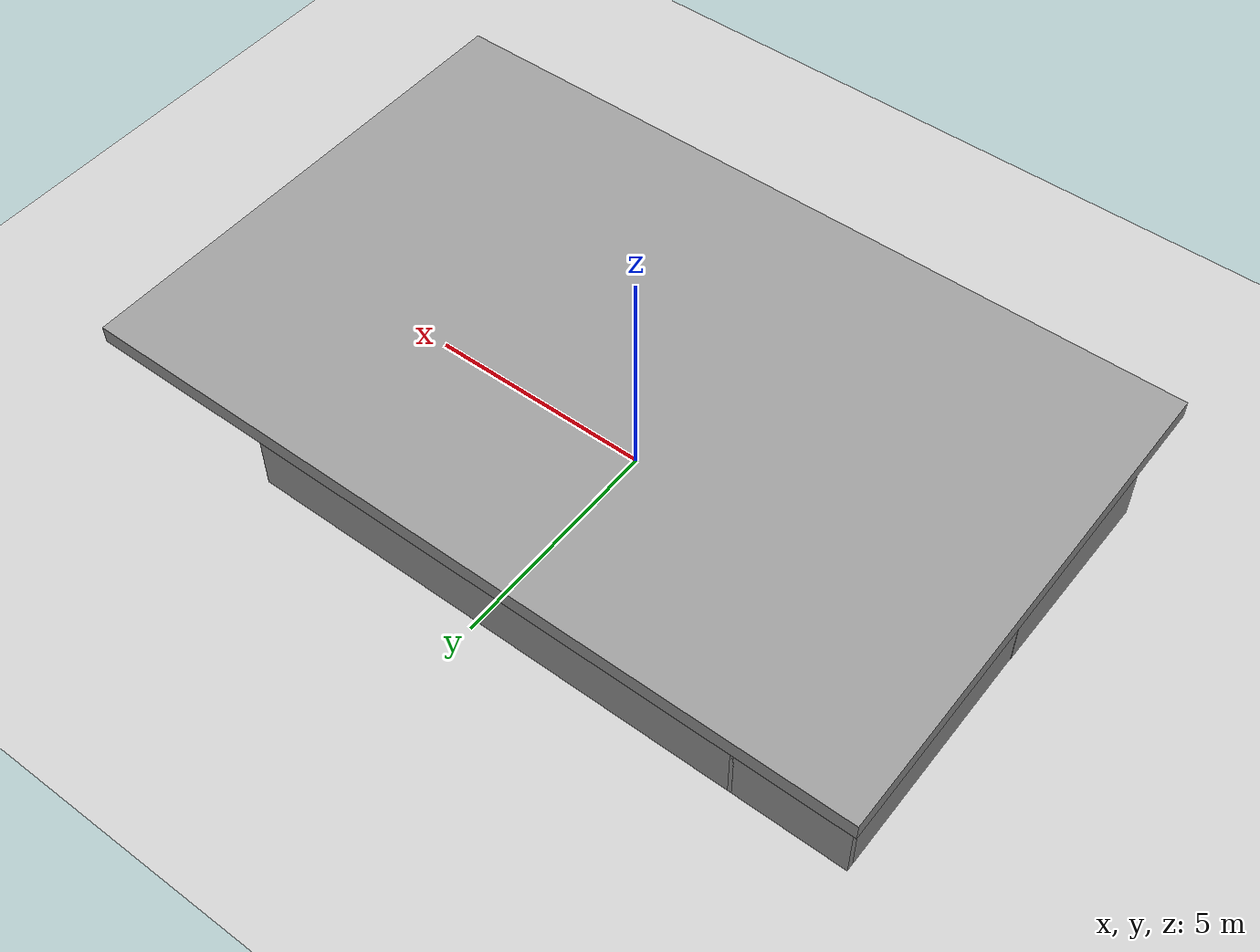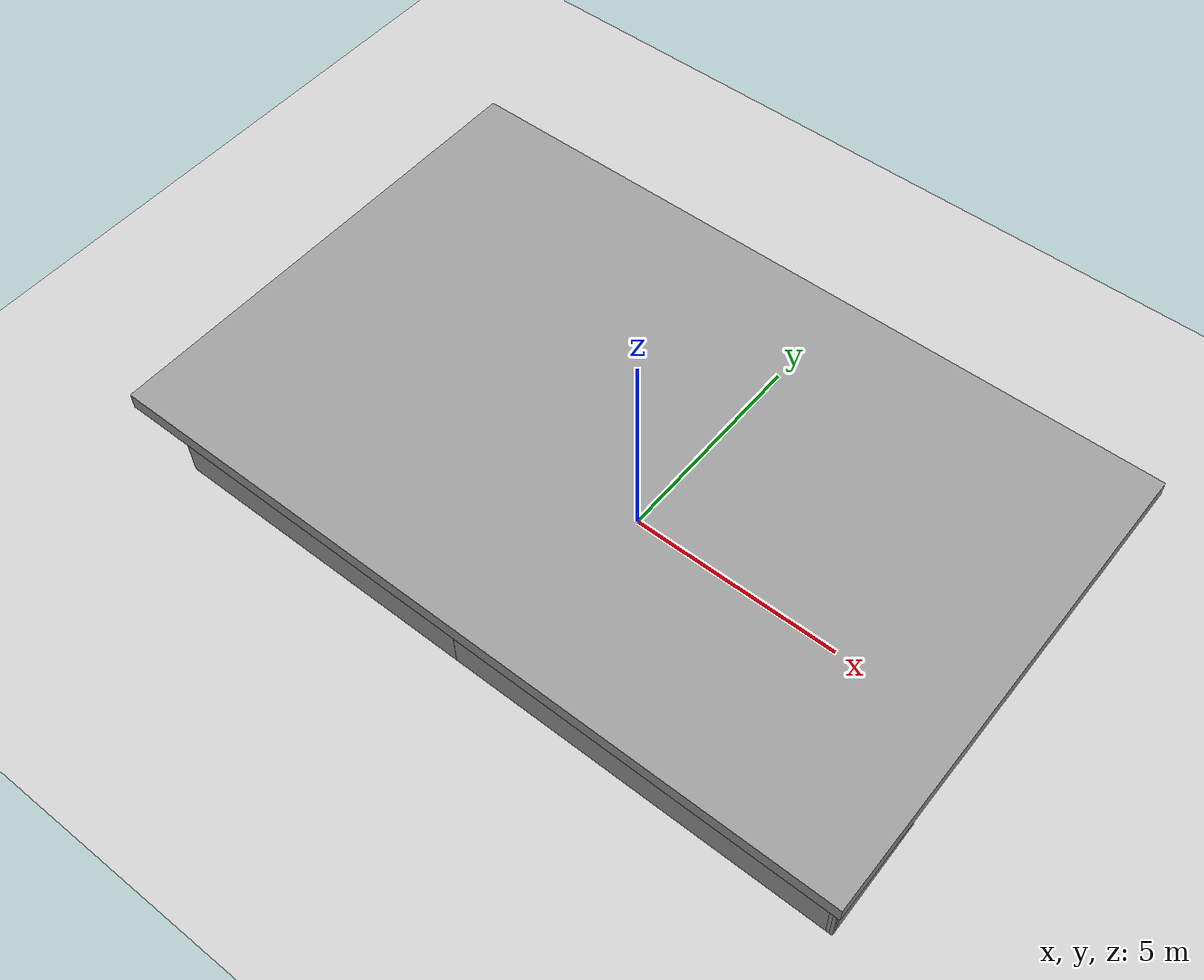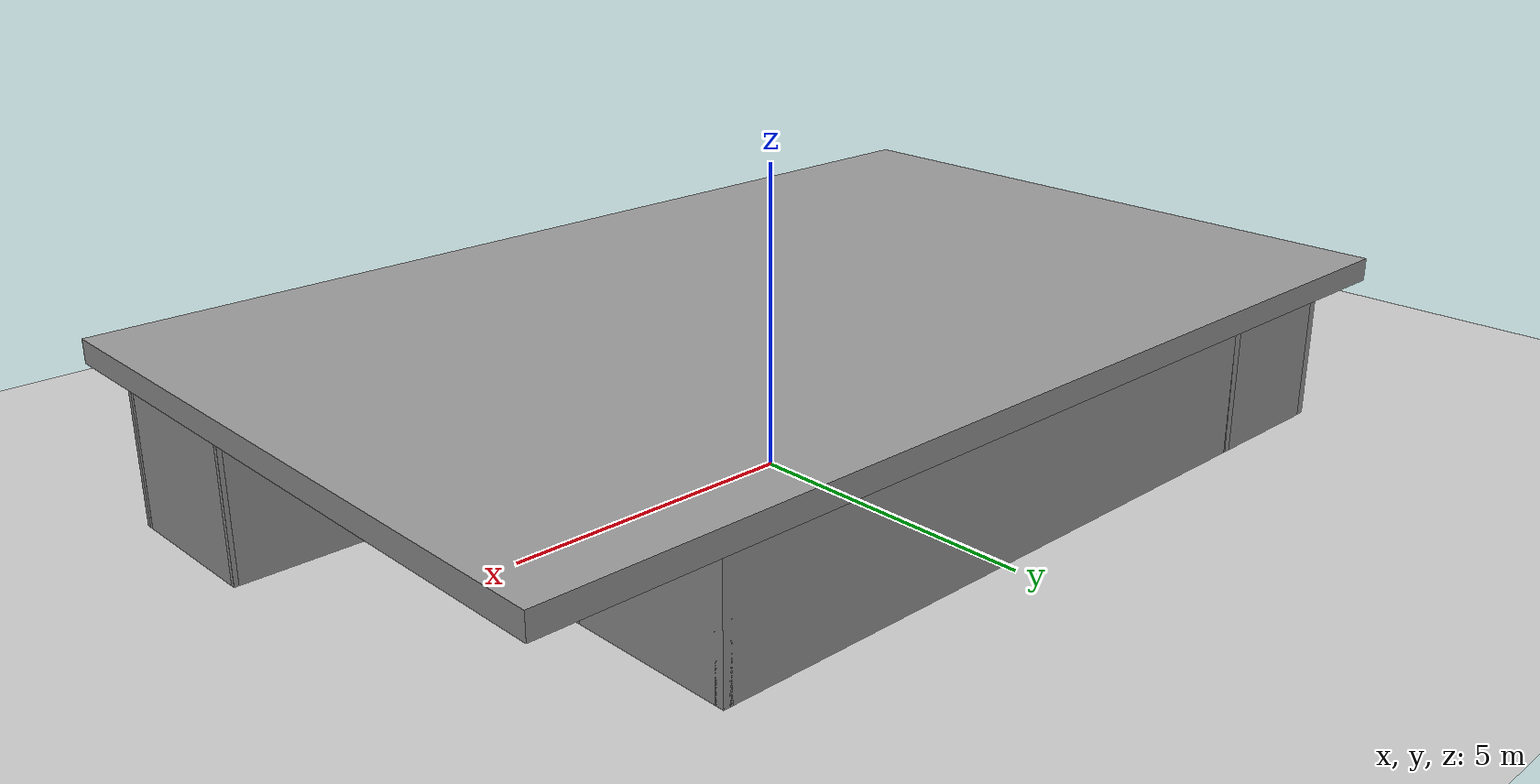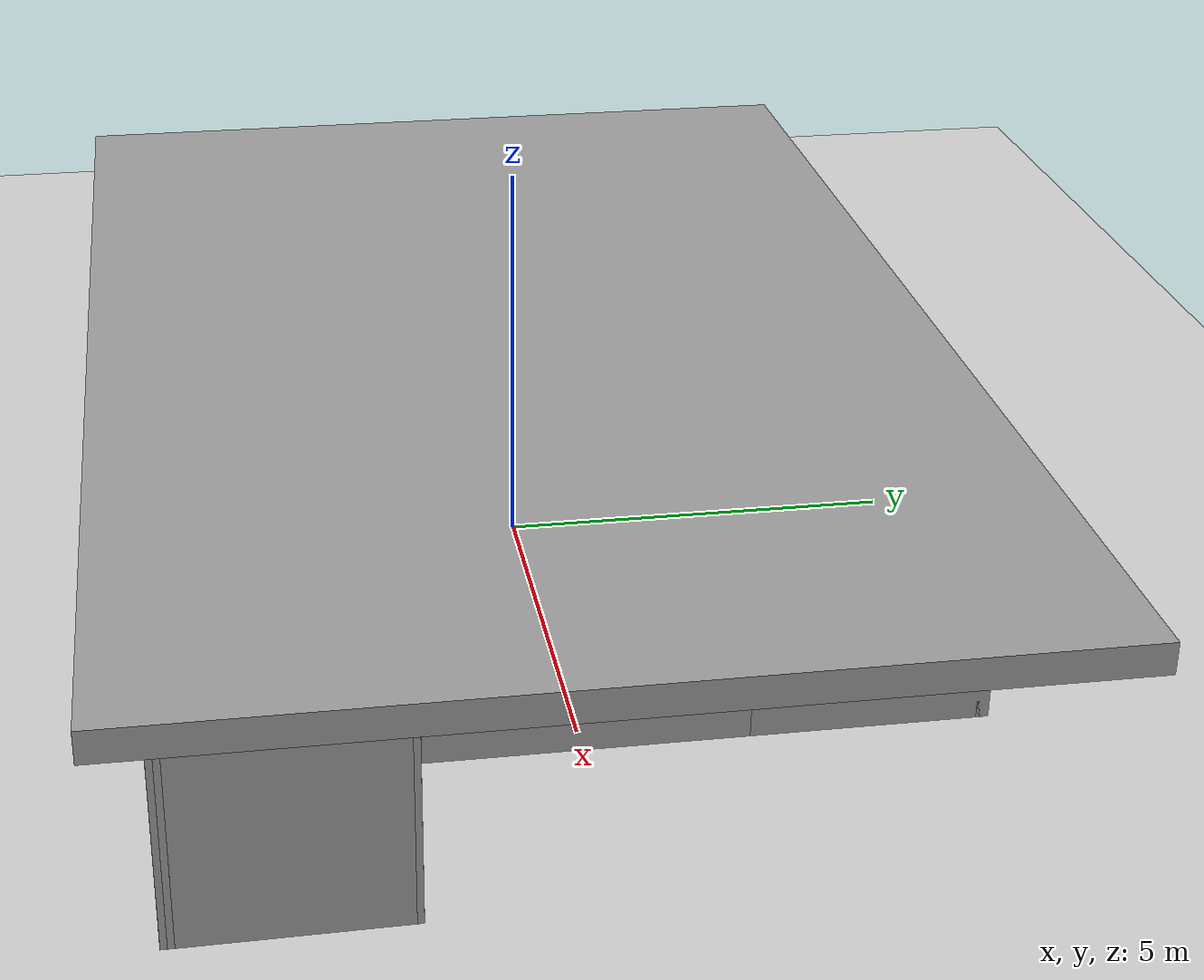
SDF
<sdf version="1.7">
 <world name="default">
  <light name="sun" type="directional">
   <pose>0 0 10 0 -0 0</pose>
   <diffuse>0.8 0.8 0.8 1</diffuse>
   <specular>0.2 0.2 0.2 1</specular>
   <attenuation>
    <range>1000</range>
    <constant>0.9</constant>
    <linear>0.01</linear>
    <quadratic>0.001</quadratic>
   </attenuation>
   <direction>-0.5 0.1 -0.9</direction>
   <spot><inner_angle>0</inner_angle><outer_angle>0</outer_angle><falloff>0</falloff></spot>
  </light>
  <model name="ground_plane">
   <static>1</static>
   <link name="link">
    <collision name="collision">
     <geometry><plane><normal>0 0 1</normal><size>100 100</size></plane></geometry>
     <surface>
      <contact><collide_bitmask>65535</collide_bitmask></contact>
      <friction><ode><mu>100</mu><mu2>50</mu2></ode></friction>
     </surface>
    </collision>
    <visual name="visual">
     <cast_shadows>0</cast_shadows>
     <geometry><plane><normal>0 0 1</normal><size>100 100</size></plane></geometry>
     <material>
      <script><uri>file://media/materials/scripts/gazebo.material</uri><name>Gazebo/Grey</name></script>
     </material>
    </visual>
   </link>
  </model>
  <gravity>0 0 -9.8</gravity>
  <magnetic_field>6e-06 2.3e-05 -4.2e-05</magnetic_field>
  <atmosphere type="adiabatic"/>
  <physics type="ode">
   <max_step_size>0.001</max_step_size>
   <real_time_factor>1</real_time_factor>
   <real_time_update_rate>1000</real_time_update_rate>
  </physics>
  <scene><ambient>0.4 0.4 0.4 1</ambient><background>0.7 0.7 0.7 1</background><shadows>1</shadows></scene>
  <spherical_coordinates>
   <surface_model>EARTH_WGS84</surface_model>
   <latitude_deg>0</latitude_deg>
   <longitude_deg>0</longitude_deg>
   <elevation>0</elevation>
   <heading_deg>0</heading_deg>
  </spherical_coordinates>
  <model name="bookshelf">
   <static>1</static>
   <link name="link">
    <inertial><mass>1</mass></inertial>
    <collision name="back">
     <pose>0 0.005 0.6 0 -0 0</pose>
     <geometry><box><size>0.9 0.01 1.2</size></box></geometry>
    </collision>
    <visual name="visual1">
     <pose>0 0.005 0.6 0 -0 0</pose>
     <geometry><box><size>0.9 0.01 1.2</size></box></geometry>
     <material>
      <script><uri>file://media/materials/scripts/gazebo.material</uri><name>Gazebo/Wood</name></script>
     </material>
    </visual>
    <collision name="left_side">
     <pose>0.45 -0.195 0.6 0 -0 0</pose>
     <geometry><box><size>0.02 0.4 1.2</size></box></geometry>
    </collision>
    <visual name="visual2">
     <pose>0.45 -0.195 0.6 0 -0 0</pose>
     <geometry><box><size>0.02 0.4 1.2</size></box></geometry>
     <material>
      <script><uri>file://media/materials/scripts/gazebo.material</uri><name>Gazebo/Wood</name></script>
     </material>
    </visual>
    <collision name="right_side">
     <pose>-0.45 -0.195 0.6 0 -0 0</pose>
     <geometry><box><size>0.02 0.4 1.2</size></box></geometry>
    </collision>
    <visual name="visual3">
     <pose>-0.45 -0.195 0.6 0 -0 0</pose>
     <geometry><box><size>0.02 0.4 1.2</size></box></geometry>
     <material>
      <script><uri>file://media/materials/scripts/gazebo.material</uri><name>Gazebo/Wood</name></script>
     </material>
    </visual>
    <collision name="bottom">
     <pose>0 -0.195 0.03 0 -0 0</pose>
     <geometry><box><size>0.88 0.4 0.06</size></box></geometry>
    </collision>
    <visual name="visual4">
     <pose>0 -0.195 0.03 0 -0 0</pose>
     <geometry><box><size>0.88 0.4 0.06</size></box></geometry>
     <material>
      <script><uri>file://media/materials/scripts/gazebo.material</uri><name>Gazebo/Wood</name></script>
     </material>
    </visual>
    <collision name="top">
     <pose>0 -0.195 1.19 0 -0 0</pose>
     <geometry><box><size>0.88 0.4 0.02</size></box></geometry>
    </collision>
    <visual name="visual5">
     <pose>0 -0.195 1.19 0 -0 0</pose>
     <geometry><box><size>0.88 0.4 0.02</size></box></geometry>
     <material>
      <script><uri>file://media/materials/scripts/gazebo.material</uri><name>Gazebo/Wood</name></script>
     </material>
    </visual>
    <collision name="low_shelf">
     <pose>0 -0.195 0.43 0 -0 0</pose>
     <geometry><box><size>0.88 0.4 0.02</size></box></geometry>
    </collision>
    <visual name="visual6">
     <pose>0 -0.195 0.43 0 -0 0</pose>
     <geometry><box><size>0.88 0.4 0.02</size></box></geometry>
     <material>
      <script><uri>file://media/materials/scripts/gazebo.material</uri><name>Gazebo/Wood</name></script>
     </material>
    </visual>
    <collision name="high_shelf">
     <pose>0 -0.195 0.8 0 -0 0</pose>
     <geometry><box><size>0.88 0.4 0.02</size></box></geometry>
    </collision>
    <visual name="visual7">
     <pose>0 -0.195 0.8 0 -0 0</pose>
     <geometry><box><size>0.88 0.4 0.02</size></box></geometry>
     <material>
      <script><uri>file://media/materials/scripts/gazebo.material</uri><name>Gazebo/Wood</name></script>
     </material>
    </visual>
   </link>
   <pose>1.18489 0.921683 0 0 0 -1.5557</pose>
  </model>
  <model name="table">
   <static>1</static>
   <link name="link">
    <collision name="surface">
     <pose>0 0 1 0 -0 0</pose>
     <geometry><box><size>1.5 0.8 0.03</size></box></geometry>
     <surface><friction><ode><mu>0.6</mu><mu2>0.6</mu2></ode></friction></surface>
    </collision>
    <visual name="visual1">
     <pose>0 0 1 0 -0 0</pose>
     <geometry><box><size>1.5 0.8 0.03</size></box></geometry>
     <material>
      <script><uri>file://media/materials/scripts/gazebo.material</uri><name>Gazebo/Wood</name></script>
     </material>
    </visual>
    <collision name="front_left_leg">
     <pose>0.68 0.38 0.5 0 -0 0</pose>
     <geometry><cylinder><radius>0.02</radius><length>1</length></cylinder></geometry>
    </collision>
    <visual name="front_left_leg">
     <pose>0.68 0.38 0.5 0 -0 0</pose>
     <geometry><cylinder><radius>0.02</radius><length>1</length></cylinder></geometry>
     <material>
      <script><uri>file://media/materials/scripts/gazebo.material</uri><name>Gazebo/Grey</name></script>
     </material>
    </visual>
    <collision name="front_right_leg">
     <pose>0.68 -0.38 0.5 0 -0 0</pose>
     <geometry><cylinder><radius>0.02</radius><length>1</length></cylinder></geometry>
    </collision>
    <visual name="front_right_leg">
     <pose>0.68 -0.38 0.5 0 -0 0</pose>
     <geometry><cylinder><radius>0.02</radius><length>1</length></cylinder></geometry>
     <material>
      <script><uri>file://media/materials/scripts/gazebo.material</uri><name>Gazebo/Grey</name></script>
     </material>
    </visual>
    <collision name="back_right_leg">
     <pose>-0.68 -0.38 0.5 0 -0 0</pose>
     <geometry><cylinder><radius>0.02</radius><length>1</length></cylinder></geometry>
    </collision>
    <visual name="back_right_leg">
     <pose>-0.68 -0.38 0.5 0 -0 0</pose>
     <geometry><cylinder><radius>0.02</radius><length>1</length></cylinder></geometry>
     <material>
      <script><uri>file://media/materials/scripts/gazebo.material</uri><name>Gazebo/Grey</name></script>
     </material>
    </visual>
    <collision name="back_left_leg">
     <pose>-0.68 0.38 0.5 0 -0 0</pose>
     <geometry><cylinder><radius>0.02</radius><length>1</length></cylinder></geometry>
    </collision>
    <visual name="back_left_leg">
     <pose>-0.68 0.38 0.5 0 -0 0</pose>
     <geometry><cylinder><radius>0.02</radius><length>1</length></cylinder></geometry>
     <material>
      <script><uri>file://media/materials/scripts/gazebo.material</uri><name>Gazebo/Grey</name></script>
     </material>
    </visual>
   </link>
   <pose>-5.89533 -4.13682 0 0 -0 0</pose>
  </model>
  <model name="simple_chair">
   <link name="link_0_clone">
    <inertial>
     <mass>1</mass>
     <inertia>
      <ixx>0.166667</ixx>
      <ixy>0</ixy>
      <ixz>0</ixz>
      <iyy>0.166667</iyy>
      <iyz>0</iyz>
      <izz>0.166667</izz>
     </inertia>
    </inertial>
    <pose>-0.041667 -0 0.165833 0 -0 0</pose>
    <visual name="visual">
     <geometry><box><size>0.6 0.6 0.11</size></box></geometry>
     <material>
      <lighting>1</lighting>
      <script><uri>file://media/materials/scripts/gazebo.material</uri><name>Gazebo/Grey</name></script>
      <shader type="pixel"><normal_map>__default__</normal_map></shader>
      <ambient>0.3 0.3 0.3 1</ambient>
      <diffuse>0.7 0.7 0.7 1</diffuse>
      <specular>0.01 0.01 0.01 1</specular>
      <emissive>0 0 0 1</emissive>
     </material>
    </visual>
    <collision name="collision">
     <geometry><box><size>0.6 0.6 0.1</size></box></geometry>
     <surface>
      <friction>
       <ode><mu>1</mu><mu2>1</mu2><fdir1>0 0 0</fdir1><slip1>0</slip1><slip2>0</slip2></ode>
       <torsional>
        <coefficient>1</coefficient>
        <patch_radius>0</patch_radius>
        <surface_radius>0</surface_radius>
        <use_patch_radius>1</use_patch_radius>
        <ode><slip>0</slip></ode>
       </torsional>
      </friction>
      <bounce><restitution_coefficient>0</restitution_coefficient><threshold>1e+06</threshold></bounce>
      <contact>
       <collide_without_contact>0</collide_without_contact>
       <collide_without_contact_bitmask>1</collide_without_contact_bitmask>
       <collide_bitmask>1</collide_bitmask>
       <ode>
        <soft_cfm>0</soft_cfm>
        <soft_erp>0.2</soft_erp>
        <kp>1e+13</kp>
        <kd>1</kd>
        <max_vel>0.01</max_vel>
        <min_depth>0</min_depth>
       </ode>
       <bullet>
        <split_impulse>1</split_impulse>
        <split_impulse_penetration_threshold>-0.01</split_impulse_penetration_threshold>
        <soft_cfm>0</soft_cfm>
        <soft_erp>0.2</soft_erp>
        <kp>1e+13</kp>
        <kd>1</kd>
       </bullet>
      </contact>
     </surface>
    </collision>
   </link>
   <link name="link_1_clone">
    <inertial>
     <mass>1</mass>
     <inertia>
      <ixx>0.166667</ixx>
      <ixy>0</ixy>
      <ixz>0</ixz>
      <iyy>0.166667</iyy>
      <iyz>0</iyz>
      <izz>0.166667</izz>
     </inertia>
    </inertial>
    <pose>-0.291667 0.25 -0.184167 0 -0 0</pose>
    <visual name="visual">
     <geometry><box><size>0.1 0.1 0.6</size></box></geometry>
     <material>
      <lighting>1</lighting>
      <script><uri>file://media/materials/scripts/gazebo.material</uri><name>Gazebo/Grey</name></script>
      <shader type="pixel"><normal_map>__default__</normal_map></shader>
      <ambient>0.3 0.3 0.3 1</ambient>
      <diffuse>0.7 0.7 0.7 1</diffuse>
      <specular>0.01 0.01 0.01 1</specular>
      <emissive>0 0 0 1</emissive>
     </material>
    </visual>
    <collision name="collision">
     <geometry><box><size>0.1 0.1 0.6</size></box></geometry>
     <surface>
      <friction>
       <ode><mu>1</mu><mu2>1</mu2><fdir1>0 0 0</fdir1><slip1>0</slip1><slip2>0</slip2></ode>
       <torsional>
        <coefficient>1</coefficient>
        <patch_radius>0</patch_radius>
        <surface_radius>0</surface_radius>
        <use_patch_radius>1</use_patch_radius>
        <ode><slip>0</slip></ode>
       </torsional>
      </friction>
      <bounce><restitution_coefficient>0</restitution_coefficient><threshold>1e+06</threshold></bounce>
      <contact>
       <collide_without_contact>0</collide_without_contact>
       <collide_without_contact_bitmask>1</collide_without_contact_bitmask>
       <collide_bitmask>1</collide_bitmask>
       <ode>
        <soft_cfm>0</soft_cfm>
        <soft_erp>0.2</soft_erp>
        <kp>1e+13</kp>
        <kd>1</kd>
        <max_vel>0.01</max_vel>
        <min_depth>0</min_depth>
       </ode>
       <bullet>
        <split_impulse>1</split_impulse>
        <split_impulse_penetration_threshold>-0.01</split_impulse_penetration_threshold>
        <soft_cfm>0</soft_cfm>
        <soft_erp>0.2</soft_erp>
        <kp>1e+13</kp>
        <kd>1</kd>
       </bullet>
      </contact>
     </surface>
    </collision>
   </link>
   <link name="link_1_clone_0">
    <inertial>
     <mass>1</mass>
     <inertia>
      <ixx>0.166667</ixx>
      <ixy>0</ixy>
      <ixz>0</ixz>
      <iyy>0.166667</iyy>
      <iyz>0</iyz>
      <izz>0.166667</izz>
     </inertia>
    </inertial>
    <pose>0.208333 0.25 -0.184167 0 -0 0</pose>
    <visual name="visual">
     <geometry><box><size>0.1 0.1 0.6</size></box></geometry>
     <material>
      <lighting>1</lighting>
      <script><uri>file://media/materials/scripts/gazebo.material</uri><name>Gazebo/Grey</name></script>
      <shader type="pixel"><normal_map>__default__</normal_map></shader>
      <ambient>0.3 0.3 0.3 1</ambient>
      <diffuse>0.7 0.7 0.7 1</diffuse>
      <specular>0.01 0.01 0.01 1</specular>
      <emissive>0 0 0 1</emissive>
     </material>
    </visual>
    <collision name="collision">
     <geometry><box><size>0.1 0.1 0.6</size></box></geometry>
     <surface>
      <friction>
       <ode><mu>1</mu><mu2>1</mu2><fdir1>0 0 0</fdir1><slip1>0</slip1><slip2>0</slip2></ode>
       <torsional>
        <coefficient>1</coefficient>
        <patch_radius>0</patch_radius>
        <surface_radius>0</surface_radius>
        <use_patch_radius>1</use_patch_radius>
        <ode><slip>0</slip></ode>
       </torsional>
      </friction>
      <bounce><restitution_coefficient>0</restitution_coefficient><threshold>1e+06</threshold></bounce>
      <contact>
       <collide_without_contact>0</collide_without_contact>
       <collide_without_contact_bitmask>1</collide_without_contact_bitmask>
       <collide_bitmask>1</collide_bitmask>
       <ode>
        <soft_cfm>0</soft_cfm>
        <soft_erp>0.2</soft_erp>
        <kp>1e+13</kp>
        <kd>1</kd>
        <max_vel>0.01</max_vel>
        <min_depth>0</min_depth>
       </ode>
       <bullet>
        <split_impulse>1</split_impulse>
        <split_impulse_penetration_threshold>-0.01</split_impulse_penetration_threshold>
        <soft_cfm>0</soft_cfm>
        <soft_erp>0.2</soft_erp>
        <kp>1e+13</kp>
        <kd>1</kd>
       </bullet>
      </contact>
     </surface>
    </collision>
   </link>
   <link name="link_1_clone_1">
    <inertial>
     <mass>1</mass>
     <inertia>
      <ixx>0.166667</ixx>
      <ixy>0</ixy>
      <ixz>0</ixz>
      <iyy>0.166667</iyy>
      <iyz>0</iyz>
      <izz>0.166667</izz>
     </inertia>
    </inertial>
    <pose>0.208333 -0.25 -0.184167 0 -0 0</pose>
    <visual name="visual">
     <geometry><box><size>0.1 0.1 0.6</size></box></geometry>
     <material>
      <lighting>1</lighting>
      <script><uri>file://media/materials/scripts/gazebo.material</uri><name>Gazebo/Grey</name></script>
      <shader type="pixel"><normal_map>__default__</normal_map></shader>
      <ambient>0.3 0.3 0.3 1</ambient>
      <diffuse>0.7 0.7 0.7 1</diffuse>
      <specular>0.01 0.01 0.01 1</specular>
      <emissive>0 0 0 1</emissive>
     </material>
    </visual>
    <collision name="collision">
     <geometry><box><size>0.1 0.1 0.6</size></box></geometry>
     <surface>
      <friction>
       <ode><mu>1</mu><mu2>1</mu2><fdir1>0 0 0</fdir1><slip1>0</slip1><slip2>0</slip2></ode>
       <torsional>
        <coefficient>1</coefficient>
        <patch_radius>0</patch_radius>
        <surface_radius>0</surface_radius>
        <use_patch_radius>1</use_patch_radius>
        <ode><slip>0</slip></ode>
       </torsional>
      </friction>
      <bounce><restitution_coefficient>0</restitution_coefficient><threshold>1e+06</threshold></bounce>
      <contact>
       <collide_without_contact>0</collide_without_contact>
       <collide_without_contact_bitmask>1</collide_without_contact_bitmask>
       <collide_bitmask>1</collide_bitmask>
       <ode>
        <soft_cfm>0</soft_cfm>
        <soft_erp>0.2</soft_erp>
        <kp>1e+13</kp>
        <kd>1</kd>
        <max_vel>0.01</max_vel>
        <min_depth>0</min_depth>
       </ode>
       <bullet>
        <split_impulse>1</split_impulse>
        <split_impulse_penetration_threshold>-0.01</split_impulse_penetration_threshold>
        <soft_cfm>0</soft_cfm>
        <soft_erp>0.2</soft_erp>
        <kp>1e+13</kp>
        <kd>1</kd>
       </bullet>
      </contact>
     </surface>
    </collision>
   </link>
   <link name="link_1_clone_clone">
    <inertial>
     <mass>1</mass>
     <inertia>
      <ixx>0.166667</ixx>
      <ixy>0</ixy>
      <ixz>0</ixz>
      <iyy>0.166667</iyy>
      <iyz>0</iyz>
      <izz>0.166667</izz>
     </inertia>
    </inertial>
    <pose>-0.291667 -0.25 -0.184167 0 -0 0</pose>
    <visual name="visual">
     <geometry><box><size>0.1 0.1 0.6</size></box></geometry>
     <material>
      <lighting>1</lighting>
      <script><uri>file://media/materials/scripts/gazebo.material</uri><name>Gazebo/Grey</name></script>
      <shader type="pixel"><normal_map>__default__</normal_map></shader>
      <ambient>0.3 0.3 0.3 1</ambient>
      <diffuse>0.7 0.7 0.7 1</diffuse>
      <specular>0.01 0.01 0.01 1</specular>
      <emissive>0 0 0 1</emissive>
     </material>
    </visual>
    <collision name="collision">
     <geometry><box><size>0.1 0.1 0.6</size></box></geometry>
     <surface>
      <friction>
       <ode><mu>1</mu><mu2>1</mu2><fdir1>0 0 0</fdir1><slip1>0</slip1><slip2>0</slip2></ode>
       <torsional>
        <coefficient>1</coefficient>
        <patch_radius>0</patch_radius>
        <surface_radius>0</surface_radius>
        <use_patch_radius>1</use_patch_radius>
        <ode><slip>0</slip></ode>
       </torsional>
      </friction>
      <bounce><restitution_coefficient>0</restitution_coefficient><threshold>1e+06</threshold></bounce>
      <contact>
       <collide_without_contact>0</collide_without_contact>
       <collide_without_contact_bitmask>1</collide_without_contact_bitmask>
       <collide_bitmask>1</collide_bitmask>
       <ode>
        <soft_cfm>0</soft_cfm>
        <soft_erp>0.2</soft_erp>
        <kp>1e+13</kp>
        <kd>1</kd>
        <max_vel>0.01</max_vel>
        <min_depth>0</min_depth>
       </ode>
       <bullet>
        <split_impulse>1</split_impulse>
        <split_impulse_penetration_threshold>-0.01</split_impulse_penetration_threshold>
        <soft_cfm>0</soft_cfm>
        <soft_erp>0.2</soft_erp>
        <kp>1e+13</kp>
        <kd>1</kd>
       </bullet>
      </contact>
     </surface>
    </collision>
   </link>
   <link name="link_2_clone">
    <inertial>
     <mass>1</mass>
     <inertia>
      <ixx>0.166667</ixx>
      <ixy>0</ixy>
      <ixz>0</ixz>
      <iyy>0.166667</iyy>
      <iyz>0</iyz>
      <izz>0.166667</izz>
     </inertia>
    </inertial>
    <pose>0.208333 -0 0.570833 0 -0 0</pose>
    <visual name="visual">
     <geometry><box><size>0.1 0.6 0.7</size></box></geometry>
     <material>
      <lighting>1</lighting>
      <script><uri>file://media/materials/scripts/gazebo.material</uri><name>Gazebo/Grey</name></script>
      <shader type="pixel"><normal_map>__default__</normal_map></shader>
      <ambient>0.3 0.3 0.3 1</ambient>
      <diffuse>0.7 0.7 0.7 1</diffuse>
      <specular>0.01 0.01 0.01 1</specular>
      <emissive>0 0 0 1</emissive>
     </material>
    </visual>
    <collision name="collision">
     <geometry><box><size>0.1 0.6 0.7</size></box></geometry>
     <surface>
      <friction>
       <ode><mu>1</mu><mu2>1</mu2><fdir1>0 0 0</fdir1><slip1>0</slip1><slip2>0</slip2></ode>
       <torsional>
        <coefficient>1</coefficient>
        <patch_radius>0</patch_radius>
        <surface_radius>0</surface_radius>
        <use_patch_radius>1</use_patch_radius>
        <ode><slip>0</slip></ode>
       </torsional>
      </friction>
      <bounce><restitution_coefficient>0</restitution_coefficient><threshold>1e+06</threshold></bounce>
      <contact>
       <collide_without_contact>0</collide_without_contact>
       <collide_without_contact_bitmask>1</collide_without_contact_bitmask>
       <collide_bitmask>1</collide_bitmask>
       <ode>
        <soft_cfm>0</soft_cfm>
        <soft_erp>0.2</soft_erp>
        <kp>1e+13</kp>
        <kd>1</kd>
        <max_vel>0.01</max_vel>
        <min_depth>0</min_depth>
       </ode>
       <bullet>
        <split_impulse>1</split_impulse>
        <split_impulse_penetration_threshold>-0.01</split_impulse_penetration_threshold>
        <soft_cfm>0</soft_cfm>
        <soft_erp>0.2</soft_erp>
        <kp>1e+13</kp>
        <kd>1</kd>
       </bullet>
      </contact>
     </surface>
    </collision>
   </link>
   <joint name="link_0_clone_JOINT_0" type="fixed">
    <parent>link_0_clone</parent>
    <child>link_1_clone_clone</child>
    <physics>
     <ode><limit><cfm>0</cfm><erp>0.2</erp></limit><suspension><cfm>0</cfm><erp>0.2</erp></suspension></ode>
    </physics>
   </joint>
   <joint name="link_0_clone_JOINT_1" type="fixed">
    <parent>link_0_clone</parent>
    <child>link_1_clone</child>
    <physics>
     <ode><limit><cfm>0</cfm><erp>0.2</erp></limit><suspension><cfm>0</cfm><erp>0.2</erp></suspension></ode>
    </physics>
   </joint>
   <joint name="link_0_clone_JOINT_2" type="fixed">
    <parent>link_0_clone</parent>
    <child>link_1_clone_1</child>
    <physics>
     <ode><limit><cfm>0</cfm><erp>0.2</erp></limit><suspension><cfm>0</cfm><erp>0.2</erp></suspension></ode>
    </physics>
   </joint>
   <joint name="link_0_clone_JOINT_3" type="fixed">
    <parent>link_0_clone</parent>
    <child>link_2_clone</child>
    <physics>
     <ode><limit><cfm>0</cfm><erp>0.2</erp></limit><suspension><cfm>0</cfm><erp>0.2</erp></suspension></ode>
    </physics>
   </joint>
   <joint name="link_0_clone_JOINT_4" type="fixed">
    <parent>link_0_clone</parent>
    <child>link_1_clone_0</child>
    <physics>
     <ode><limit><cfm>0</cfm><erp>0.2</erp></limit><suspension><cfm>0</cfm><erp>0.2</erp></suspension></ode>
    </physics>
   </joint>
   <static>0</static>
   <pose>-5.9136 -3.13727 0.484167 0 -0 1.55057</pose>
  </model>
  <model name="cabinet">
   <static>1</static>
   <link name="cabinet_bottom_plate">
    <inertial>
     <pose>0 0 -1 0 -0 0</pose>
     <inertia><ixx>2.05</ixx><ixy>0</ixy><ixz>0</ixz><iyy>2.05</iyy><iyz>0</iyz><izz>2.05</izz></inertia>
     <mass>25</mass>
    </inertial>
    <collision name="cabinet_bottom_plate_geom">
     <pose>0 0 0.01 0 -0 0</pose>
     <geometry><box><size>0.45 0.45 0.02</size></box></geometry>
    </collision>
    <visual name="cabinet_bottom_plate_geom_visual">
     <pose>0 0 0.01 0 -0 0</pose>
     <geometry><box><size>0.45 0.45 0.02</size></box></geometry>
     <material>
      <script><uri>file://media/materials/scripts/gazebo.material</uri><name>Gazebo/Wood</name></script>
     </material>
    </visual>
    <collision name="cabinet_bottom_plate_geom_cabinet_back_plate">
     <pose>0.235 0 0.51 0 -0 0</pose>
     <geometry><box><size>0.02 0.45 1.02</size></box></geometry>
    </collision>
    <visual name="cabinet_bottom_plate_geom_cabinet_back_plate_visual">
     <pose>0.235 0 0.51 0 -0 0</pose>
     <geometry><box><size>0.02 0.45 1.02</size></box></geometry>
     <material>
      <script><uri>file://media/materials/scripts/gazebo.material</uri><name>Gazebo/Wood</name></script>
     </material>
    </visual>
    <collision name="cabinet_bottom_plate_geom_cabinet_left_plate">
     <pose>0 0.235 0.51 0 -0 0</pose>
     <geometry><box><size>0.45 0.02 1.02</size></box></geometry>
    </collision>
    <visual name="cabinet_bottom_plate_geom_cabinet_left_plate_visual">
     <pose>0 0.235 0.51 0 -0 0</pose>
     <geometry><box><size>0.45 0.02 1.02</size></box></geometry>
     <material>
      <script><uri>file://media/materials/scripts/gazebo.material</uri><name>Gazebo/Wood</name></script>
     </material>
    </visual>
    <collision name="cabinet_bottom_plate_geom_cabinet_middle_plate">
     <pose>0 0 0.51 0 -0 0</pose>
     <geometry><box><size>0.45 0.45 0.02</size></box></geometry>
    </collision>
    <visual name="cabinet_bottom_plate_geom_cabinet_middle_plate_visual">
     <pose>0 0 0.51 0 -0 0</pose>
     <geometry><box><size>0.45 0.45 0.02</size></box></geometry>
     <material>
      <script><uri>file://media/materials/scripts/gazebo.material</uri><name>Gazebo/Wood</name></script>
     </material>
    </visual>
    <collision name="cabinet_bottom_plate_geom_cabinet_right_plate">
     <pose>0 -0.235 0.51 0 -0 0</pose>
     <geometry><box><size>0.45 0.02 1.02</size></box></geometry>
    </collision>
    <visual name="cabinet_bottom_plate_geom_cabinet_right_plate_visual">
     <pose>0 -0.235 0.51 0 -0 0</pose>
     <geometry><box><size>0.45 0.02 1.02</size></box></geometry>
     <material>
      <script><uri>file://media/materials/scripts/gazebo.material</uri><name>Gazebo/Wood</name></script>
     </material>
    </visual>
    <collision name="cabinet_bottom_plate_geom_cabinet_top_plate">
     <pose>0 0 1.01 0 -0 0</pose>
     <geometry><box><size>0.45 0.45 0.02</size></box></geometry>
    </collision>
    <visual name="cabinet_bottom_plate_geom_cabinet_top_plate_visual">
     <pose>0 0 1.01 0 -0 0</pose>
     <geometry><box><size>0.45 0.45 0.02</size></box></geometry>
     <material>
      <script><uri>file://media/materials/scripts/gazebo.material</uri><name>Gazebo/Wood</name></script>
     </material>
    </visual>
   </link>
   <pose>-4.80458 -4.31362 0 0 -0 0</pose>
  </model>
  <model name="bookshelf_0">
   <static>1</static>
   <link name="link">
    <inertial><mass>1</mass></inertial>
    <collision name="back">
     <pose>0 0.005 0.6 0 -0 0</pose>
     <geometry><box><size>0.9 0.01 1.2</size></box></geometry>
    </collision>
    <visual name="visual1">
     <pose>0 0.005 0.6 0 -0 0</pose>
     <geometry><box><size>0.9 0.01 1.2</size></box></geometry>
     <material>
      <script><uri>file://media/materials/scripts/gazebo.material</uri><name>Gazebo/Wood</name></script>
     </material>
    </visual>
    <collision name="left_side">
     <pose>0.45 -0.195 0.6 0 -0 0</pose>
     <geometry><box><size>0.02 0.4 1.2</size></box></geometry>
    </collision>
    <visual name="visual2">
     <pose>0.45 -0.195 0.6 0 -0 0</pose>
     <geometry><box><size>0.02 0.4 1.2</size></box></geometry>
     <material>
      <script><uri>file://media/materials/scripts/gazebo.material</uri><name>Gazebo/Wood</name></script>
     </material>
    </visual>
    <collision name="right_side">
     <pose>-0.45 -0.195 0.6 0 -0 0</pose>
     <geometry><box><size>0.02 0.4 1.2</size></box></geometry>
    </collision>
    <visual name="visual3">
     <pose>-0.45 -0.195 0.6 0 -0 0</pose>
     <geometry><box><size>0.02 0.4 1.2</size></box></geometry>
     <material>
      <script><uri>file://media/materials/scripts/gazebo.material</uri><name>Gazebo/Wood</name></script>
     </material>
    </visual>
    <collision name="bottom">
     <pose>0 -0.195 0.03 0 -0 0</pose>
     <geometry><box><size>0.88 0.4 0.06</size></box></geometry>
    </collision>
    <visual name="visual4">
     <pose>0 -0.195 0.03 0 -0 0</pose>
     <geometry><box><size>0.88 0.4 0.06</size></box></geometry>
     <material>
      <script><uri>file://media/materials/scripts/gazebo.material</uri><name>Gazebo/Wood</name></script>
     </material>
    </visual>
    <collision name="top">
     <pose>0 -0.195 1.19 0 -0 0</pose>
     <geometry><box><size>0.88 0.4 0.02</size></box></geometry>
    </collision>
    <visual name="visual5">
     <pose>0 -0.195 1.19 0 -0 0</pose>
     <geometry><box><size>0.88 0.4 0.02</size></box></geometry>
     <material>
      <script><uri>file://media/materials/scripts/gazebo.material</uri><name>Gazebo/Wood</name></script>
     </material>
    </visual>
    <collision name="low_shelf">
     <pose>0 -0.195 0.43 0 -0 0</pose>
     <geometry><box><size>0.88 0.4 0.02</size></box></geometry>
    </collision>
    <visual name="visual6">
     <pose>0 -0.195 0.43 0 -0 0</pose>
     <geometry><box><size>0.88 0.4 0.02</size></box></geometry>
     <material>
      <script><uri>file://media/materials/scripts/gazebo.material</uri><name>Gazebo/Wood</name></script>
     </material>
    </visual>
    <collision name="high_shelf">
     <pose>0 -0.195 0.8 0 -0 0</pose>
     <geometry><box><size>0.88 0.4 0.02</size></box></geometry>
    </collision>
    <visual name="visual7">
     <pose>0 -0.195 0.8 0 -0 0</pose>
     <geometry><box><size>0.88 0.4 0.02</size></box></geometry>
     <material>
      <script><uri>file://media/materials/scripts/gazebo.material</uri><name>Gazebo/Wood</name></script>
     </material>
    </visual>
   </link>
   <pose>-7.9834 -1.30385 0 0 -0 1.55988</pose>
  </model>
  <model name="bookshelf_0_clone">
   <static>1</static>
   <link name="link">
    <inertial><mass>1</mass></inertial>
    <collision name="back">
     <pose>0 0.005 0.6 0 -0 0</pose>
     <geometry><box><size>0.9 0.01 1.2</size></box></geometry>
    </collision>
    <visual name="visual1">
     <pose>0 0.005 0.6 0 -0 0</pose>
     <geometry><box><size>0.9 0.01 1.2</size></box></geometry>
     <material>
      <script><uri>file://media/materials/scripts/gazebo.material</uri><name>Gazebo/Wood</name></script>
     </material>
    </visual>
    <collision name="left_side">
     <pose>0.45 -0.195 0.6 0 -0 0</pose>
     <geometry><box><size>0.02 0.4 1.2</size></box></geometry>
    </collision>
    <visual name="visual2">
     <pose>0.45 -0.195 0.6 0 -0 0</pose>
     <geometry><box><size>0.02 0.4 1.2</size></box></geometry>
     <material>
      <script><uri>file://media/materials/scripts/gazebo.material</uri><name>Gazebo/Wood</name></script>
     </material>
    </visual>
    <collision name="right_side">
     <pose>-0.45 -0.195 0.6 0 -0 0</pose>
     <geometry><box><size>0.02 0.4 1.2</size></box></geometry>
    </collision>
    <visual name="visual3">
     <pose>-0.45 -0.195 0.6 0 -0 0</pose>
     <geometry><box><size>0.02 0.4 1.2</size></box></geometry>
     <material>
      <script><uri>file://media/materials/scripts/gazebo.material</uri><name>Gazebo/Wood</name></script>
     </material>
    </visual>
    <collision name="bottom">
     <pose>0 -0.195 0.03 0 -0 0</pose>
     <geometry><box><size>0.88 0.4 0.06</size></box></geometry>
    </collision>
    <visual name="visual4">
     <pose>0 -0.195 0.03 0 -0 0</pose>
     <geometry><box><size>0.88 0.4 0.06</size></box></geometry>
     <material>
      <script><uri>file://media/materials/scripts/gazebo.material</uri><name>Gazebo/Wood</name></script>
     </material>
    </visual>
    <collision name="top">
     <pose>0 -0.195 1.19 0 -0 0</pose>
     <geometry><box><size>0.88 0.4 0.02</size></box></geometry>
    </collision>
    <visual name="visual5">
     <pose>0 -0.195 1.19 0 -0 0</pose>
     <geometry><box><size>0.88 0.4 0.02</size></box></geometry>
     <material>
      <script><uri>file://media/materials/scripts/gazebo.material</uri><name>Gazebo/Wood</name></script>
     </material>
    </visual>
    <collision name="low_shelf">
     <pose>0 -0.195 0.43 0 -0 0</pose>
     <geometry><box><size>0.88 0.4 0.02</size></box></geometry>
    </collision>
    <visual name="visual6">
     <pose>0 -0.195 0.43 0 -0 0</pose>
     <geometry><box><size>0.88 0.4 0.02</size></box></geometry>
     <material>
      <script><uri>file://media/materials/scripts/gazebo.material</uri><name>Gazebo/Wood</name></script>
     </material>
    </visual>
    <collision name="high_shelf">
     <pose>0 -0.195 0.8 0 -0 0</pose>
     <geometry><box><size>0.88 0.4 0.02</size></box></geometry>
    </collision>
    <visual name="visual7">
     <pose>0 -0.195 0.8 0 -0 0</pose>
     <geometry><box><size>0.88 0.4 0.02</size></box></geometry>
     <material>
      <script><uri>file://media/materials/scripts/gazebo.material</uri><name>Gazebo/Wood</name></script>
     </material>
    </visual>
   </link>
   <pose>0.760692 -3.82832 0 0 -0 1.55988</pose>
  </model>
  <model name="demo_clean">
   <link name="Wall_0">
    <pose>-8.14649 2.06618 0 0 0 -1.5708</pose>
    <visual name="Wall_0_Visual">
     <pose>0 0 1.25 0 -0 0</pose>
     <geometry><box><size>5.5 0.15 2.5</size></box></geometry>
     <material>
      <script><uri>file://media/materials/scripts/gazebo.material</uri><name>Gazebo/Grey</name></script>
      <ambient>1 1 1 1</ambient>
      <shader type="pixel"/>
     </material>
     <meta><layer>0</layer></meta>
    </visual>
    <collision name="Wall_0_Collision">
     <pose>0 0 1.25 0 -0 0</pose>
     <geometry><box><size>5.5 0.15 2.5</size></box></geometry>
     <surface>
      <friction>
       <ode><mu>1</mu><mu2>1</mu2><fdir1>0 0 0</fdir1><slip1>0</slip1><slip2>0</slip2></ode>
       <torsional>
        <coefficient>1</coefficient>
        <patch_radius>0</patch_radius>
        <surface_radius>0</surface_radius>
        <use_patch_radius>1</use_patch_radius>
        <ode><slip>0</slip></ode>
       </torsional>
      </friction>
      <bounce><restitution_coefficient>0</restitution_coefficient><threshold>1e+06</threshold></bounce>
      <contact>
       <collide_without_contact>0</collide_without_contact>
       <collide_without_contact_bitmask>1</collide_without_contact_bitmask>
       <collide_bitmask>1</collide_bitmask>
       <ode>
        <soft_cfm>0</soft_cfm>
        <soft_erp>0.2</soft_erp>
        <kp>1e+13</kp>
        <kd>1</kd>
        <max_vel>0.01</max_vel>
        <min_depth>0</min_depth>
       </ode>
       <bullet>
        <split_impulse>1</split_impulse>
        <split_impulse_penetration_threshold>-0.01</split_impulse_penetration_threshold>
        <soft_cfm>0</soft_cfm>
        <soft_erp>0.2</soft_erp>
        <kp>1e+13</kp>
        <kd>1</kd>
       </bullet>
      </contact>
     </surface>
    </collision>
   </link>
   <link name="Wall_1">
    <pose>-8.17617 -2.66151 0 0 0 -1.58051</pose>
    <visual name="Wall_1_Visual">
     <pose>0 0 1.25 0 -0 0</pose>
     <geometry><box><size>4.27044 0.15 2.5</size></box></geometry>
     <material>
      <script><uri>file://media/materials/scripts/gazebo.material</uri><name>Gazebo/Grey</name></script>
      <ambient>1 1 1 1</ambient>
      <shader type="pixel"/>
     </material>
     <meta><layer>0</layer></meta>
    </visual>
    <collision name="Wall_1_Collision">
     <pose>0 0 1.25 0 -0 0</pose>
     <geometry><box><size>4.27044 0.15 2.5</size></box></geometry>
     <surface>
      <friction>
       <ode><mu>1</mu><mu2>1</mu2><fdir1>0 0 0</fdir1><slip1>0</slip1><slip2>0</slip2></ode>
       <torsional>
        <coefficient>1</coefficient>
        <patch_radius>0</patch_radius>
        <surface_radius>0</surface_radius>
        <use_patch_radius>1</use_patch_radius>
        <ode><slip>0</slip></ode>
       </torsional>
      </friction>
      <bounce><restitution_coefficient>0</restitution_coefficient><threshold>1e+06</threshold></bounce>
      <contact>
       <collide_without_contact>0</collide_without_contact>
       <collide_without_contact_bitmask>1</collide_without_contact_bitmask>
       <collide_bitmask>1</collide_bitmask>
       <ode>
        <soft_cfm>0</soft_cfm>
        <soft_erp>0.2</soft_erp>
        <kp>1e+13</kp>
        <kd>1</kd>
        <max_vel>0.01</max_vel>
        <min_depth>0</min_depth>
       </ode>
       <bullet>
        <split_impulse>1</split_impulse>
        <split_impulse_penetration_threshold>-0.01</split_impulse_penetration_threshold>
        <soft_cfm>0</soft_cfm>
        <soft_erp>0.2</soft_erp>
        <kp>1e+13</kp>
        <kd>1</kd>
       </bullet>
      </contact>
     </surface>
    </collision>
   </link>
   <link name="Wall_10">
    <pose>5.30351 3.31618 0 0 0 -1.5708</pose>
    <visual name="Wall_10_Visual">
     <pose>0 0 1.25 0 -0 0</pose>
     <geometry><box><size>3 0.15 2.5</size></box></geometry>
     <material>
      <script><uri>file://media/materials/scripts/gazebo.material</uri><name>Gazebo/Grey</name></script>
      <ambient>1 1 1 1</ambient>
      <shader type="pixel"/>
     </material>
     <meta><layer>0</layer></meta>
    </visual>
    <collision name="Wall_10_Collision">
     <pose>0 0 1.25 0 -0 0</pose>
     <geometry><box><size>3 0.15 2.5</size></box></geometry>
     <surface>
      <friction>
       <ode><mu>1</mu><mu2>1</mu2><fdir1>0 0 0</fdir1><slip1>0</slip1><slip2>0</slip2></ode>
       <torsional>
        <coefficient>1</coefficient>
        <patch_radius>0</patch_radius>
        <surface_radius>0</surface_radius>
        <use_patch_radius>1</use_patch_radius>
        <ode><slip>0</slip></ode>
       </torsional>
      </friction>
      <bounce><restitution_coefficient>0</restitution_coefficient><threshold>1e+06</threshold></bounce>
      <contact>
       <collide_without_contact>0</collide_without_contact>
       <collide_without_contact_bitmask>1</collide_without_contact_bitmask>
       <collide_bitmask>1</collide_bitmask>
       <ode>
        <soft_cfm>0</soft_cfm>
        <soft_erp>0.2</soft_erp>
        <kp>1e+13</kp>
        <kd>1</kd>
        <max_vel>0.01</max_vel>
        <min_depth>0</min_depth>
       </ode>
       <bullet>
        <split_impulse>1</split_impulse>
        <split_impulse_penetration_threshold>-0.01</split_impulse_penetration_threshold>
        <soft_cfm>0</soft_cfm>
        <soft_erp>0.2</soft_erp>
        <kp>1e+13</kp>
        <kd>1</kd>
       </bullet>
      </contact>
     </surface>
    </collision>
   </link>
   <link name="Wall_11">
    <pose>3.37851 1.89118 0 0 -0 3.14159</pose>
    <visual name="Wall_11_Visual">
     <pose>0 0 1.25 0 -0 0</pose>
     <geometry><box><size>4 0.15 2.5</size></box></geometry>
     <material>
      <script><uri>file://media/materials/scripts/gazebo.material</uri><name>Gazebo/Grey</name></script>
      <ambient>1 1 1 1</ambient>
      <shader type="pixel"/>
     </material>
     <meta><layer>0</layer></meta>
    </visual>
    <collision name="Wall_11_Collision">
     <pose>0 0 1.25 0 -0 0</pose>
     <geometry><box><size>4 0.15 2.5</size></box></geometry>
     <surface>
      <friction>
       <ode><mu>1</mu><mu2>1</mu2><fdir1>0 0 0</fdir1><slip1>0</slip1><slip2>0</slip2></ode>
       <torsional>
        <coefficient>1</coefficient>
        <patch_radius>0</patch_radius>
        <surface_radius>0</surface_radius>
        <use_patch_radius>1</use_patch_radius>
        <ode><slip>0</slip></ode>
       </torsional>
      </friction>
      <bounce><restitution_coefficient>0</restitution_coefficient><threshold>1e+06</threshold></bounce>
      <contact>
       <collide_without_contact>0</collide_without_contact>
       <collide_without_contact_bitmask>1</collide_without_contact_bitmask>
       <collide_bitmask>1</collide_bitmask>
       <ode>
        <soft_cfm>0</soft_cfm>
        <soft_erp>0.2</soft_erp>
        <kp>1e+13</kp>
        <kd>1</kd>
        <max_vel>0.01</max_vel>
        <min_depth>0</min_depth>
       </ode>
       <bullet>
        <split_impulse>1</split_impulse>
        <split_impulse_penetration_threshold>-0.01</split_impulse_penetration_threshold>
        <soft_cfm>0</soft_cfm>
        <soft_erp>0.2</soft_erp>
        <kp>1e+13</kp>
        <kd>1</kd>
       </bullet>
      </contact>
     </surface>
    </collision>
   </link>
   <link name="Wall_13">
    <pose>5.30351 -0.158824 0 0 0 -1.5708</pose>
    <visual name="Wall_13_Visual">
     <pose>0 0 1.25 0 -0 0</pose>
     <geometry><box><size>4.25 0.15 2.5</size></box></geometry>
     <material>
      <script><uri>file://media/materials/scripts/gazebo.material</uri><name>Gazebo/Grey</name></script>
      <ambient>1 1 1 1</ambient>
      <shader type="pixel"/>
     </material>
     <meta><layer>0</layer></meta>
    </visual>
    <collision name="Wall_13_Collision">
     <pose>0 0 1.25 0 -0 0</pose>
     <geometry><box><size>4.25 0.15 2.5</size></box></geometry>
     <surface>
      <friction>
       <ode><mu>1</mu><mu2>1</mu2><fdir1>0 0 0</fdir1><slip1>0</slip1><slip2>0</slip2></ode>
       <torsional>
        <coefficient>1</coefficient>
        <patch_radius>0</patch_radius>
        <surface_radius>0</surface_radius>
        <use_patch_radius>1</use_patch_radius>
        <ode><slip>0</slip></ode>
       </torsional>
      </friction>
      <bounce><restitution_coefficient>0</restitution_coefficient><threshold>1e+06</threshold></bounce>
      <contact>
       <collide_without_contact>0</collide_without_contact>
       <collide_without_contact_bitmask>1</collide_without_contact_bitmask>
       <collide_bitmask>1</collide_bitmask>
       <ode>
        <soft_cfm>0</soft_cfm>
        <soft_erp>0.2</soft_erp>
        <kp>1e+13</kp>
        <kd>1</kd>
        <max_vel>0.01</max_vel>
        <min_depth>0</min_depth>
       </ode>
       <bullet>
        <split_impulse>1</split_impulse>
        <split_impulse_penetration_threshold>-0.01</split_impulse_penetration_threshold>
        <soft_cfm>0</soft_cfm>
        <soft_erp>0.2</soft_erp>
        <kp>1e+13</kp>
        <kd>1</kd>
       </bullet>
      </contact>
     </surface>
    </collision>
   </link>
   <link name="Wall_14">
    <pose>6.72851 -2.20882 0 0 -0 0</pose>
    <visual name="Wall_14_Visual">
     <pose>0 0 1.25 0 -0 0</pose>
     <geometry><box><size>3 0.15 2.5</size></box></geometry>
     <material>
      <script><uri>file://media/materials/scripts/gazebo.material</uri><name>Gazebo/Grey</name></script>
      <ambient>1 1 1 1</ambient>
      <shader type="pixel"/>
     </material>
     <meta><layer>0</layer></meta>
    </visual>
    <collision name="Wall_14_Collision">
     <pose>0 0 1.25 0 -0 0</pose>
     <geometry><box><size>3 0.15 2.5</size></box></geometry>
     <surface>
      <friction>
       <ode><mu>1</mu><mu2>1</mu2><fdir1>0 0 0</fdir1><slip1>0</slip1><slip2>0</slip2></ode>
       <torsional>
        <coefficient>1</coefficient>
        <patch_radius>0</patch_radius>
        <surface_radius>0</surface_radius>
        <use_patch_radius>1</use_patch_radius>
        <ode><slip>0</slip></ode>
       </torsional>
      </friction>
      <bounce><restitution_coefficient>0</restitution_coefficient><threshold>1e+06</threshold></bounce>
      <contact>
       <collide_without_contact>0</collide_without_contact>
       <collide_without_contact_bitmask>1</collide_without_contact_bitmask>
       <collide_bitmask>1</collide_bitmask>
       <ode>
        <soft_cfm>0</soft_cfm>
        <soft_erp>0.2</soft_erp>
        <kp>1e+13</kp>
        <kd>1</kd>
        <max_vel>0.01</max_vel>
        <min_depth>0</min_depth>
       </ode>
       <bullet>
        <split_impulse>1</split_impulse>
        <split_impulse_penetration_threshold>-0.01</split_impulse_penetration_threshold>
        <soft_cfm>0</soft_cfm>
        <soft_erp>0.2</soft_erp>
        <kp>1e+13</kp>
        <kd>1</kd>
       </bullet>
      </contact>
     </surface>
    </collision>
   </link>
   <link name="Wall_15">
    <pose>8.16988 -3.47452 0 0 0 -1.55787</pose>
    <visual name="Wall_15_Visual">
     <pose>0 0 1.25 0 -0 0</pose>
     <geometry><box><size>2.6816 0.15 2.5</size></box></geometry>
     <material>
      <script><uri>file://media/materials/scripts/gazebo.material</uri><name>Gazebo/Grey</name></script>
      <ambient>1 1 1 1</ambient>
      <shader type="pixel"/>
     </material>
     <meta><layer>0</layer></meta>
    </visual>
    <collision name="Wall_15_Collision">
     <pose>0 0 1.25 0 -0 0</pose>
     <geometry><box><size>2.6816 0.15 2.5</size></box></geometry>
     <surface>
      <friction>
       <ode><mu>1</mu><mu2>1</mu2><fdir1>0 0 0</fdir1><slip1>0</slip1><slip2>0</slip2></ode>
       <torsional>
        <coefficient>1</coefficient>
        <patch_radius>0</patch_radius>
        <surface_radius>0</surface_radius>
        <use_patch_radius>1</use_patch_radius>
        <ode><slip>0</slip></ode>
       </torsional>
      </friction>
      <bounce><restitution_coefficient>0</restitution_coefficient><threshold>1e+06</threshold></bounce>
      <contact>
       <collide_without_contact>0</collide_without_contact>
       <collide_without_contact_bitmask>1</collide_without_contact_bitmask>
       <collide_bitmask>1</collide_bitmask>
       <ode>
        <soft_cfm>0</soft_cfm>
        <soft_erp>0.2</soft_erp>
        <kp>1e+13</kp>
        <kd>1</kd>
        <max_vel>0.01</max_vel>
        <min_depth>0</min_depth>
       </ode>
       <bullet>
        <split_impulse>1</split_impulse>
        <split_impulse_penetration_threshold>-0.01</split_impulse_penetration_threshold>
        <soft_cfm>0</soft_cfm>
        <soft_erp>0.2</soft_erp>
        <kp>1e+13</kp>
        <kd>1</kd>
       </bullet>
      </contact>
     </surface>
    </collision>
   </link>
   <link name="Wall_16">
    <pose>3.76125 -4.74021 0 0 -0 3.14159</pose>
    <visual name="Wall_16_Visual">
     <pose>0 0 1.25 0 -0 0</pose>
     <geometry><box><size>9 0.15 2.5</size></box></geometry>
     <material>
      <script><uri>file://media/materials/scripts/gazebo.material</uri><name>Gazebo/Grey</name></script>
      <ambient>1 1 1 1</ambient>
      <shader type="pixel"/>
     </material>
     <meta><layer>0</layer></meta>
    </visual>
    <collision name="Wall_16_Collision">
     <pose>0 0 1.25 0 -0 0</pose>
     <geometry><box><size>9 0.15 2.5</size></box></geometry>
     <surface>
      <friction>
       <ode><mu>1</mu><mu2>1</mu2><fdir1>0 0 0</fdir1><slip1>0</slip1><slip2>0</slip2></ode>
       <torsional>
        <coefficient>1</coefficient>
        <patch_radius>0</patch_radius>
        <surface_radius>0</surface_radius>
        <use_patch_radius>1</use_patch_radius>
        <ode><slip>0</slip></ode>
       </torsional>
      </friction>
      <bounce><restitution_coefficient>0</restitution_coefficient><threshold>1e+06</threshold></bounce>
      <contact>
       <collide_without_contact>0</collide_without_contact>
       <collide_without_contact_bitmask>1</collide_without_contact_bitmask>
       <collide_bitmask>1</collide_bitmask>
       <ode>
        <soft_cfm>0</soft_cfm>
        <soft_erp>0.2</soft_erp>
        <kp>1e+13</kp>
        <kd>1</kd>
        <max_vel>0.01</max_vel>
        <min_depth>0</min_depth>
       </ode>
       <bullet>
        <split_impulse>1</split_impulse>
        <split_impulse_penetration_threshold>-0.01</split_impulse_penetration_threshold>
        <soft_cfm>0</soft_cfm>
        <soft_erp>0.2</soft_erp>
        <kp>1e+13</kp>
        <kd>1</kd>
       </bullet>
      </contact>
     </surface>
    </collision>
   </link>
   <link name="Wall_19">
    <pose>0.295923 -2.24288 0 0 -0 0</pose>
    <inertial>
     <inertia><ixx>0</ixx><ixy>0</ixy><ixz>0</ixz><iyy>0</iyy><iyz>0</iyz><izz>0</izz></inertia>
     <mass>0</mass>
    </inertial>
    <visual name="Wall_19_Visual">
     <pose>0 0 1.25 0 -0 0</pose>
     <geometry><box><size>2.34163 0.15 2.5</size></box></geometry>
     <material>
      <script><uri>file://media/materials/scripts/gazebo.material</uri><name>Gazebo/Grey</name></script>
      <ambient>1 1 1 1</ambient>
      <shader type="pixel"/>
     </material>
     <meta><layer>0</layer></meta>
    </visual>
    <collision name="Wall_19_Collision">
     <pose>0 0 1.25 0 -0 0</pose>
     <geometry><box><size>2.34163 0.15 2.5</size></box></geometry>
     <surface>
      <friction>
       <ode><mu>1</mu><mu2>1</mu2><fdir1>0 0 0</fdir1><slip1>0</slip1><slip2>0</slip2></ode>
       <torsional>
        <coefficient>1</coefficient>
        <patch_radius>0</patch_radius>
        <surface_radius>0</surface_radius>
        <use_patch_radius>1</use_patch_radius>
        <ode><slip>0</slip></ode>
       </torsional>
      </friction>
      <bounce><restitution_coefficient>0</restitution_coefficient><threshold>1e+06</threshold></bounce>
      <contact>
       <collide_without_contact>0</collide_without_contact>
       <collide_without_contact_bitmask>1</collide_without_contact_bitmask>
       <collide_bitmask>1</collide_bitmask>
       <ode>
        <soft_cfm>0</soft_cfm>
        <soft_erp>0.2</soft_erp>
        <kp>1e+13</kp>
        <kd>1</kd>
        <max_vel>0.01</max_vel>
        <min_depth>0</min_depth>
       </ode>
       <bullet>
        <split_impulse>1</split_impulse>
        <split_impulse_penetration_threshold>-0.01</split_impulse_penetration_threshold>
        <soft_cfm>0</soft_cfm>
        <soft_erp>0.2</soft_erp>
        <kp>1e+13</kp>
        <kd>1</kd>
       </bullet>
      </contact>
     </surface>
    </collision>
   </link>
   <link name="Wall_2">
    <pose>-4.49149 -4.74 0 0 -0 0</pose>
    <visual name="Wall_2_Visual">
     <pose>0 0 1.25 0 -0 0</pose>
     <geometry><box><size>7.5 0.15 2.5</size></box></geometry>
     <material>
      <script><uri>file://media/materials/scripts/gazebo.material</uri><name>Gazebo/Grey</name></script>
      <ambient>1 1 1 1</ambient>
      <shader type="pixel"/>
     </material>
     <meta><layer>0</layer></meta>
    </visual>
    <collision name="Wall_2_Collision">
     <pose>0 0 1.25 0 -0 0</pose>
     <geometry><box><size>7.5 0.15 2.5</size></box></geometry>
     <surface>
      <friction>
       <ode><mu>1</mu><mu2>1</mu2><fdir1>0 0 0</fdir1><slip1>0</slip1><slip2>0</slip2></ode>
       <torsional>
        <coefficient>1</coefficient>
        <patch_radius>0</patch_radius>
        <surface_radius>0</surface_radius>
        <use_patch_radius>1</use_patch_radius>
        <ode><slip>0</slip></ode>
       </torsional>
      </friction>
      <bounce><restitution_coefficient>0</restitution_coefficient><threshold>1e+06</threshold></bounce>
      <contact>
       <collide_without_contact>0</collide_without_contact>
       <collide_without_contact_bitmask>1</collide_without_contact_bitmask>
       <collide_bitmask>1</collide_bitmask>
       <ode>
        <soft_cfm>0</soft_cfm>
        <soft_erp>0.2</soft_erp>
        <kp>1e+13</kp>
        <kd>1</kd>
        <max_vel>0.01</max_vel>
        <min_depth>0</min_depth>
       </ode>
       <bullet>
        <split_impulse>1</split_impulse>
        <split_impulse_penetration_threshold>-0.01</split_impulse_penetration_threshold>
        <soft_cfm>0</soft_cfm>
        <soft_erp>0.2</soft_erp>
        <kp>1e+13</kp>
        <kd>1</kd>
       </bullet>
      </contact>
     </surface>
    </collision>
   </link>
   <link name="Wall_21">
    <pose>0.573753 -3.46553 0 0 0 -1.5708</pose>
    <visual name="Wall_21_Visual">
     <pose>0 0 1.25 0 -0 0</pose>
     <geometry><box><size>2.5 0.15 2.5</size></box></geometry>
     <material>
      <script><uri>file://media/materials/scripts/gazebo.material</uri><name>Gazebo/Grey</name></script>
      <ambient>1 1 1 1</ambient>
      <shader type="pixel"/>
     </material>
     <meta><layer>0</layer></meta>
    </visual>
    <collision name="Wall_21_Collision">
     <pose>0 0 1.25 0 -0 0</pose>
     <geometry><box><size>2.5 0.15 2.5</size></box></geometry>
     <surface>
      <friction>
       <ode><mu>1</mu><mu2>1</mu2><fdir1>0 0 0</fdir1><slip1>0</slip1><slip2>0</slip2></ode>
       <torsional>
        <coefficient>1</coefficient>
        <patch_radius>0</patch_radius>
        <surface_radius>0</surface_radius>
        <use_patch_radius>1</use_patch_radius>
        <ode><slip>0</slip></ode>
       </torsional>
      </friction>
      <bounce><restitution_coefficient>0</restitution_coefficient><threshold>1e+06</threshold></bounce>
      <contact>
       <collide_without_contact>0</collide_without_contact>
       <collide_without_contact_bitmask>1</collide_without_contact_bitmask>
       <collide_bitmask>1</collide_bitmask>
       <ode>
        <soft_cfm>0</soft_cfm>
        <soft_erp>0.2</soft_erp>
        <kp>1e+13</kp>
        <kd>1</kd>
        <max_vel>0.01</max_vel>
        <min_depth>0</min_depth>
       </ode>
       <bullet>
        <split_impulse>1</split_impulse>
        <split_impulse_penetration_threshold>-0.01</split_impulse_penetration_threshold>
        <soft_cfm>0</soft_cfm>
        <soft_erp>0.2</soft_erp>
        <kp>1e+13</kp>
        <kd>1</kd>
       </bullet>
      </contact>
     </surface>
    </collision>
   </link>
   <link name="Wall_21_clone">
    <pose>-0.802658 -0.717313 0 0 0 -1.5708</pose>
    <inertial>
     <inertia><ixx>0</ixx><ixy>0</ixy><ixz>0</ixz><iyy>0</iyy><iyz>0</iyz><izz>0</izz></inertia>
     <mass>0</mass>
    </inertial>
    <visual name="Wall_21_Visual">
     <pose>0 0 1.25 0 -0 0</pose>
     <geometry><box><size>0.240964 0.15 2.5</size></box></geometry>
     <material>
      <script><uri>file://media/materials/scripts/gazebo.material</uri><name>Gazebo/Grey</name></script>
      <ambient>1 1 1 1</ambient>
      <shader type="pixel"/>
     </material>
     <meta><layer>0</layer></meta>
    </visual>
    <collision name="Wall_21_Collision">
     <pose>0 0 1.25 0 -0 0</pose>
     <geometry><box><size>0.240964 0.15 2.5</size></box></geometry>
     <surface>
      <friction>
       <ode><mu>1</mu><mu2>1</mu2><fdir1>0 0 0</fdir1><slip1>0</slip1><slip2>0</slip2></ode>
       <torsional>
        <coefficient>1</coefficient>
        <patch_radius>0</patch_radius>
        <surface_radius>0</surface_radius>
        <use_patch_radius>1</use_patch_radius>
        <ode><slip>0</slip></ode>
       </torsional>
      </friction>
      <bounce><restitution_coefficient>0</restitution_coefficient><threshold>1e+06</threshold></bounce>
      <contact>
       <collide_without_contact>0</collide_without_contact>
       <collide_without_contact_bitmask>1</collide_without_contact_bitmask>
       <collide_bitmask>1</collide_bitmask>
       <ode>
        <soft_cfm>0</soft_cfm>
        <soft_erp>0.2</soft_erp>
        <kp>1e+13</kp>
        <kd>1</kd>
        <max_vel>0.01</max_vel>
        <min_depth>0</min_depth>
       </ode>
       <bullet>
        <split_impulse>1</split_impulse>
        <split_impulse_penetration_threshold>-0.01</split_impulse_penetration_threshold>
        <soft_cfm>0</soft_cfm>
        <soft_erp>0.2</soft_erp>
        <kp>1e+13</kp>
        <kd>1</kd>
       </bullet>
      </contact>
     </surface>
    </collision>
   </link>
   <link name="Wall_21_clone_0">
    <pose>-0.820336 -2.26773 0 0 0 -1.5708</pose>
    <inertial>
     <inertia><ixx>0</ixx><ixy>0</ixy><ixz>0</ixz><iyy>0</iyy><iyz>0</iyz><izz>0</izz></inertia>
     <mass>0</mass>
    </inertial>
    <visual name="Wall_21_Visual">
     <pose>0 0 1.25 0 -0 0</pose>
     <geometry><box><size>0.394105 0.15 2.5</size></box></geometry>
     <material>
      <script><uri>file://media/materials/scripts/gazebo.material</uri><name>Gazebo/Grey</name></script>
      <ambient>1 1 1 1</ambient>
      <shader type="pixel"/>
     </material>
     <meta><layer>0</layer></meta>
    </visual>
    <collision name="Wall_21_Collision">
     <pose>0 0 1.25 0 -0 0</pose>
     <geometry><box><size>0.394105 0.15 2.5</size></box></geometry>
     <surface>
      <friction>
       <ode><mu>1</mu><mu2>1</mu2><fdir1>0 0 0</fdir1><slip1>0</slip1><slip2>0</slip2></ode>
       <torsional>
        <coefficient>1</coefficient>
        <patch_radius>0</patch_radius>
        <surface_radius>0</surface_radius>
        <use_patch_radius>1</use_patch_radius>
        <ode><slip>0</slip></ode>
       </torsional>
      </friction>
      <bounce><restitution_coefficient>0</restitution_coefficient><threshold>1e+06</threshold></bounce>
      <contact>
       <collide_without_contact>0</collide_without_contact>
       <collide_without_contact_bitmask>1</collide_without_contact_bitmask>
       <collide_bitmask>1</collide_bitmask>
       <ode>
        <soft_cfm>0</soft_cfm>
        <soft_erp>0.2</soft_erp>
        <kp>1e+13</kp>
        <kd>1</kd>
        <max_vel>0.01</max_vel>
        <min_depth>0</min_depth>
       </ode>
       <bullet>
        <split_impulse>1</split_impulse>
        <split_impulse_penetration_threshold>-0.01</split_impulse_penetration_threshold>
        <soft_cfm>0</soft_cfm>
        <soft_erp>0.2</soft_erp>
        <kp>1e+13</kp>
        <kd>1</kd>
       </bullet>
      </contact>
     </surface>
    </collision>
   </link>
   <link name="Wall_21_clone_0_clone_0_clone_clone">
    <pose>-1.47342 -0.839052 -0.23202 0 -0 3.0297</pose>
    <inertial>
     <inertia><ixx>0</ixx><ixy>0</ixy><ixz>0</ixz><iyy>0</iyy><iyz>0</iyz><izz>0</izz></inertia>
     <mass>0</mass>
    </inertial>
    <gravity>0</gravity>
    <visual name="Wall_21_Visual">
     <pose>0 0 1.25 0 -0 0</pose>
     <geometry><box><size>1.1941 0.15 1.96033</size></box></geometry>
     <material>
      <script><uri>file://media/materials/scripts/gazebo.material</uri><name>Gazebo/Grey</name></script>
      <ambient>1 1 1 1</ambient>
      <shader type="pixel"><normal_map>__default__</normal_map></shader>
      <diffuse>0.7 0.7 0.7 1</diffuse>
      <specular>0.01 0.01 0.01 1</specular>
      <emissive>0 0 0 1</emissive>
     </material>
     <meta><layer>0</layer></meta>
    </visual>
    <collision name="Wall_21_Collision">
     <pose>0 0 1.25 0 -0 0</pose>
     <geometry><box><size>1.1941 0.15 1.96033</size></box></geometry>
     <surface>
      <friction>
       <ode><mu>1</mu><mu2>1</mu2><fdir1>0 0 0</fdir1><slip1>0</slip1><slip2>0</slip2></ode>
       <torsional>
        <coefficient>1</coefficient>
        <patch_radius>0</patch_radius>
        <surface_radius>0</surface_radius>
        <use_patch_radius>1</use_patch_radius>
        <ode><slip>0</slip></ode>
       </torsional>
      </friction>
      <bounce><restitution_coefficient>0</restitution_coefficient><threshold>1e+06</threshold></bounce>
      <contact>
       <collide_without_contact>0</collide_without_contact>
       <collide_without_contact_bitmask>1</collide_without_contact_bitmask>
       <collide_bitmask>1</collide_bitmask>
       <ode>
        <soft_cfm>0</soft_cfm>
        <soft_erp>0.2</soft_erp>
        <kp>1e+13</kp>
        <kd>1</kd>
        <max_vel>0.01</max_vel>
        <min_depth>0</min_depth>
       </ode>
       <bullet>
        <split_impulse>1</split_impulse>
        <split_impulse_penetration_threshold>-0.01</split_impulse_penetration_threshold>
        <soft_cfm>0</soft_cfm>
        <soft_erp>0.2</soft_erp>
        <kp>1e+13</kp>
        <kd>1</kd>
       </bullet>
      </contact>
     </surface>
    </collision>
   </link>
   <link name="Wall_21_clone_0_clone_0_clone_clone_clone_clone">
    <pose>2.0073 -0.280742 -0.23202 0 -0 2.28452</pose>
    <inertial>
     <inertia><ixx>0</ixx><ixy>0</ixy><ixz>0</ixz><iyy>0</iyy><iyz>0</iyz><izz>0</izz></inertia>
     <mass>0</mass>
    </inertial>
    <gravity>0</gravity>
    <visual name="Wall_21_Visual">
     <pose>0 0 1.25 0 -0 0</pose>
     <geometry><box><size>0.924919 0.15 1.96033</size></box></geometry>
     <material>
      <script><uri>file://media/materials/scripts/gazebo.material</uri><name>Gazebo/Grey</name></script>
      <ambient>1 1 1 1</ambient>
      <shader type="pixel"><normal_map>__default__</normal_map></shader>
      <diffuse>0.7 0.7 0.7 1</diffuse>
      <specular>0.01 0.01 0.01 1</specular>
      <emissive>0 0 0 1</emissive>
     </material>
     <meta><layer>0</layer></meta>
    </visual>
    <collision name="Wall_21_Collision">
     <pose>0 0 1.25 0 -0 0</pose>
     <geometry><box><size>0.924919 0.15 1.96033</size></box></geometry>
     <surface>
      <friction>
       <ode><mu>1</mu><mu2>1</mu2><fdir1>0 0 0</fdir1><slip1>0</slip1><slip2>0</slip2></ode>
       <torsional>
        <coefficient>1</coefficient>
        <patch_radius>0</patch_radius>
        <surface_radius>0</surface_radius>
        <use_patch_radius>1</use_patch_radius>
        <ode><slip>0</slip></ode>
       </torsional>
      </friction>
      <bounce><restitution_coefficient>0</restitution_coefficient><threshold>1e+06</threshold></bounce>
      <contact>
       <collide_without_contact>0</collide_without_contact>
       <collide_without_contact_bitmask>1</collide_without_contact_bitmask>
       <collide_bitmask>1</collide_bitmask>
       <ode>
        <soft_cfm>0</soft_cfm>
        <soft_erp>0.2</soft_erp>
        <kp>1e+13</kp>
        <kd>1</kd>
        <max_vel>0.01</max_vel>
        <min_depth>0</min_depth>
       </ode>
       <bullet>
        <split_impulse>1</split_impulse>
        <split_impulse_penetration_threshold>-0.01</split_impulse_penetration_threshold>
        <soft_cfm>0</soft_cfm>
        <soft_erp>0.2</soft_erp>
        <kp>1e+13</kp>
        <kd>1</kd>
       </bullet>
      </contact>
     </surface>
    </collision>
   </link>
   <link name="Wall_21_clone_0_clone_0_clone_clone_clone_clone_clone_clone_clone_clone">
    <pose>3.68306 -1.18793 -0.23202 0 -0 2.79384</pose>
    <inertial>
     <inertia><ixx>0</ixx><ixy>0</ixy><ixz>0</ixz><iyy>0</iyy><iyz>0</iyz><izz>0</izz></inertia>
     <mass>0</mass>
    </inertial>
    <gravity>0</gravity>
    <visual name="Wall_21_Visual">
     <pose>0 0 1.25 0 -0 0</pose>
     <geometry><box><size>0.663949 0.15 1.96033</size></box></geometry>
     <material>
      <script><uri>file://media/materials/scripts/gazebo.material</uri><name>Gazebo/Grey</name></script>
      <ambient>1 1 1 1</ambient>
      <shader type="pixel"><normal_map>__default__</normal_map></shader>
      <diffuse>0.7 0.7 0.7 1</diffuse>
      <specular>0.01 0.01 0.01 1</specular>
      <emissive>0 0 0 1</emissive>
     </material>
     <meta><layer>0</layer></meta>
    </visual>
    <collision name="Wall_21_Collision">
     <pose>0 0 1.25 0 -0 0</pose>
     <geometry><box><size>0.663949 0.15 1.96033</size></box></geometry>
     <surface>
      <friction>
       <ode><mu>1</mu><mu2>1</mu2><fdir1>0 0 0</fdir1><slip1>0</slip1><slip2>0</slip2></ode>
       <torsional>
        <coefficient>1</coefficient>
        <patch_radius>0</patch_radius>
        <surface_radius>0</surface_radius>
        <use_patch_radius>1</use_patch_radius>
        <ode><slip>0</slip></ode>
       </torsional>
      </friction>
      <bounce><restitution_coefficient>0</restitution_coefficient><threshold>1e+06</threshold></bounce>
      <contact>
       <collide_without_contact>0</collide_without_contact>
       <collide_without_contact_bitmask>1</collide_without_contact_bitmask>
       <collide_bitmask>1</collide_bitmask>
       <ode>
        <soft_cfm>0</soft_cfm>
        <soft_erp>0.2</soft_erp>
        <kp>1e+13</kp>
        <kd>1</kd>
        <max_vel>0.01</max_vel>
        <min_depth>0</min_depth>
       </ode>
       <bullet>
        <split_impulse>1</split_impulse>
        <split_impulse_penetration_threshold>-0.01</split_impulse_penetration_threshold>
        <soft_cfm>0</soft_cfm>
        <soft_erp>0.2</soft_erp>
        <kp>1e+13</kp>
        <kd>1</kd>
       </bullet>
      </contact>
     </surface>
    </collision>
   </link>
   <link name="Wall_21_clone_0_clone_0_clone_clone_clone_clone_clone_clone_clone_clone_clone_clone">
    <pose>3.65792 -0.364043 -0.23202 0 0 -2.77941</pose>
    <inertial>
     <inertia><ixx>0</ixx><ixy>0</ixy><ixz>0</ixz><iyy>0</iyy><iyz>0</iyz><izz>0</izz></inertia>
     <mass>0</mass>
    </inertial>
    <gravity>0</gravity>
    <visual name="Wall_21_Visual">
     <pose>0 0 1.25 0 -0 0</pose>
     <geometry><box><size>0.663949 0.15 1.96033</size></box></geometry>
     <material>
      <script><uri>file://media/materials/scripts/gazebo.material</uri><name>Gazebo/Grey</name></script>
      <ambient>1 1 1 1</ambient>
      <shader type="pixel"><normal_map>__default__</normal_map></shader>
      <diffuse>0.7 0.7 0.7 1</diffuse>
      <specular>0.01 0.01 0.01 1</specular>
      <emissive>0 0 0 1</emissive>
     </material>
     <meta><layer>0</layer></meta>
    </visual>
    <collision name="Wall_21_Collision">
     <pose>0 0 1.25 0 -0 0</pose>
     <geometry><box><size>0.663949 0.15 1.96033</size></box></geometry>
     <surface>
      <friction>
       <ode><mu>1</mu><mu2>1</mu2><fdir1>0 0 0</fdir1><slip1>0</slip1><slip2>0</slip2></ode>
       <torsional>
        <coefficient>1</coefficient>
        <patch_radius>0</patch_radius>
        <surface_radius>0</surface_radius>
        <use_patch_radius>1</use_patch_radius>
        <ode><slip>0</slip></ode>
       </torsional>
      </friction>
      <bounce><restitution_coefficient>0</restitution_coefficient><threshold>1e+06</threshold></bounce>
      <contact>
       <collide_without_contact>0</collide_without_contact>
       <collide_without_contact_bitmask>1</collide_without_contact_bitmask>
       <collide_bitmask>1</collide_bitmask>
       <ode>
        <soft_cfm>0</soft_cfm>
        <soft_erp>0.2</soft_erp>
        <kp>1e+13</kp>
        <kd>1</kd>
        <max_vel>0.01</max_vel>
        <min_depth>0</min_depth>
       </ode>
       <bullet>
        <split_impulse>1</split_impulse>
        <split_impulse_penetration_threshold>-0.01</split_impulse_penetration_threshold>
        <soft_cfm>0</soft_cfm>
        <soft_erp>0.2</soft_erp>
        <kp>1e+13</kp>
        <kd>1</kd>
       </bullet>
      </contact>
     </surface>
    </collision>
   </link>
   <link name="Wall_21_clone_clone">
    <pose>-0.824993 -4.62184 0 0 0 -1.5708</pose>
    <inertial>
     <inertia><ixx>0</ixx><ixy>0</ixy><ixz>0</ixz><iyy>0</iyy><iyz>0</iyz><izz>0</izz></inertia>
     <mass>0</mass>
    </inertial>
    <visual name="Wall_21_Visual">
     <pose>0 0 1.25 0 -0 0</pose>
     <geometry><box><size>0.240964 0.15 2.5</size></box></geometry>
     <material>
      <script><uri>file://media/materials/scripts/gazebo.material</uri><name>Gazebo/Grey</name></script>
      <ambient>1 1 1 1</ambient>
      <shader type="pixel"/>
     </material>
     <meta><layer>0</layer></meta>
    </visual>
    <collision name="Wall_21_Collision">
     <pose>0 0 1.25 0 -0 0</pose>
     <geometry><box><size>0.240964 0.15 2.5</size></box></geometry>
     <surface>
      <friction>
       <ode><mu>1</mu><mu2>1</mu2><fdir1>0 0 0</fdir1><slip1>0</slip1><slip2>0</slip2></ode>
       <torsional>
        <coefficient>1</coefficient>
        <patch_radius>0</patch_radius>
        <surface_radius>0</surface_radius>
        <use_patch_radius>1</use_patch_radius>
        <ode><slip>0</slip></ode>
       </torsional>
      </friction>
      <bounce><restitution_coefficient>0</restitution_coefficient><threshold>1e+06</threshold></bounce>
      <contact>
       <collide_without_contact>0</collide_without_contact>
       <collide_without_contact_bitmask>1</collide_without_contact_bitmask>
       <collide_bitmask>1</collide_bitmask>
       <ode>
        <soft_cfm>0</soft_cfm>
        <soft_erp>0.2</soft_erp>
        <kp>1e+13</kp>
        <kd>1</kd>
        <max_vel>0.01</max_vel>
        <min_depth>0</min_depth>
       </ode>
       <bullet>
        <split_impulse>1</split_impulse>
        <split_impulse_penetration_threshold>-0.01</split_impulse_penetration_threshold>
        <soft_cfm>0</soft_cfm>
        <soft_erp>0.2</soft_erp>
        <kp>1e+13</kp>
        <kd>1</kd>
       </bullet>
      </contact>
     </surface>
    </collision>
   </link>
   <link name="Wall_23">
    <pose>0.983425 -3.07697 0 0 -0 0</pose>
    <inertial>
     <inertia><ixx>0</ixx><ixy>0</ixy><ixz>0</ixz><iyy>0</iyy><iyz>0</iyz><izz>0</izz></inertia>
     <mass>0</mass>
    </inertial>
    <visual name="Wall_23_Visual">
     <pose>0 0 1.25 0 -0 0</pose>
     <geometry><box><size>0.981708 0.15 2.5</size></box></geometry>
     <material>
      <script><uri>file://media/materials/scripts/gazebo.material</uri><name>Gazebo/Grey</name></script>
      <ambient>1 1 1 1</ambient>
      <shader type="pixel"/>
     </material>
     <meta><layer>0</layer></meta>
    </visual>
    <collision name="Wall_23_Collision">
     <pose>0 0 1.25 0 -0 0</pose>
     <geometry><box><size>0.981708 0.15 2.5</size></box></geometry>
     <surface>
      <friction>
       <ode><mu>1</mu><mu2>1</mu2><fdir1>0 0 0</fdir1><slip1>0</slip1><slip2>0</slip2></ode>
       <torsional>
        <coefficient>1</coefficient>
        <patch_radius>0</patch_radius>
        <surface_radius>0</surface_radius>
        <use_patch_radius>1</use_patch_radius>
        <ode><slip>0</slip></ode>
       </torsional>
      </friction>
      <bounce><restitution_coefficient>0</restitution_coefficient><threshold>1e+06</threshold></bounce>
      <contact>
       <collide_without_contact>0</collide_without_contact>
       <collide_without_contact_bitmask>1</collide_without_contact_bitmask>
       <collide_bitmask>1</collide_bitmask>
       <ode>
        <soft_cfm>0</soft_cfm>
        <soft_erp>0.2</soft_erp>
        <kp>1e+13</kp>
        <kd>1</kd>
        <max_vel>0.01</max_vel>
        <min_depth>0</min_depth>
       </ode>
       <bullet>
        <split_impulse>1</split_impulse>
        <split_impulse_penetration_threshold>-0.01</split_impulse_penetration_threshold>
        <soft_cfm>0</soft_cfm>
        <soft_erp>0.2</soft_erp>
        <kp>1e+13</kp>
        <kd>1</kd>
       </bullet>
      </contact>
     </surface>
    </collision>
   </link>
   <link name="Wall_25">
    <pose>1.30015 4.30512 0 0 0 -1.5708</pose>
    <visual name="Wall_25_Visual">
     <pose>0 0 1.25 0 -0 0</pose>
     <geometry><box><size>1 0.15 2.5</size></box></geometry>
     <material>
      <script><uri>file://media/materials/scripts/gazebo.material</uri><name>Gazebo/Grey</name></script>
      <ambient>1 1 1 1</ambient>
      <shader type="pixel"/>
     </material>
     <meta><layer>0</layer></meta>
    </visual>
    <collision name="Wall_25_Collision">
     <pose>0 0 1.25 0 -0 0</pose>
     <geometry><box><size>1 0.15 2.5</size></box></geometry>
     <surface>
      <friction>
       <ode><mu>1</mu><mu2>1</mu2><fdir1>0 0 0</fdir1><slip1>0</slip1><slip2>0</slip2></ode>
       <torsional>
        <coefficient>1</coefficient>
        <patch_radius>0</patch_radius>
        <surface_radius>0</surface_radius>
        <use_patch_radius>1</use_patch_radius>
        <ode><slip>0</slip></ode>
       </torsional>
      </friction>
      <bounce><restitution_coefficient>0</restitution_coefficient><threshold>1e+06</threshold></bounce>
      <contact>
       <collide_without_contact>0</collide_without_contact>
       <collide_without_contact_bitmask>1</collide_without_contact_bitmask>
       <collide_bitmask>1</collide_bitmask>
       <ode>
        <soft_cfm>0</soft_cfm>
        <soft_erp>0.2</soft_erp>
        <kp>1e+13</kp>
        <kd>1</kd>
        <max_vel>0.01</max_vel>
        <min_depth>0</min_depth>
       </ode>
       <bullet>
        <split_impulse>1</split_impulse>
        <split_impulse_penetration_threshold>-0.01</split_impulse_penetration_threshold>
        <soft_cfm>0</soft_cfm>
        <soft_erp>0.2</soft_erp>
        <kp>1e+13</kp>
        <kd>1</kd>
       </bullet>
      </contact>
     </surface>
    </collision>
   </link>
   <link name="Wall_27">
    <pose>1.30016 0.927106 0 0 0 -1.5708</pose>
    <visual name="Wall_27_Visual">
     <pose>0 0 1.25 0 -0 0</pose>
     <geometry><box><size>3.5 0.15 2.5</size></box></geometry>
     <material>
      <script><uri>file://media/materials/scripts/gazebo.material</uri><name>Gazebo/Grey</name></script>
      <ambient>1 1 1 1</ambient>
      <shader type="pixel"/>
     </material>
     <meta><layer>0</layer></meta>
    </visual>
    <collision name="Wall_27_Collision">
     <pose>0 0 1.25 0 -0 0</pose>
     <geometry><box><size>3.5 0.15 2.5</size></box></geometry>
     <surface>
      <friction>
       <ode><mu>1</mu><mu2>1</mu2><fdir1>0 0 0</fdir1><slip1>0</slip1><slip2>0</slip2></ode>
       <torsional>
        <coefficient>1</coefficient>
        <patch_radius>0</patch_radius>
        <surface_radius>0</surface_radius>
        <use_patch_radius>1</use_patch_radius>
        <ode><slip>0</slip></ode>
       </torsional>
      </friction>
      <bounce><restitution_coefficient>0</restitution_coefficient><threshold>1e+06</threshold></bounce>
      <contact>
       <collide_without_contact>0</collide_without_contact>
       <collide_without_contact_bitmask>1</collide_without_contact_bitmask>
       <collide_bitmask>1</collide_bitmask>
       <ode>
        <soft_cfm>0</soft_cfm>
        <soft_erp>0.2</soft_erp>
        <kp>1e+13</kp>
        <kd>1</kd>
        <max_vel>0.01</max_vel>
        <min_depth>0</min_depth>
       </ode>
       <bullet>
        <split_impulse>1</split_impulse>
        <split_impulse_penetration_threshold>-0.01</split_impulse_penetration_threshold>
        <soft_cfm>0</soft_cfm>
        <soft_erp>0.2</soft_erp>
        <kp>1e+13</kp>
        <kd>1</kd>
       </bullet>
      </contact>
     </surface>
    </collision>
   </link>
   <link name="Wall_28">
    <pose>1.74215 -0.745235 0 0 -0 0</pose>
    <visual name="Wall_28_Visual">
     <pose>0 0 1.25 0 -0 0</pose>
     <geometry><box><size>1 0.15 2.5</size></box></geometry>
     <material>
      <script><uri>file://media/materials/scripts/gazebo.material</uri><name>Gazebo/Grey</name></script>
      <ambient>1 1 1 1</ambient>
      <shader type="pixel"/>
     </material>
     <meta><layer>0</layer></meta>
    </visual>
    <collision name="Wall_28_Collision">
     <pose>0 0 1.25 0 -0 0</pose>
     <geometry><box><size>1 0.15 2.5</size></box></geometry>
     <surface>
      <friction>
       <ode><mu>1</mu><mu2>1</mu2><fdir1>0 0 0</fdir1><slip1>0</slip1><slip2>0</slip2></ode>
       <torsional>
        <coefficient>1</coefficient>
        <patch_radius>0</patch_radius>
        <surface_radius>0</surface_radius>
        <use_patch_radius>1</use_patch_radius>
        <ode><slip>0</slip></ode>
       </torsional>
      </friction>
      <bounce><restitution_coefficient>0</restitution_coefficient><threshold>1e+06</threshold></bounce>
      <contact>
       <collide_without_contact>0</collide_without_contact>
       <collide_without_contact_bitmask>1</collide_without_contact_bitmask>
       <collide_bitmask>1</collide_bitmask>
       <ode>
        <soft_cfm>0</soft_cfm>
        <soft_erp>0.2</soft_erp>
        <kp>1e+13</kp>
        <kd>1</kd>
        <max_vel>0.01</max_vel>
        <min_depth>0</min_depth>
       </ode>
       <bullet>
        <split_impulse>1</split_impulse>
        <split_impulse_penetration_threshold>-0.01</split_impulse_penetration_threshold>
        <soft_cfm>0</soft_cfm>
        <soft_erp>0.2</soft_erp>
        <kp>1e+13</kp>
        <kd>1</kd>
       </bullet>
      </contact>
     </surface>
    </collision>
   </link>
   <link name="Wall_28_clone">
    <pose>2.7476 -0.745235 1.01168 0 -0 0</pose>
    <inertial>
     <inertia><ixx>0</ixx><ixy>0</ixy><ixz>0</ixz><iyy>0</iyy><iyz>0</iyz><izz>0</izz></inertia>
     <mass>0</mass>
    </inertial>
    <gravity>0</gravity>
    <visual name="Wall_28_Visual">
     <pose>0 0 1.25 0 -0 0</pose>
     <geometry><box><size>1.03415 0.15 0.476648</size></box></geometry>
     <material>
      <script><uri>file://media/materials/scripts/gazebo.material</uri><name>Gazebo/Grey</name></script>
      <ambient>1 1 1 1</ambient>
      <shader type="pixel"><normal_map>__default__</normal_map></shader>
      <diffuse>0.7 0.7 0.7 1</diffuse>
      <specular>0.01 0.01 0.01 1</specular>
      <emissive>0 0 0 1</emissive>
     </material>
     <meta><layer>0</layer></meta>
    </visual>
    <collision name="Wall_28_Collision">
     <pose>0 0 1.25 0 -0 0</pose>
     <geometry><box><size>1.03415 0.15 0.476648</size></box></geometry>
     <surface>
      <friction>
       <ode><mu>1</mu><mu2>1</mu2><fdir1>0 0 0</fdir1><slip1>0</slip1><slip2>0</slip2></ode>
       <torsional>
        <coefficient>1</coefficient>
        <patch_radius>0</patch_radius>
        <surface_radius>0</surface_radius>
        <use_patch_radius>1</use_patch_radius>
        <ode><slip>0</slip></ode>
       </torsional>
      </friction>
      <bounce><restitution_coefficient>0</restitution_coefficient><threshold>1e+06</threshold></bounce>
      <contact>
       <collide_without_contact>0</collide_without_contact>
       <collide_without_contact_bitmask>1</collide_without_contact_bitmask>
       <collide_bitmask>1</collide_bitmask>
       <ode>
        <soft_cfm>0</soft_cfm>
        <soft_erp>0.2</soft_erp>
        <kp>1e+13</kp>
        <kd>1</kd>
        <max_vel>0.01</max_vel>
        <min_depth>0</min_depth>
       </ode>
       <bullet>
        <split_impulse>1</split_impulse>
        <split_impulse_penetration_threshold>-0.01</split_impulse_penetration_threshold>
        <soft_cfm>0</soft_cfm>
        <soft_erp>0.2</soft_erp>
        <kp>1e+13</kp>
        <kd>1</kd>
       </bullet>
      </contact>
     </surface>
    </collision>
   </link>
   <link name="Wall_28_clone_clone">
    <pose>1.3006 3.24462 1.01168 0 0 -1.57004</pose>
    <inertial>
     <inertia><ixx>0</ixx><ixy>0</ixy><ixz>0</ixz><iyy>0</iyy><iyz>0</iyz><izz>0</izz></inertia>
     <mass>0</mass>
    </inertial>
    <gravity>0</gravity>
    <visual name="Wall_28_Visual">
     <pose>0 0 1.25 0 -0 0</pose>
     <geometry><box><size>1.13952 0.15 0.476648</size></box></geometry>
     <material>
      <script><uri>file://media/materials/scripts/gazebo.material</uri><name>Gazebo/Grey</name></script>
      <ambient>1 1 1 1</ambient>
      <shader type="pixel"><normal_map>__default__</normal_map></shader>
     </material>
     <meta><layer>0</layer></meta>
    </visual>
    <collision name="Wall_28_Collision">
     <pose>0 0 1.25 0 -0 0</pose>
     <geometry><box><size>1.13952 0.15 0.476648</size></box></geometry>
     <surface>
      <friction>
       <ode><mu>1</mu><mu2>1</mu2><fdir1>0 0 0</fdir1><slip1>0</slip1><slip2>0</slip2></ode>
       <torsional>
        <coefficient>1</coefficient>
        <patch_radius>0</patch_radius>
        <surface_radius>0</surface_radius>
        <use_patch_radius>1</use_patch_radius>
        <ode><slip>0</slip></ode>
       </torsional>
      </friction>
      <bounce><restitution_coefficient>0</restitution_coefficient><threshold>1e+06</threshold></bounce>
      <contact>
       <collide_without_contact>0</collide_without_contact>
       <collide_without_contact_bitmask>1</collide_without_contact_bitmask>
       <collide_bitmask>1</collide_bitmask>
       <ode>
        <soft_cfm>0</soft_cfm>
        <soft_erp>0.2</soft_erp>
        <kp>1e+13</kp>
        <kd>1</kd>
        <max_vel>0.01</max_vel>
        <min_depth>0</min_depth>
       </ode>
       <bullet>
        <split_impulse>1</split_impulse>
        <split_impulse_penetration_threshold>-0.01</split_impulse_penetration_threshold>
        <soft_cfm>0</soft_cfm>
        <soft_erp>0.2</soft_erp>
        <kp>1e+13</kp>
        <kd>1</kd>
       </bullet>
      </contact>
     </surface>
    </collision>
   </link>
   <link name="Wall_28_clone_clone_clone">
    <pose>-0.802228 -1.39589 1.01168 0 0 -1.57004</pose>
    <inertial>
     <inertia><ixx>0</ixx><ixy>0</ixy><ixz>0</ixz><iyy>0</iyy><iyz>0</iyz><izz>0</izz></inertia>
     <mass>0</mass>
    </inertial>
    <gravity>0</gravity>
    <visual name="Wall_28_Visual">
     <pose>0 0 1.25 0 -0 0</pose>
     <geometry><box><size>1.35894 0.15 0.476648</size></box></geometry>
     <material>
      <script><uri>file://media/materials/scripts/gazebo.material</uri><name>Gazebo/Grey</name></script>
      <ambient>1 1 1 1</ambient>
      <shader type="pixel"><normal_map>__default__</normal_map></shader>
     </material>
     <meta><layer>0</layer></meta>
    </visual>
    <collision name="Wall_28_Collision">
     <pose>0 0 1.25 0 -0 0</pose>
     <geometry><box><size>1.35894 0.15 0.476648</size></box></geometry>
     <surface>
      <friction>
       <ode><mu>1</mu><mu2>1</mu2><fdir1>0 0 0</fdir1><slip1>0</slip1><slip2>0</slip2></ode>
       <torsional>
        <coefficient>1</coefficient>
        <patch_radius>0</patch_radius>
        <surface_radius>0</surface_radius>
        <use_patch_radius>1</use_patch_radius>
        <ode><slip>0</slip></ode>
       </torsional>
      </friction>
      <bounce><restitution_coefficient>0</restitution_coefficient><threshold>1e+06</threshold></bounce>
      <contact>
       <collide_without_contact>0</collide_without_contact>
       <collide_without_contact_bitmask>1</collide_without_contact_bitmask>
       <collide_bitmask>1</collide_bitmask>
       <ode>
        <soft_cfm>0</soft_cfm>
        <soft_erp>0.2</soft_erp>
        <kp>1e+13</kp>
        <kd>1</kd>
        <max_vel>0.01</max_vel>
        <min_depth>0</min_depth>
       </ode>
       <bullet>
        <split_impulse>1</split_impulse>
        <split_impulse_penetration_threshold>-0.01</split_impulse_penetration_threshold>
        <soft_cfm>0</soft_cfm>
        <soft_erp>0.2</soft_erp>
        <kp>1e+13</kp>
        <kd>1</kd>
       </bullet>
      </contact>
     </surface>
    </collision>
   </link>
   <link name="Wall_28_clone_clone_clone_clone">
    <pose>3.33099 -1.42343 1.01168 0 0 -1.57004</pose>
    <inertial>
     <inertia><ixx>0</ixx><ixy>0</ixy><ixz>0</ixz><iyy>0</iyy><iyz>0</iyz><izz>0</izz></inertia>
     <mass>0</mass>
    </inertial>
    <gravity>0</gravity>
    <visual name="Wall_28_Visual">
     <pose>0 0 1.25 0 -0 0</pose>
     <geometry><box><size>0.765639 0.15 0.476648</size></box></geometry>
     <material>
      <script><uri>file://media/materials/scripts/gazebo.material</uri><name>Gazebo/Grey</name></script>
      <ambient>1 1 1 1</ambient>
      <shader type="pixel"><normal_map>__default__</normal_map></shader>
     </material>
     <meta><layer>0</layer></meta>
    </visual>
    <collision name="Wall_28_Collision">
     <pose>0 0 1.25 0 -0 0</pose>
     <geometry><box><size>0.765639 0.15 0.476648</size></box></geometry>
     <surface>
      <friction>
       <ode><mu>1</mu><mu2>1</mu2><fdir1>0 0 0</fdir1><slip1>0</slip1><slip2>0</slip2></ode>
       <torsional>
        <coefficient>1</coefficient>
        <patch_radius>0</patch_radius>
        <surface_radius>0</surface_radius>
        <use_patch_radius>1</use_patch_radius>
        <ode><slip>0</slip></ode>
       </torsional>
      </friction>
      <bounce><restitution_coefficient>0</restitution_coefficient><threshold>1e+06</threshold></bounce>
      <contact>
       <collide_without_contact>0</collide_without_contact>
       <collide_without_contact_bitmask>1</collide_without_contact_bitmask>
       <collide_bitmask>1</collide_bitmask>
       <ode>
        <soft_cfm>0</soft_cfm>
        <soft_erp>0.2</soft_erp>
        <kp>1e+13</kp>
        <kd>1</kd>
        <max_vel>0.01</max_vel>
        <min_depth>0</min_depth>
       </ode>
       <bullet>
        <split_impulse>1</split_impulse>
        <split_impulse_penetration_threshold>-0.01</split_impulse_penetration_threshold>
        <soft_cfm>0</soft_cfm>
        <soft_erp>0.2</soft_erp>
        <kp>1e+13</kp>
        <kd>1</kd>
       </bullet>
      </contact>
     </surface>
    </collision>
   </link>
   <link name="Wall_28_clone_clone_clone_clone_clone">
    <pose>3.33099 -0.160303 1.01168 0 0 -1.57004</pose>
    <inertial>
     <inertia><ixx>0</ixx><ixy>0</ixy><ixz>0</ixz><iyy>0</iyy><iyz>0</iyz><izz>0</izz></inertia>
     <mass>0</mass>
    </inertial>
    <gravity>0</gravity>
    <visual name="Wall_28_Visual">
     <pose>0 0 1.25 0 -0 0</pose>
     <geometry><box><size>0.765639 0.15 0.476648</size></box></geometry>
     <material>
      <script><uri>file://media/materials/scripts/gazebo.material</uri><name>Gazebo/Grey</name></script>
      <ambient>1 1 1 1</ambient>
      <shader type="pixel"><normal_map>__default__</normal_map></shader>
     </material>
     <meta><layer>0</layer></meta>
    </visual>
    <collision name="Wall_28_Collision">
     <pose>0 0 1.25 0 -0 0</pose>
     <geometry><box><size>0.765639 0.15 0.476648</size></box></geometry>
     <surface>
      <friction>
       <ode><mu>1</mu><mu2>1</mu2><fdir1>0 0 0</fdir1><slip1>0</slip1><slip2>0</slip2></ode>
       <torsional>
        <coefficient>1</coefficient>
        <patch_radius>0</patch_radius>
        <surface_radius>0</surface_radius>
        <use_patch_radius>1</use_patch_radius>
        <ode><slip>0</slip></ode>
       </torsional>
      </friction>
      <bounce><restitution_coefficient>0</restitution_coefficient><threshold>1e+06</threshold></bounce>
      <contact>
       <collide_without_contact>0</collide_without_contact>
       <collide_without_contact_bitmask>1</collide_without_contact_bitmask>
       <collide_bitmask>1</collide_bitmask>
       <ode>
        <soft_cfm>0</soft_cfm>
        <soft_erp>0.2</soft_erp>
        <kp>1e+13</kp>
        <kd>1</kd>
        <max_vel>0.01</max_vel>
        <min_depth>0</min_depth>
       </ode>
       <bullet>
        <split_impulse>1</split_impulse>
        <split_impulse_penetration_threshold>-0.01</split_impulse_penetration_threshold>
        <soft_cfm>0</soft_cfm>
        <soft_erp>0.2</soft_erp>
        <kp>1e+13</kp>
        <kd>1</kd>
       </bullet>
      </contact>
     </surface>
    </collision>
   </link>
   <link name="Wall_30">
    <pose>3.33603 -0.791518 0 0 0 -1.5708</pose>
    <visual name="Wall_30_Visual">
     <pose>0 0 1.25 0 -0 0</pose>
     <geometry><box><size>0.5 0.15 2.5</size></box></geometry>
     <material>
      <script><uri>file://media/materials/scripts/gazebo.material</uri><name>Gazebo/Grey</name></script>
      <ambient>1 1 1 1</ambient>
      <shader type="pixel"/>
     </material>
     <meta><layer>0</layer></meta>
    </visual>
    <collision name="Wall_30_Collision">
     <pose>0 0 1.25 0 -0 0</pose>
     <geometry><box><size>0.5 0.15 2.5</size></box></geometry>
     <surface>
      <friction>
       <ode><mu>1</mu><mu2>1</mu2><fdir1>0 0 0</fdir1><slip1>0</slip1><slip2>0</slip2></ode>
       <torsional>
        <coefficient>1</coefficient>
        <patch_radius>0</patch_radius>
        <surface_radius>0</surface_radius>
        <use_patch_radius>1</use_patch_radius>
        <ode><slip>0</slip></ode>
       </torsional>
      </friction>
      <bounce><restitution_coefficient>0</restitution_coefficient><threshold>1e+06</threshold></bounce>
      <contact>
       <collide_without_contact>0</collide_without_contact>
       <collide_without_contact_bitmask>1</collide_without_contact_bitmask>
       <collide_bitmask>1</collide_bitmask>
       <ode>
        <soft_cfm>0</soft_cfm>
        <soft_erp>0.2</soft_erp>
        <kp>1e+13</kp>
        <kd>1</kd>
        <max_vel>0.01</max_vel>
        <min_depth>0</min_depth>
       </ode>
       <bullet>
        <split_impulse>1</split_impulse>
        <split_impulse_penetration_threshold>-0.01</split_impulse_penetration_threshold>
        <soft_cfm>0</soft_cfm>
        <soft_erp>0.2</soft_erp>
        <kp>1e+13</kp>
        <kd>1</kd>
       </bullet>
      </contact>
     </surface>
    </collision>
   </link>
   <link name="Wall_33">
    <pose>4.32187 -0.846909 0 0 -0 3.14159</pose>
    <visual name="Wall_33_Visual">
     <pose>0 0 1.25 0 -0 0</pose>
     <geometry><box><size>2 0.15 2.5</size></box></geometry>
     <material>
      <script><uri>file://media/materials/scripts/gazebo.material</uri><name>Gazebo/Grey</name></script>
      <ambient>1 1 1 1</ambient>
      <shader type="pixel"/>
     </material>
     <meta><layer>0</layer></meta>
    </visual>
    <collision name="Wall_33_Collision">
     <pose>0 0 1.25 0 -0 0</pose>
     <geometry><box><size>2 0.15 2.5</size></box></geometry>
     <surface>
      <friction>
       <ode><mu>1</mu><mu2>1</mu2><fdir1>0 0 0</fdir1><slip1>0</slip1><slip2>0</slip2></ode>
       <torsional>
        <coefficient>1</coefficient>
        <patch_radius>0</patch_radius>
        <surface_radius>0</surface_radius>
        <use_patch_radius>1</use_patch_radius>
        <ode><slip>0</slip></ode>
       </torsional>
      </friction>
      <bounce><restitution_coefficient>0</restitution_coefficient><threshold>1e+06</threshold></bounce>
      <contact>
       <collide_without_contact>0</collide_without_contact>
       <collide_without_contact_bitmask>1</collide_without_contact_bitmask>
       <collide_bitmask>1</collide_bitmask>
       <ode>
        <soft_cfm>0</soft_cfm>
        <soft_erp>0.2</soft_erp>
        <kp>1e+13</kp>
        <kd>1</kd>
        <max_vel>0.01</max_vel>
        <min_depth>0</min_depth>
       </ode>
       <bullet>
        <split_impulse>1</split_impulse>
        <split_impulse_penetration_threshold>-0.01</split_impulse_penetration_threshold>
        <soft_cfm>0</soft_cfm>
        <soft_erp>0.2</soft_erp>
        <kp>1e+13</kp>
        <kd>1</kd>
       </bullet>
      </contact>
     </surface>
    </collision>
   </link>
   <link name="Wall_35">
    <pose>4.31686 -2.19973 0 0 -0 3.13123</pose>
    <visual name="Wall_35_Visual">
     <pose>0 0 1.25 0 -0 0</pose>
     <geometry><box><size>2.12444 0.15 2.5</size></box></geometry>
     <material>
      <script><uri>file://media/materials/scripts/gazebo.material</uri><name>Gazebo/Grey</name></script>
      <ambient>1 1 1 1</ambient>
      <shader type="pixel"/>
     </material>
     <meta><layer>0</layer></meta>
    </visual>
    <collision name="Wall_35_Collision">
     <pose>0 0 1.25 0 -0 0</pose>
     <geometry><box><size>2.12444 0.15 2.5</size></box></geometry>
     <surface>
      <friction>
       <ode><mu>1</mu><mu2>1</mu2><fdir1>0 0 0</fdir1><slip1>0</slip1><slip2>0</slip2></ode>
       <torsional>
        <coefficient>1</coefficient>
        <patch_radius>0</patch_radius>
        <surface_radius>0</surface_radius>
        <use_patch_radius>1</use_patch_radius>
        <ode><slip>0</slip></ode>
       </torsional>
      </friction>
      <bounce><restitution_coefficient>0</restitution_coefficient><threshold>1e+06</threshold></bounce>
      <contact>
       <collide_without_contact>0</collide_without_contact>
       <collide_without_contact_bitmask>1</collide_without_contact_bitmask>
       <collide_bitmask>1</collide_bitmask>
       <ode>
        <soft_cfm>0</soft_cfm>
        <soft_erp>0.2</soft_erp>
        <kp>1e+13</kp>
        <kd>1</kd>
        <max_vel>0.01</max_vel>
        <min_depth>0</min_depth>
       </ode>
       <bullet>
        <split_impulse>1</split_impulse>
        <split_impulse_penetration_threshold>-0.01</split_impulse_penetration_threshold>
        <soft_cfm>0</soft_cfm>
        <soft_erp>0.2</soft_erp>
        <kp>1e+13</kp>
        <kd>1</kd>
       </bullet>
      </contact>
     </surface>
    </collision>
   </link>
   <link name="Wall_4">
    <pose>-4.47149 -0.608824 0 0 -0 3.14159</pose>
    <visual name="Wall_4_Visual">
     <pose>0 0 1.25 0 -0 0</pose>
     <geometry><box><size>7.5 0.15 2.5</size></box></geometry>
     <material>
      <script><uri>file://media/materials/scripts/gazebo.material</uri><name>Gazebo/Grey</name></script>
      <ambient>1 1 1 1</ambient>
      <shader type="pixel"/>
     </material>
     <meta><layer>0</layer></meta>
    </visual>
    <collision name="Wall_4_Collision">
     <pose>0 0 1.25 0 -0 0</pose>
     <geometry><box><size>7.5 0.15 2.5</size></box></geometry>
     <surface>
      <friction>
       <ode><mu>1</mu><mu2>1</mu2><fdir1>0 0 0</fdir1><slip1>0</slip1><slip2>0</slip2></ode>
       <torsional>
        <coefficient>1</coefficient>
        <patch_radius>0</patch_radius>
        <surface_radius>0</surface_radius>
        <use_patch_radius>1</use_patch_radius>
        <ode><slip>0</slip></ode>
       </torsional>
      </friction>
      <bounce><restitution_coefficient>0</restitution_coefficient><threshold>1e+06</threshold></bounce>
      <contact>
       <collide_without_contact>0</collide_without_contact>
       <collide_without_contact_bitmask>1</collide_without_contact_bitmask>
       <collide_bitmask>1</collide_bitmask>
       <ode>
        <soft_cfm>0</soft_cfm>
        <soft_erp>0.2</soft_erp>
        <kp>1e+13</kp>
        <kd>1</kd>
        <max_vel>0.01</max_vel>
        <min_depth>0</min_depth>
       </ode>
       <bullet>
        <split_impulse>1</split_impulse>
        <split_impulse_penetration_threshold>-0.01</split_impulse_penetration_threshold>
        <soft_cfm>0</soft_cfm>
        <soft_erp>0.2</soft_erp>
        <kp>1e+13</kp>
        <kd>1</kd>
       </bullet>
      </contact>
     </surface>
    </collision>
   </link>
   <link name="Wall_40">
    <pose>4.89119 -2.69073 0 0 0 -1.57324</pose>
    <visual name="Wall_40_Visual">
     <pose>0 0 1.25 0 -0 0</pose>
     <geometry><box><size>1 0.15 2.5</size></box></geometry>
     <material>
      <script><uri>file://media/materials/scripts/gazebo.material</uri><name>Gazebo/Grey</name></script>
      <ambient>1 1 1 1</ambient>
      <shader type="pixel"/>
     </material>
     <meta><layer>0</layer></meta>
    </visual>
    <collision name="Wall_40_Collision">
     <pose>0 0 1.25 0 -0 0</pose>
     <geometry><box><size>1 0.15 2.5</size></box></geometry>
     <surface>
      <friction>
       <ode><mu>1</mu><mu2>1</mu2><fdir1>0 0 0</fdir1><slip1>0</slip1><slip2>0</slip2></ode>
       <torsional>
        <coefficient>1</coefficient>
        <patch_radius>0</patch_radius>
        <surface_radius>0</surface_radius>
        <use_patch_radius>1</use_patch_radius>
        <ode><slip>0</slip></ode>
       </torsional>
      </friction>
      <bounce><restitution_coefficient>0</restitution_coefficient><threshold>1e+06</threshold></bounce>
      <contact>
       <collide_without_contact>0</collide_without_contact>
       <collide_without_contact_bitmask>1</collide_without_contact_bitmask>
       <collide_bitmask>1</collide_bitmask>
       <ode>
        <soft_cfm>0</soft_cfm>
        <soft_erp>0.2</soft_erp>
        <kp>1e+13</kp>
        <kd>1</kd>
        <max_vel>0.01</max_vel>
        <min_depth>0</min_depth>
       </ode>
       <bullet>
        <split_impulse>1</split_impulse>
        <split_impulse_penetration_threshold>-0.01</split_impulse_penetration_threshold>
        <soft_cfm>0</soft_cfm>
        <soft_erp>0.2</soft_erp>
        <kp>1e+13</kp>
        <kd>1</kd>
       </bullet>
      </contact>
     </surface>
    </collision>
   </link>
   <link name="Wall_41">
    <pose>5.06619 -3.11573 0 0 -0 0</pose>
    <visual name="Wall_41_Visual">
     <pose>0 0 1.25 0 -0 0</pose>
     <geometry><box><size>0.5 0.15 2.5</size></box></geometry>
     <material>
      <script><uri>file://media/materials/scripts/gazebo.material</uri><name>Gazebo/Grey</name></script>
      <ambient>1 1 1 1</ambient>
      <shader type="pixel"/>
     </material>
     <meta><layer>0</layer></meta>
    </visual>
    <collision name="Wall_41_Collision">
     <pose>0 0 1.25 0 -0 0</pose>
     <geometry><box><size>0.5 0.15 2.5</size></box></geometry>
     <surface>
      <friction>
       <ode><mu>1</mu><mu2>1</mu2><fdir1>0 0 0</fdir1><slip1>0</slip1><slip2>0</slip2></ode>
       <torsional>
        <coefficient>1</coefficient>
        <patch_radius>0</patch_radius>
        <surface_radius>0</surface_radius>
        <use_patch_radius>1</use_patch_radius>
        <ode><slip>0</slip></ode>
       </torsional>
      </friction>
      <bounce><restitution_coefficient>0</restitution_coefficient><threshold>1e+06</threshold></bounce>
      <contact>
       <collide_without_contact>0</collide_without_contact>
       <collide_without_contact_bitmask>1</collide_without_contact_bitmask>
       <collide_bitmask>1</collide_bitmask>
       <ode>
        <soft_cfm>0</soft_cfm>
        <soft_erp>0.2</soft_erp>
        <kp>1e+13</kp>
        <kd>1</kd>
        <max_vel>0.01</max_vel>
        <min_depth>0</min_depth>
       </ode>
       <bullet>
        <split_impulse>1</split_impulse>
        <split_impulse_penetration_threshold>-0.01</split_impulse_penetration_threshold>
        <soft_cfm>0</soft_cfm>
        <soft_erp>0.2</soft_erp>
        <kp>1e+13</kp>
        <kd>1</kd>
       </bullet>
      </contact>
     </surface>
    </collision>
   </link>
   <link name="Wall_42">
    <pose>5.28364 -2.66264 0 0 -0 1.53905</pose>
    <visual name="Wall_42_Visual">
     <pose>0 0 1.25 0 -0 0</pose>
     <geometry><box><size>1.05905 0.15 2.5</size></box></geometry>
     <material>
      <script><uri>file://media/materials/scripts/gazebo.material</uri><name>Gazebo/Grey</name></script>
      <ambient>1 1 1 1</ambient>
      <shader type="pixel"/>
     </material>
     <meta><layer>0</layer></meta>
    </visual>
    <collision name="Wall_42_Collision">
     <pose>0 0 1.25 0 -0 0</pose>
     <geometry><box><size>1.05905 0.15 2.5</size></box></geometry>
     <surface>
      <friction>
       <ode><mu>1</mu><mu2>1</mu2><fdir1>0 0 0</fdir1><slip1>0</slip1><slip2>0</slip2></ode>
       <torsional>
        <coefficient>1</coefficient>
        <patch_radius>0</patch_radius>
        <surface_radius>0</surface_radius>
        <use_patch_radius>1</use_patch_radius>
        <ode><slip>0</slip></ode>
       </torsional>
      </friction>
      <bounce><restitution_coefficient>0</restitution_coefficient><threshold>1e+06</threshold></bounce>
      <contact>
       <collide_without_contact>0</collide_without_contact>
       <collide_without_contact_bitmask>1</collide_without_contact_bitmask>
       <collide_bitmask>1</collide_bitmask>
       <ode>
        <soft_cfm>0</soft_cfm>
        <soft_erp>0.2</soft_erp>
        <kp>1e+13</kp>
        <kd>1</kd>
        <max_vel>0.01</max_vel>
        <min_depth>0</min_depth>
       </ode>
       <bullet>
        <split_impulse>1</split_impulse>
        <split_impulse_penetration_threshold>-0.01</split_impulse_penetration_threshold>
        <soft_cfm>0</soft_cfm>
        <soft_erp>0.2</soft_erp>
        <kp>1e+13</kp>
        <kd>1</kd>
       </bullet>
      </contact>
     </surface>
    </collision>
   </link>
   <link name="Wall_44">
    <pose>-5.71903 0.262602 0 0 0 -1.5708</pose>
    <visual name="Wall_44_Visual">
     <pose>0 0 1.25 0 -0 0</pose>
     <geometry><box><size>1.75 0.15 2.5</size></box></geometry>
     <material>
      <script><uri>file://media/materials/scripts/gazebo.material</uri><name>Gazebo/Grey</name></script>
      <ambient>1 1 1 1</ambient>
      <shader type="pixel"/>
     </material>
     <meta><layer>0</layer></meta>
    </visual>
    <collision name="Wall_44_Collision">
     <pose>0 0 1.25 0 -0 0</pose>
     <geometry><box><size>1.75 0.15 2.5</size></box></geometry>
     <surface>
      <friction>
       <ode><mu>1</mu><mu2>1</mu2><fdir1>0 0 0</fdir1><slip1>0</slip1><slip2>0</slip2></ode>
       <torsional>
        <coefficient>1</coefficient>
        <patch_radius>0</patch_radius>
        <surface_radius>0</surface_radius>
        <use_patch_radius>1</use_patch_radius>
        <ode><slip>0</slip></ode>
       </torsional>
      </friction>
      <bounce><restitution_coefficient>0</restitution_coefficient><threshold>1e+06</threshold></bounce>
      <contact>
       <collide_without_contact>0</collide_without_contact>
       <collide_without_contact_bitmask>1</collide_without_contact_bitmask>
       <collide_bitmask>1</collide_bitmask>
       <ode>
        <soft_cfm>0</soft_cfm>
        <soft_erp>0.2</soft_erp>
        <kp>1e+13</kp>
        <kd>1</kd>
        <max_vel>0.01</max_vel>
        <min_depth>0</min_depth>
       </ode>
       <bullet>
        <split_impulse>1</split_impulse>
        <split_impulse_penetration_threshold>-0.01</split_impulse_penetration_threshold>
        <soft_cfm>0</soft_cfm>
        <soft_erp>0.2</soft_erp>
        <kp>1e+13</kp>
        <kd>1</kd>
       </bullet>
      </contact>
     </surface>
    </collision>
   </link>
   <link name="Wall_46">
    <pose>3.33603 1.08929 0 0 0 -1.5708</pose>
    <visual name="Wall_46_Visual">
     <pose>0 0 1.25 0 -0 0</pose>
     <geometry><box><size>1.75 0.15 2.5</size></box></geometry>
     <material>
      <script><uri>file://media/materials/scripts/gazebo.material</uri><name>Gazebo/Grey</name></script>
      <ambient>1 1 1 1</ambient>
      <shader type="pixel"/>
     </material>
     <meta><layer>0</layer></meta>
    </visual>
    <collision name="Wall_46_Collision">
     <pose>0 0 1.25 0 -0 0</pose>
     <geometry><box><size>1.75 0.15 2.5</size></box></geometry>
     <surface>
      <friction>
       <ode><mu>1</mu><mu2>1</mu2><fdir1>0 0 0</fdir1><slip1>0</slip1><slip2>0</slip2></ode>
       <torsional>
        <coefficient>1</coefficient>
        <patch_radius>0</patch_radius>
        <surface_radius>0</surface_radius>
        <use_patch_radius>1</use_patch_radius>
        <ode><slip>0</slip></ode>
       </torsional>
      </friction>
      <bounce><restitution_coefficient>0</restitution_coefficient><threshold>1e+06</threshold></bounce>
      <contact>
       <collide_without_contact>0</collide_without_contact>
       <collide_without_contact_bitmask>1</collide_without_contact_bitmask>
       <collide_bitmask>1</collide_bitmask>
       <ode>
        <soft_cfm>0</soft_cfm>
        <soft_erp>0.2</soft_erp>
        <kp>1e+13</kp>
        <kd>1</kd>
        <max_vel>0.01</max_vel>
        <min_depth>0</min_depth>
       </ode>
       <bullet>
        <split_impulse>1</split_impulse>
        <split_impulse_penetration_threshold>-0.01</split_impulse_penetration_threshold>
        <soft_cfm>0</soft_cfm>
        <soft_erp>0.2</soft_erp>
        <kp>1e+13</kp>
        <kd>1</kd>
       </bullet>
      </contact>
     </surface>
    </collision>
   </link>
   <link name="Wall_48">
    <pose>3.33073 -2.13943 0 0 -0 0</pose>
    <visual name="Wall_48_Visual">
     <pose>0 0 1.25 0 -0 0</pose>
     <geometry><box><size>0.15 0.15 2.5</size></box></geometry>
     <material>
      <script><uri>file://media/materials/scripts/gazebo.material</uri><name>Gazebo/Grey</name></script>
      <ambient>1 1 1 1</ambient>
      <shader type="pixel"/>
     </material>
     <meta><layer>0</layer></meta>
    </visual>
    <collision name="Wall_48_Collision">
     <pose>0 0 1.25 0 -0 0</pose>
     <geometry><box><size>0.15 0.15 2.5</size></box></geometry>
     <surface>
      <friction>
       <ode><mu>1</mu><mu2>1</mu2><fdir1>0 0 0</fdir1><slip1>0</slip1><slip2>0</slip2></ode>
       <torsional>
        <coefficient>1</coefficient>
        <patch_radius>0</patch_radius>
        <surface_radius>0</surface_radius>
        <use_patch_radius>1</use_patch_radius>
        <ode><slip>0</slip></ode>
       </torsional>
      </friction>
      <bounce><restitution_coefficient>0</restitution_coefficient><threshold>1e+06</threshold></bounce>
      <contact>
       <collide_without_contact>0</collide_without_contact>
       <collide_without_contact_bitmask>1</collide_without_contact_bitmask>
       <collide_bitmask>1</collide_bitmask>
       <ode>
        <soft_cfm>0</soft_cfm>
        <soft_erp>0.2</soft_erp>
        <kp>1e+13</kp>
        <kd>1</kd>
        <max_vel>0.01</max_vel>
        <min_depth>0</min_depth>
       </ode>
       <bullet>
        <split_impulse>1</split_impulse>
        <split_impulse_penetration_threshold>-0.01</split_impulse_penetration_threshold>
        <soft_cfm>0</soft_cfm>
        <soft_erp>0.2</soft_erp>
        <kp>1e+13</kp>
        <kd>1</kd>
       </bullet>
      </contact>
     </surface>
    </collision>
   </link>
   <link name="Wall_49">
    <pose>3.33073 -2.56443 0 0 0 -1.5708</pose>
    <visual name="Wall_49_Visual">
     <pose>0 0 1.25 0 -0 0</pose>
     <geometry><box><size>1 0.15 2.5</size></box></geometry>
     <material>
      <script><uri>file://media/materials/scripts/gazebo.material</uri><name>Gazebo/Grey</name></script>
      <ambient>1 1 1 1</ambient>
      <shader type="pixel"/>
     </material>
     <meta><layer>0</layer></meta>
    </visual>
    <collision name="Wall_49_Collision">
     <pose>0 0 1.25 0 -0 0</pose>
     <geometry><box><size>1 0.15 2.5</size></box></geometry>
     <surface>
      <friction>
       <ode><mu>1</mu><mu2>1</mu2><fdir1>0 0 0</fdir1><slip1>0</slip1><slip2>0</slip2></ode>
       <torsional>
        <coefficient>1</coefficient>
        <patch_radius>0</patch_radius>
        <surface_radius>0</surface_radius>
        <use_patch_radius>1</use_patch_radius>
        <ode><slip>0</slip></ode>
       </torsional>
      </friction>
      <bounce><restitution_coefficient>0</restitution_coefficient><threshold>1e+06</threshold></bounce>
      <contact>
       <collide_without_contact>0</collide_without_contact>
       <collide_without_contact_bitmask>1</collide_without_contact_bitmask>
       <collide_bitmask>1</collide_bitmask>
       <ode>
        <soft_cfm>0</soft_cfm>
        <soft_erp>0.2</soft_erp>
        <kp>1e+13</kp>
        <kd>1</kd>
        <max_vel>0.01</max_vel>
        <min_depth>0</min_depth>
       </ode>
       <bullet>
        <split_impulse>1</split_impulse>
        <split_impulse_penetration_threshold>-0.01</split_impulse_penetration_threshold>
        <soft_cfm>0</soft_cfm>
        <soft_erp>0.2</soft_erp>
        <kp>1e+13</kp>
        <kd>1</kd>
       </bullet>
      </contact>
     </surface>
    </collision>
   </link>
   <link name="Wall_51">
    <pose>3.3292 -2.00839 0 0 0 -1.55914</pose>
    <visual name="Wall_51_Visual">
     <pose>0 0 1.25 0 -0 0</pose>
     <geometry><box><size>0.412102 0.15 2.5</size></box></geometry>
     <material>
      <script><uri>file://media/materials/scripts/gazebo.material</uri><name>Gazebo/Grey</name></script>
      <ambient>1 1 1 1</ambient>
      <shader type="pixel"/>
     </material>
     <meta><layer>0</layer></meta>
    </visual>
    <collision name="Wall_51_Collision">
     <pose>0 0 1.25 0 -0 0</pose>
     <geometry><box><size>0.412102 0.15 2.5</size></box></geometry>
     <surface>
      <friction>
       <ode><mu>1</mu><mu2>1</mu2><fdir1>0 0 0</fdir1><slip1>0</slip1><slip2>0</slip2></ode>
       <torsional>
        <coefficient>1</coefficient>
        <patch_radius>0</patch_radius>
        <surface_radius>0</surface_radius>
        <use_patch_radius>1</use_patch_radius>
        <ode><slip>0</slip></ode>
       </torsional>
      </friction>
      <bounce><restitution_coefficient>0</restitution_coefficient><threshold>1e+06</threshold></bounce>
      <contact>
       <collide_without_contact>0</collide_without_contact>
       <collide_without_contact_bitmask>1</collide_without_contact_bitmask>
       <collide_bitmask>1</collide_bitmask>
       <ode>
        <soft_cfm>0</soft_cfm>
        <soft_erp>0.2</soft_erp>
        <kp>1e+13</kp>
        <kd>1</kd>
        <max_vel>0.01</max_vel>
        <min_depth>0</min_depth>
       </ode>
       <bullet>
        <split_impulse>1</split_impulse>
        <split_impulse_penetration_threshold>-0.01</split_impulse_penetration_threshold>
        <soft_cfm>0</soft_cfm>
        <soft_erp>0.2</soft_erp>
        <kp>1e+13</kp>
        <kd>1</kd>
       </bullet>
      </contact>
     </surface>
    </collision>
   </link>
   <link name="Wall_6">
    <pose>-6.97149 4.74118 0 0 -0 0</pose>
    <visual name="Wall_6_Visual">
     <pose>0 0 1.25 0 -0 0</pose>
     <geometry><box><size>2.5 0.15 2.5</size></box></geometry>
     <material>
      <script><uri>file://media/materials/scripts/gazebo.material</uri><name>Gazebo/Grey</name></script>
      <ambient>1 1 1 1</ambient>
      <shader type="pixel"/>
     </material>
     <meta><layer>0</layer></meta>
    </visual>
    <collision name="Wall_6_Collision">
     <pose>0 0 1.25 0 -0 0</pose>
     <geometry><box><size>2.5 0.15 2.5</size></box></geometry>
     <surface>
      <friction>
       <ode><mu>1</mu><mu2>1</mu2><fdir1>0 0 0</fdir1><slip1>0</slip1><slip2>0</slip2></ode>
       <torsional>
        <coefficient>1</coefficient>
        <patch_radius>0</patch_radius>
        <surface_radius>0</surface_radius>
        <use_patch_radius>1</use_patch_radius>
        <ode><slip>0</slip></ode>
       </torsional>
      </friction>
      <bounce><restitution_coefficient>0</restitution_coefficient><threshold>1e+06</threshold></bounce>
      <contact>
       <collide_without_contact>0</collide_without_contact>
       <collide_without_contact_bitmask>1</collide_without_contact_bitmask>
       <collide_bitmask>1</collide_bitmask>
       <ode>
        <soft_cfm>0</soft_cfm>
        <soft_erp>0.2</soft_erp>
        <kp>1e+13</kp>
        <kd>1</kd>
        <max_vel>0.01</max_vel>
        <min_depth>0</min_depth>
       </ode>
       <bullet>
        <split_impulse>1</split_impulse>
        <split_impulse_penetration_threshold>-0.01</split_impulse_penetration_threshold>
        <soft_cfm>0</soft_cfm>
        <soft_erp>0.2</soft_erp>
        <kp>1e+13</kp>
        <kd>1</kd>
       </bullet>
      </contact>
     </surface>
    </collision>
   </link>
   <link name="Wall_7">
    <pose>-5.79649 4.31618 0 0 0 -1.5708</pose>
    <visual name="Wall_7_Visual">
     <pose>0 0 1.25 0 -0 0</pose>
     <geometry><box><size>1 0.15 2.5</size></box></geometry>
     <material>
      <script><uri>file://media/materials/scripts/gazebo.material</uri><name>Gazebo/Grey</name></script>
      <ambient>1 1 1 1</ambient>
      <shader type="pixel"/>
     </material>
     <meta><layer>0</layer></meta>
    </visual>
    <collision name="Wall_7_Collision">
     <pose>0 0 1.25 0 -0 0</pose>
     <geometry><box><size>1 0.15 2.5</size></box></geometry>
     <surface>
      <friction>
       <ode><mu>1</mu><mu2>1</mu2><fdir1>0 0 0</fdir1><slip1>0</slip1><slip2>0</slip2></ode>
       <torsional>
        <coefficient>1</coefficient>
        <patch_radius>0</patch_radius>
        <surface_radius>0</surface_radius>
        <use_patch_radius>1</use_patch_radius>
        <ode><slip>0</slip></ode>
       </torsional>
      </friction>
      <bounce><restitution_coefficient>0</restitution_coefficient><threshold>1e+06</threshold></bounce>
      <contact>
       <collide_without_contact>0</collide_without_contact>
       <collide_without_contact_bitmask>1</collide_without_contact_bitmask>
       <collide_bitmask>1</collide_bitmask>
       <ode>
        <soft_cfm>0</soft_cfm>
        <soft_erp>0.2</soft_erp>
        <kp>1e+13</kp>
        <kd>1</kd>
        <max_vel>0.01</max_vel>
        <min_depth>0</min_depth>
       </ode>
       <bullet>
        <split_impulse>1</split_impulse>
        <split_impulse_penetration_threshold>-0.01</split_impulse_penetration_threshold>
        <soft_cfm>0</soft_cfm>
        <soft_erp>0.2</soft_erp>
        <kp>1e+13</kp>
        <kd>1</kd>
       </bullet>
      </contact>
     </surface>
    </collision>
   </link>
   <link name="Wall_9">
    <pose>-0.246486 4.74118 0 0 -0 0</pose>
    <visual name="Wall_9_Visual">
     <pose>0 0 1.25 0 -0 0</pose>
     <geometry><box><size>11.25 0.15 2.5</size></box></geometry>
     <material>
      <script><uri>file://media/materials/scripts/gazebo.material</uri><name>Gazebo/Grey</name></script>
      <ambient>1 1 1 1</ambient>
      <shader type="pixel"/>
     </material>
     <meta><layer>0</layer></meta>
    </visual>
    <collision name="Wall_9_Collision">
     <pose>0 0 1.25 0 -0 0</pose>
     <geometry><box><size>11.25 0.15 2.5</size></box></geometry>
     <surface>
      <friction>
       <ode><mu>1</mu><mu2>1</mu2><fdir1>0 0 0</fdir1><slip1>0</slip1><slip2>0</slip2></ode>
       <torsional>
        <coefficient>1</coefficient>
        <patch_radius>0</patch_radius>
        <surface_radius>0</surface_radius>
        <use_patch_radius>1</use_patch_radius>
        <ode><slip>0</slip></ode>
       </torsional>
      </friction>
      <bounce><restitution_coefficient>0</restitution_coefficient><threshold>1e+06</threshold></bounce>
      <contact>
       <collide_without_contact>0</collide_without_contact>
       <collide_without_contact_bitmask>1</collide_without_contact_bitmask>
       <collide_bitmask>1</collide_bitmask>
       <ode>
        <soft_cfm>0</soft_cfm>
        <soft_erp>0.2</soft_erp>
        <kp>1e+13</kp>
        <kd>1</kd>
        <max_vel>0.01</max_vel>
        <min_depth>0</min_depth>
       </ode>
       <bullet>
        <split_impulse>1</split_impulse>
        <split_impulse_penetration_threshold>-0.01</split_impulse_penetration_threshold>
        <soft_cfm>0</soft_cfm>
        <soft_erp>0.2</soft_erp>
        <kp>1e+13</kp>
        <kd>1</kd>
       </bullet>
      </contact>
     </surface>
    </collision>
   </link>
   <static>1</static>
  </model>
  <model name="simple_chair_0">
   <link name="link_0_clone">
    <inertial>
     <mass>1</mass>
     <inertia>
      <ixx>0.166667</ixx>
      <ixy>0</ixy>
      <ixz>0</ixz>
      <iyy>0.166667</iyy>
      <iyz>0</iyz>
      <izz>0.166667</izz>
     </inertia>
    </inertial>
    <pose>-0.041667 -0 0.165833 0 -0 0</pose>
    <visual name="visual">
     <geometry><box><size>0.6 0.6 0.11</size></box></geometry>
     <material>
      <lighting>1</lighting>
      <script><uri>file://media/materials/scripts/gazebo.material</uri><name>Gazebo/Grey</name></script>
      <shader type="pixel"><normal_map>__default__</normal_map></shader>
      <ambient>0.3 0.3 0.3 1</ambient>
      <diffuse>0.7 0.7 0.7 1</diffuse>
      <specular>0.01 0.01 0.01 1</specular>
      <emissive>0 0 0 1</emissive>
     </material>
    </visual>
    <collision name="collision">
     <geometry><box><size>0.6 0.6 0.1</size></box></geometry>
     <surface>
      <friction>
       <ode><mu>1</mu><mu2>1</mu2><fdir1>0 0 0</fdir1><slip1>0</slip1><slip2>0</slip2></ode>
       <torsional>
        <coefficient>1</coefficient>
        <patch_radius>0</patch_radius>
        <surface_radius>0</surface_radius>
        <use_patch_radius>1</use_patch_radius>
        <ode><slip>0</slip></ode>
       </torsional>
      </friction>
      <bounce><restitution_coefficient>0</restitution_coefficient><threshold>1e+06</threshold></bounce>
      <contact>
       <collide_without_contact>0</collide_without_contact>
       <collide_without_contact_bitmask>1</collide_without_contact_bitmask>
       <collide_bitmask>1</collide_bitmask>
       <ode>
        <soft_cfm>0</soft_cfm>
        <soft_erp>0.2</soft_erp>
        <kp>1e+13</kp>
        <kd>1</kd>
        <max_vel>0.01</max_vel>
        <min_depth>0</min_depth>
       </ode>
       <bullet>
        <split_impulse>1</split_impulse>
        <split_impulse_penetration_threshold>-0.01</split_impulse_penetration_threshold>
        <soft_cfm>0</soft_cfm>
        <soft_erp>0.2</soft_erp>
        <kp>1e+13</kp>
        <kd>1</kd>
       </bullet>
      </contact>
     </surface>
    </collision>
   </link>
   <link name="link_1_clone">
    <inertial>
     <mass>1</mass>
     <inertia>
      <ixx>0.166667</ixx>
      <ixy>0</ixy>
      <ixz>0</ixz>
      <iyy>0.166667</iyy>
      <iyz>0</iyz>
      <izz>0.166667</izz>
     </inertia>
    </inertial>
    <pose>-0.291667 0.25 -0.184167 0 -0 0</pose>
    <visual name="visual">
     <geometry><box><size>0.1 0.1 0.6</size></box></geometry>
     <material>
      <lighting>1</lighting>
      <script><uri>file://media/materials/scripts/gazebo.material</uri><name>Gazebo/Grey</name></script>
      <shader type="pixel"><normal_map>__default__</normal_map></shader>
      <ambient>0.3 0.3 0.3 1</ambient>
      <diffuse>0.7 0.7 0.7 1</diffuse>
      <specular>0.01 0.01 0.01 1</specular>
      <emissive>0 0 0 1</emissive>
     </material>
    </visual>
    <collision name="collision">
     <geometry><box><size>0.1 0.1 0.6</size></box></geometry>
     <surface>
      <friction>
       <ode><mu>1</mu><mu2>1</mu2><fdir1>0 0 0</fdir1><slip1>0</slip1><slip2>0</slip2></ode>
       <torsional>
        <coefficient>1</coefficient>
        <patch_radius>0</patch_radius>
        <surface_radius>0</surface_radius>
        <use_patch_radius>1</use_patch_radius>
        <ode><slip>0</slip></ode>
       </torsional>
      </friction>
      <bounce><restitution_coefficient>0</restitution_coefficient><threshold>1e+06</threshold></bounce>
      <contact>
       <collide_without_contact>0</collide_without_contact>
       <collide_without_contact_bitmask>1</collide_without_contact_bitmask>
       <collide_bitmask>1</collide_bitmask>
       <ode>
        <soft_cfm>0</soft_cfm>
        <soft_erp>0.2</soft_erp>
        <kp>1e+13</kp>
        <kd>1</kd>
        <max_vel>0.01</max_vel>
        <min_depth>0</min_depth>
       </ode>
       <bullet>
        <split_impulse>1</split_impulse>
        <split_impulse_penetration_threshold>-0.01</split_impulse_penetration_threshold>
        <soft_cfm>0</soft_cfm>
        <soft_erp>0.2</soft_erp>
        <kp>1e+13</kp>
        <kd>1</kd>
       </bullet>
      </contact>
     </surface>
    </collision>
   </link>
   <link name="link_1_clone_0">
    <inertial>
     <mass>1</mass>
     <inertia>
      <ixx>0.166667</ixx>
      <ixy>0</ixy>
      <ixz>0</ixz>
      <iyy>0.166667</iyy>
      <iyz>0</iyz>
      <izz>0.166667</izz>
     </inertia>
    </inertial>
    <pose>0.208333 0.25 -0.184167 0 -0 0</pose>
    <visual name="visual">
     <geometry><box><size>0.1 0.1 0.6</size></box></geometry>
     <material>
      <lighting>1</lighting>
      <script><uri>file://media/materials/scripts/gazebo.material</uri><name>Gazebo/Grey</name></script>
      <shader type="pixel"><normal_map>__default__</normal_map></shader>
      <ambient>0.3 0.3 0.3 1</ambient>
      <diffuse>0.7 0.7 0.7 1</diffuse>
      <specular>0.01 0.01 0.01 1</specular>
      <emissive>0 0 0 1</emissive>
     </material>
    </visual>
    <collision name="collision">
     <geometry><box><size>0.1 0.1 0.6</size></box></geometry>
     <surface>
      <friction>
       <ode><mu>1</mu><mu2>1</mu2><fdir1>0 0 0</fdir1><slip1>0</slip1><slip2>0</slip2></ode>
       <torsional>
        <coefficient>1</coefficient>
        <patch_radius>0</patch_radius>
        <surface_radius>0</surface_radius>
        <use_patch_radius>1</use_patch_radius>
        <ode><slip>0</slip></ode>
       </torsional>
      </friction>
      <bounce><restitution_coefficient>0</restitution_coefficient><threshold>1e+06</threshold></bounce>
      <contact>
       <collide_without_contact>0</collide_without_contact>
       <collide_without_contact_bitmask>1</collide_without_contact_bitmask>
       <collide_bitmask>1</collide_bitmask>
       <ode>
        <soft_cfm>0</soft_cfm>
        <soft_erp>0.2</soft_erp>
        <kp>1e+13</kp>
        <kd>1</kd>
        <max_vel>0.01</max_vel>
        <min_depth>0</min_depth>
       </ode>
       <bullet>
        <split_impulse>1</split_impulse>
        <split_impulse_penetration_threshold>-0.01</split_impulse_penetration_threshold>
        <soft_cfm>0</soft_cfm>
        <soft_erp>0.2</soft_erp>
        <kp>1e+13</kp>
        <kd>1</kd>
       </bullet>
      </contact>
     </surface>
    </collision>
   </link>
   <link name="link_1_clone_1">
    <inertial>
     <mass>1</mass>
     <inertia>
      <ixx>0.166667</ixx>
      <ixy>0</ixy>
      <ixz>0</ixz>
      <iyy>0.166667</iyy>
      <iyz>0</iyz>
      <izz>0.166667</izz>
     </inertia>
    </inertial>
    <pose>0.208333 -0.25 -0.184167 0 -0 0</pose>
    <visual name="visual">
     <geometry><box><size>0.1 0.1 0.6</size></box></geometry>
     <material>
      <lighting>1</lighting>
      <script><uri>file://media/materials/scripts/gazebo.material</uri><name>Gazebo/Grey</name></script>
      <shader type="pixel"><normal_map>__default__</normal_map></shader>
      <ambient>0.3 0.3 0.3 1</ambient>
      <diffuse>0.7 0.7 0.7 1</diffuse>
      <specular>0.01 0.01 0.01 1</specular>
      <emissive>0 0 0 1</emissive>
     </material>
    </visual>
    <collision name="collision">
     <geometry><box><size>0.1 0.1 0.6</size></box></geometry>
     <surface>
      <friction>
       <ode><mu>1</mu><mu2>1</mu2><fdir1>0 0 0</fdir1><slip1>0</slip1><slip2>0</slip2></ode>
       <torsional>
        <coefficient>1</coefficient>
        <patch_radius>0</patch_radius>
        <surface_radius>0</surface_radius>
        <use_patch_radius>1</use_patch_radius>
        <ode><slip>0</slip></ode>
       </torsional>
      </friction>
      <bounce><restitution_coefficient>0</restitution_coefficient><threshold>1e+06</threshold></bounce>
      <contact>
       <collide_without_contact>0</collide_without_contact>
       <collide_without_contact_bitmask>1</collide_without_contact_bitmask>
       <collide_bitmask>1</collide_bitmask>
       <ode>
        <soft_cfm>0</soft_cfm>
        <soft_erp>0.2</soft_erp>
        <kp>1e+13</kp>
        <kd>1</kd>
        <max_vel>0.01</max_vel>
        <min_depth>0</min_depth>
       </ode>
       <bullet>
        <split_impulse>1</split_impulse>
        <split_impulse_penetration_threshold>-0.01</split_impulse_penetration_threshold>
        <soft_cfm>0</soft_cfm>
        <soft_erp>0.2</soft_erp>
        <kp>1e+13</kp>
        <kd>1</kd>
       </bullet>
      </contact>
     </surface>
    </collision>
   </link>
   <link name="link_1_clone_clone">
    <inertial>
     <mass>1</mass>
     <inertia>
      <ixx>0.166667</ixx>
      <ixy>0</ixy>
      <ixz>0</ixz>
      <iyy>0.166667</iyy>
      <iyz>0</iyz>
      <izz>0.166667</izz>
     </inertia>
    </inertial>
    <pose>-0.291667 -0.25 -0.184167 0 -0 0</pose>
    <visual name="visual">
     <geometry><box><size>0.1 0.1 0.6</size></box></geometry>
     <material>
      <lighting>1</lighting>
      <script><uri>file://media/materials/scripts/gazebo.material</uri><name>Gazebo/Grey</name></script>
      <shader type="pixel"><normal_map>__default__</normal_map></shader>
      <ambient>0.3 0.3 0.3 1</ambient>
      <diffuse>0.7 0.7 0.7 1</diffuse>
      <specular>0.01 0.01 0.01 1</specular>
      <emissive>0 0 0 1</emissive>
     </material>
    </visual>
    <collision name="collision">
     <geometry><box><size>0.1 0.1 0.6</size></box></geometry>
     <surface>
      <friction>
       <ode><mu>1</mu><mu2>1</mu2><fdir1>0 0 0</fdir1><slip1>0</slip1><slip2>0</slip2></ode>
       <torsional>
        <coefficient>1</coefficient>
        <patch_radius>0</patch_radius>
        <surface_radius>0</surface_radius>
        <use_patch_radius>1</use_patch_radius>
        <ode><slip>0</slip></ode>
       </torsional>
      </friction>
      <bounce><restitution_coefficient>0</restitution_coefficient><threshold>1e+06</threshold></bounce>
      <contact>
       <collide_without_contact>0</collide_without_contact>
       <collide_without_contact_bitmask>1</collide_without_contact_bitmask>
       <collide_bitmask>1</collide_bitmask>
       <ode>
        <soft_cfm>0</soft_cfm>
        <soft_erp>0.2</soft_erp>
        <kp>1e+13</kp>
        <kd>1</kd>
        <max_vel>0.01</max_vel>
        <min_depth>0</min_depth>
       </ode>
       <bullet>
        <split_impulse>1</split_impulse>
        <split_impulse_penetration_threshold>-0.01</split_impulse_penetration_threshold>
        <soft_cfm>0</soft_cfm>
        <soft_erp>0.2</soft_erp>
        <kp>1e+13</kp>
        <kd>1</kd>
       </bullet>
      </contact>
     </surface>
    </collision>
   </link>
   <link name="link_2_clone">
    <inertial>
     <mass>1</mass>
     <inertia>
      <ixx>0.166667</ixx>
      <ixy>0</ixy>
      <ixz>0</ixz>
      <iyy>0.166667</iyy>
      <iyz>0</iyz>
      <izz>0.166667</izz>
     </inertia>
    </inertial>
    <pose>0.208333 -0 0.570833 0 -0 0</pose>
    <visual name="visual">
     <geometry><box><size>0.1 0.6 0.7</size></box></geometry>
     <material>
      <lighting>1</lighting>
      <script><uri>file://media/materials/scripts/gazebo.material</uri><name>Gazebo/Grey</name></script>
      <shader type="pixel"><normal_map>__default__</normal_map></shader>
      <ambient>0.3 0.3 0.3 1</ambient>
      <diffuse>0.7 0.7 0.7 1</diffuse>
      <specular>0.01 0.01 0.01 1</specular>
      <emissive>0 0 0 1</emissive>
     </material>
    </visual>
    <collision name="collision">
     <geometry><box><size>0.1 0.6 0.7</size></box></geometry>
     <surface>
      <friction>
       <ode><mu>1</mu><mu2>1</mu2><fdir1>0 0 0</fdir1><slip1>0</slip1><slip2>0</slip2></ode>
       <torsional>
        <coefficient>1</coefficient>
        <patch_radius>0</patch_radius>
        <surface_radius>0</surface_radius>
        <use_patch_radius>1</use_patch_radius>
        <ode><slip>0</slip></ode>
       </torsional>
      </friction>
      <bounce><restitution_coefficient>0</restitution_coefficient><threshold>1e+06</threshold></bounce>
      <contact>
       <collide_without_contact>0</collide_without_contact>
       <collide_without_contact_bitmask>1</collide_without_contact_bitmask>
       <collide_bitmask>1</collide_bitmask>
       <ode>
        <soft_cfm>0</soft_cfm>
        <soft_erp>0.2</soft_erp>
        <kp>1e+13</kp>
        <kd>1</kd>
        <max_vel>0.01</max_vel>
        <min_depth>0</min_depth>
       </ode>
       <bullet>
        <split_impulse>1</split_impulse>
        <split_impulse_penetration_threshold>-0.01</split_impulse_penetration_threshold>
        <soft_cfm>0</soft_cfm>
        <soft_erp>0.2</soft_erp>
        <kp>1e+13</kp>
        <kd>1</kd>
       </bullet>
      </contact>
     </surface>
    </collision>
   </link>
   <joint name="link_0_clone_JOINT_0" type="fixed">
    <parent>link_0_clone</parent>
    <child>link_1_clone_clone</child>
    <physics>
     <ode><limit><cfm>0</cfm><erp>0.2</erp></limit><suspension><cfm>0</cfm><erp>0.2</erp></suspension></ode>
    </physics>
   </joint>
   <joint name="link_0_clone_JOINT_1" type="fixed">
    <parent>link_0_clone</parent>
    <child>link_1_clone</child>
    <physics>
     <ode><limit><cfm>0</cfm><erp>0.2</erp></limit><suspension><cfm>0</cfm><erp>0.2</erp></suspension></ode>
    </physics>
   </joint>
   <joint name="link_0_clone_JOINT_2" type="fixed">
    <parent>link_0_clone</parent>
    <child>link_1_clone_1</child>
    <physics>
     <ode><limit><cfm>0</cfm><erp>0.2</erp></limit><suspension><cfm>0</cfm><erp>0.2</erp></suspension></ode>
    </physics>
   </joint>
   <joint name="link_0_clone_JOINT_3" type="fixed">
    <parent>link_0_clone</parent>
    <child>link_2_clone</child>
    <physics>
     <ode><limit><cfm>0</cfm><erp>0.2</erp></limit><suspension><cfm>0</cfm><erp>0.2</erp></suspension></ode>
    </physics>
   </joint>
   <joint name="link_0_clone_JOINT_4" type="fixed">
    <parent>link_0_clone</parent>
    <child>link_1_clone_0</child>
    <physics>
     <ode><limit><cfm>0</cfm><erp>0.2</erp></limit><suspension><cfm>0</cfm><erp>0.2</erp></suspension></ode>
    </physics>
   </joint>
   <static>0</static>
   <pose>-3.42415 -0.075312 0.484167 0 0 -1.93744</pose>
  </model>
  <model name="simple_chair_0_clone">
   <link name="link_0_clone">
    <inertial>
     <mass>1</mass>
     <inertia>
      <ixx>0.166667</ixx>
      <ixy>0</ixy>
      <ixz>0</ixz>
      <iyy>0.166667</iyy>
      <iyz>0</iyz>
      <izz>0.166667</izz>
     </inertia>
    </inertial>
    <pose>-0.041667 -0 0.165833 0 -0 0</pose>
    <visual name="visual">
     <geometry><box><size>0.6 0.6 0.11</size></box></geometry>
     <material>
      <lighting>1</lighting>
      <script><uri>file://media/materials/scripts/gazebo.material</uri><name>Gazebo/Grey</name></script>
      <shader type="pixel"><normal_map>__default__</normal_map></shader>
      <ambient>0.3 0.3 0.3 1</ambient>
      <diffuse>0.7 0.7 0.7 1</diffuse>
      <specular>0.01 0.01 0.01 1</specular>
      <emissive>0 0 0 1</emissive>
     </material>
    </visual>
    <collision name="collision">
     <geometry><box><size>0.6 0.6 0.1</size></box></geometry>
     <surface>
      <friction>
       <ode><mu>1</mu><mu2>1</mu2><fdir1>0 0 0</fdir1><slip1>0</slip1><slip2>0</slip2></ode>
       <torsional>
        <coefficient>1</coefficient>
        <patch_radius>0</patch_radius>
        <surface_radius>0</surface_radius>
        <use_patch_radius>1</use_patch_radius>
        <ode><slip>0</slip></ode>
       </torsional>
      </friction>
      <bounce><restitution_coefficient>0</restitution_coefficient><threshold>1e+06</threshold></bounce>
      <contact>
       <collide_without_contact>0</collide_without_contact>
       <collide_without_contact_bitmask>1</collide_without_contact_bitmask>
       <collide_bitmask>1</collide_bitmask>
       <ode>
        <soft_cfm>0</soft_cfm>
        <soft_erp>0.2</soft_erp>
        <kp>1e+13</kp>
        <kd>1</kd>
        <max_vel>0.01</max_vel>
        <min_depth>0</min_depth>
       </ode>
       <bullet>
        <split_impulse>1</split_impulse>
        <split_impulse_penetration_threshold>-0.01</split_impulse_penetration_threshold>
        <soft_cfm>0</soft_cfm>
        <soft_erp>0.2</soft_erp>
        <kp>1e+13</kp>
        <kd>1</kd>
       </bullet>
      </contact>
     </surface>
    </collision>
   </link>
   <link name="link_1_clone">
    <inertial>
     <mass>1</mass>
     <inertia>
      <ixx>0.166667</ixx>
      <ixy>0</ixy>
      <ixz>0</ixz>
      <iyy>0.166667</iyy>
      <iyz>0</iyz>
      <izz>0.166667</izz>
     </inertia>
    </inertial>
    <pose>-0.291667 0.25 -0.184167 0 -0 0</pose>
    <visual name="visual">
     <geometry><box><size>0.1 0.1 0.6</size></box></geometry>
     <material>
      <lighting>1</lighting>
      <script><uri>file://media/materials/scripts/gazebo.material</uri><name>Gazebo/Grey</name></script>
      <shader type="pixel"><normal_map>__default__</normal_map></shader>
      <ambient>0.3 0.3 0.3 1</ambient>
      <diffuse>0.7 0.7 0.7 1</diffuse>
      <specular>0.01 0.01 0.01 1</specular>
      <emissive>0 0 0 1</emissive>
     </material>
    </visual>
    <collision name="collision">
     <geometry><box><size>0.1 0.1 0.6</size></box></geometry>
     <surface>
      <friction>
       <ode><mu>1</mu><mu2>1</mu2><fdir1>0 0 0</fdir1><slip1>0</slip1><slip2>0</slip2></ode>
       <torsional>
        <coefficient>1</coefficient>
        <patch_radius>0</patch_radius>
        <surface_radius>0</surface_radius>
        <use_patch_radius>1</use_patch_radius>
        <ode><slip>0</slip></ode>
       </torsional>
      </friction>
      <bounce><restitution_coefficient>0</restitution_coefficient><threshold>1e+06</threshold></bounce>
      <contact>
       <collide_without_contact>0</collide_without_contact>
       <collide_without_contact_bitmask>1</collide_without_contact_bitmask>
       <collide_bitmask>1</collide_bitmask>
       <ode>
        <soft_cfm>0</soft_cfm>
        <soft_erp>0.2</soft_erp>
        <kp>1e+13</kp>
        <kd>1</kd>
        <max_vel>0.01</max_vel>
        <min_depth>0</min_depth>
       </ode>
       <bullet>
        <split_impulse>1</split_impulse>
        <split_impulse_penetration_threshold>-0.01</split_impulse_penetration_threshold>
        <soft_cfm>0</soft_cfm>
        <soft_erp>0.2</soft_erp>
        <kp>1e+13</kp>
        <kd>1</kd>
       </bullet>
      </contact>
     </surface>
    </collision>
   </link>
   <link name="link_1_clone_0">
    <inertial>
     <mass>1</mass>
     <inertia>
      <ixx>0.166667</ixx>
      <ixy>0</ixy>
      <ixz>0</ixz>
      <iyy>0.166667</iyy>
      <iyz>0</iyz>
      <izz>0.166667</izz>
     </inertia>
    </inertial>
    <pose>0.208333 0.25 -0.184167 0 -0 0</pose>
    <visual name="visual">
     <geometry><box><size>0.1 0.1 0.6</size></box></geometry>
     <material>
      <lighting>1</lighting>
      <script><uri>file://media/materials/scripts/gazebo.material</uri><name>Gazebo/Grey</name></script>
      <shader type="pixel"><normal_map>__default__</normal_map></shader>
      <ambient>0.3 0.3 0.3 1</ambient>
      <diffuse>0.7 0.7 0.7 1</diffuse>
      <specular>0.01 0.01 0.01 1</specular>
      <emissive>0 0 0 1</emissive>
     </material>
    </visual>
    <collision name="collision">
     <geometry><box><size>0.1 0.1 0.6</size></box></geometry>
     <surface>
      <friction>
       <ode><mu>1</mu><mu2>1</mu2><fdir1>0 0 0</fdir1><slip1>0</slip1><slip2>0</slip2></ode>
       <torsional>
        <coefficient>1</coefficient>
        <patch_radius>0</patch_radius>
        <surface_radius>0</surface_radius>
        <use_patch_radius>1</use_patch_radius>
        <ode><slip>0</slip></ode>
       </torsional>
      </friction>
      <bounce><restitution_coefficient>0</restitution_coefficient><threshold>1e+06</threshold></bounce>
      <contact>
       <collide_without_contact>0</collide_without_contact>
       <collide_without_contact_bitmask>1</collide_without_contact_bitmask>
       <collide_bitmask>1</collide_bitmask>
       <ode>
        <soft_cfm>0</soft_cfm>
        <soft_erp>0.2</soft_erp>
        <kp>1e+13</kp>
        <kd>1</kd>
        <max_vel>0.01</max_vel>
        <min_depth>0</min_depth>
       </ode>
       <bullet>
        <split_impulse>1</split_impulse>
        <split_impulse_penetration_threshold>-0.01</split_impulse_penetration_threshold>
        <soft_cfm>0</soft_cfm>
        <soft_erp>0.2</soft_erp>
        <kp>1e+13</kp>
        <kd>1</kd>
       </bullet>
      </contact>
     </surface>
    </collision>
   </link>
   <link name="link_1_clone_1">
    <inertial>
     <mass>1</mass>
     <inertia>
      <ixx>0.166667</ixx>
      <ixy>0</ixy>
      <ixz>0</ixz>
      <iyy>0.166667</iyy>
      <iyz>0</iyz>
      <izz>0.166667</izz>
     </inertia>
    </inertial>
    <pose>0.208333 -0.25 -0.184167 0 -0 0</pose>
    <visual name="visual">
     <geometry><box><size>0.1 0.1 0.6</size></box></geometry>
     <material>
      <lighting>1</lighting>
      <script><uri>file://media/materials/scripts/gazebo.material</uri><name>Gazebo/Grey</name></script>
      <shader type="pixel"><normal_map>__default__</normal_map></shader>
      <ambient>0.3 0.3 0.3 1</ambient>
      <diffuse>0.7 0.7 0.7 1</diffuse>
      <specular>0.01 0.01 0.01 1</specular>
      <emissive>0 0 0 1</emissive>
     </material>
    </visual>
    <collision name="collision">
     <geometry><box><size>0.1 0.1 0.6</size></box></geometry>
     <surface>
      <friction>
       <ode><mu>1</mu><mu2>1</mu2><fdir1>0 0 0</fdir1><slip1>0</slip1><slip2>0</slip2></ode>
       <torsional>
        <coefficient>1</coefficient>
        <patch_radius>0</patch_radius>
        <surface_radius>0</surface_radius>
        <use_patch_radius>1</use_patch_radius>
        <ode><slip>0</slip></ode>
       </torsional>
      </friction>
      <bounce><restitution_coefficient>0</restitution_coefficient><threshold>1e+06</threshold></bounce>
      <contact>
       <collide_without_contact>0</collide_without_contact>
       <collide_without_contact_bitmask>1</collide_without_contact_bitmask>
       <collide_bitmask>1</collide_bitmask>
       <ode>
        <soft_cfm>0</soft_cfm>
        <soft_erp>0.2</soft_erp>
        <kp>1e+13</kp>
        <kd>1</kd>
        <max_vel>0.01</max_vel>
        <min_depth>0</min_depth>
       </ode>
       <bullet>
        <split_impulse>1</split_impulse>
        <split_impulse_penetration_threshold>-0.01</split_impulse_penetration_threshold>
        <soft_cfm>0</soft_cfm>
        <soft_erp>0.2</soft_erp>
        <kp>1e+13</kp>
        <kd>1</kd>
       </bullet>
      </contact>
     </surface>
    </collision>
   </link>
   <link name="link_1_clone_clone">
    <inertial>
     <mass>1</mass>
     <inertia>
      <ixx>0.166667</ixx>
      <ixy>0</ixy>
      <ixz>0</ixz>
      <iyy>0.166667</iyy>
      <iyz>0</iyz>
      <izz>0.166667</izz>
     </inertia>
    </inertial>
    <pose>-0.291667 -0.25 -0.184167 0 -0 0</pose>
    <visual name="visual">
     <geometry><box><size>0.1 0.1 0.6</size></box></geometry>
     <material>
      <lighting>1</lighting>
      <script><uri>file://media/materials/scripts/gazebo.material</uri><name>Gazebo/Grey</name></script>
      <shader type="pixel"><normal_map>__default__</normal_map></shader>
      <ambient>0.3 0.3 0.3 1</ambient>
      <diffuse>0.7 0.7 0.7 1</diffuse>
      <specular>0.01 0.01 0.01 1</specular>
      <emissive>0 0 0 1</emissive>
     </material>
    </visual>
    <collision name="collision">
     <geometry><box><size>0.1 0.1 0.6</size></box></geometry>
     <surface>
      <friction>
       <ode><mu>1</mu><mu2>1</mu2><fdir1>0 0 0</fdir1><slip1>0</slip1><slip2>0</slip2></ode>
       <torsional>
        <coefficient>1</coefficient>
        <patch_radius>0</patch_radius>
        <surface_radius>0</surface_radius>
        <use_patch_radius>1</use_patch_radius>
        <ode><slip>0</slip></ode>
       </torsional>
      </friction>
      <bounce><restitution_coefficient>0</restitution_coefficient><threshold>1e+06</threshold></bounce>
      <contact>
       <collide_without_contact>0</collide_without_contact>
       <collide_without_contact_bitmask>1</collide_without_contact_bitmask>
       <collide_bitmask>1</collide_bitmask>
       <ode>
        <soft_cfm>0</soft_cfm>
        <soft_erp>0.2</soft_erp>
        <kp>1e+13</kp>
        <kd>1</kd>
        <max_vel>0.01</max_vel>
        <min_depth>0</min_depth>
       </ode>
       <bullet>
        <split_impulse>1</split_impulse>
        <split_impulse_penetration_threshold>-0.01</split_impulse_penetration_threshold>
        <soft_cfm>0</soft_cfm>
        <soft_erp>0.2</soft_erp>
        <kp>1e+13</kp>
        <kd>1</kd>
       </bullet>
      </contact>
     </surface>
    </collision>
   </link>
   <link name="link_2_clone">
    <inertial>
     <mass>1</mass>
     <inertia>
      <ixx>0.166667</ixx>
      <ixy>0</ixy>
      <ixz>0</ixz>
      <iyy>0.166667</iyy>
      <iyz>0</iyz>
      <izz>0.166667</izz>
     </inertia>
    </inertial>
    <pose>0.208333 -0 0.570833 0 -0 0</pose>
    <visual name="visual">
     <geometry><box><size>0.1 0.6 0.7</size></box></geometry>
     <material>
      <lighting>1</lighting>
      <script><uri>file://media/materials/scripts/gazebo.material</uri><name>Gazebo/Grey</name></script>
      <shader type="pixel"><normal_map>__default__</normal_map></shader>
      <ambient>0.3 0.3 0.3 1</ambient>
      <diffuse>0.7 0.7 0.7 1</diffuse>
      <specular>0.01 0.01 0.01 1</specular>
      <emissive>0 0 0 1</emissive>
     </material>
    </visual>
    <collision name="collision">
     <geometry><box><size>0.1 0.6 0.7</size></box></geometry>
     <surface>
      <friction>
       <ode><mu>1</mu><mu2>1</mu2><fdir1>0 0 0</fdir1><slip1>0</slip1><slip2>0</slip2></ode>
       <torsional>
        <coefficient>1</coefficient>
        <patch_radius>0</patch_radius>
        <surface_radius>0</surface_radius>
        <use_patch_radius>1</use_patch_radius>
        <ode><slip>0</slip></ode>
       </torsional>
      </friction>
      <bounce><restitution_coefficient>0</restitution_coefficient><threshold>1e+06</threshold></bounce>
      <contact>
       <collide_without_contact>0</collide_without_contact>
       <collide_without_contact_bitmask>1</collide_without_contact_bitmask>
       <collide_bitmask>1</collide_bitmask>
       <ode>
        <soft_cfm>0</soft_cfm>
        <soft_erp>0.2</soft_erp>
        <kp>1e+13</kp>
        <kd>1</kd>
        <max_vel>0.01</max_vel>
        <min_depth>0</min_depth>
       </ode>
       <bullet>
        <split_impulse>1</split_impulse>
        <split_impulse_penetration_threshold>-0.01</split_impulse_penetration_threshold>
        <soft_cfm>0</soft_cfm>
        <soft_erp>0.2</soft_erp>
        <kp>1e+13</kp>
        <kd>1</kd>
       </bullet>
      </contact>
     </surface>
    </collision>
   </link>
   <joint name="link_0_clone_JOINT_0" type="fixed">
    <parent>link_0_clone</parent>
    <child>link_1_clone_clone</child>
    <physics>
     <ode><limit><cfm>0</cfm><erp>0.2</erp></limit><suspension><cfm>0</cfm><erp>0.2</erp></suspension></ode>
    </physics>
   </joint>
   <joint name="link_0_clone_JOINT_1" type="fixed">
    <parent>link_0_clone</parent>
    <child>link_1_clone</child>
    <physics>
     <ode><limit><cfm>0</cfm><erp>0.2</erp></limit><suspension><cfm>0</cfm><erp>0.2</erp></suspension></ode>
    </physics>
   </joint>
   <joint name="link_0_clone_JOINT_2" type="fixed">
    <parent>link_0_clone</parent>
    <child>link_1_clone_1</child>
    <physics>
     <ode><limit><cfm>0</cfm><erp>0.2</erp></limit><suspension><cfm>0</cfm><erp>0.2</erp></suspension></ode>
    </physics>
   </joint>
   <joint name="link_0_clone_JOINT_3" type="fixed">
    <parent>link_0_clone</parent>
    <child>link_2_clone</child>
    <physics>
     <ode><limit><cfm>0</cfm><erp>0.2</erp></limit><suspension><cfm>0</cfm><erp>0.2</erp></suspension></ode>
    </physics>
   </joint>
   <joint name="link_0_clone_JOINT_4" type="fixed">
    <parent>link_0_clone</parent>
    <child>link_1_clone_0</child>
    <physics>
     <ode><limit><cfm>0</cfm><erp>0.2</erp></limit><suspension><cfm>0</cfm><erp>0.2</erp></suspension></ode>
    </physics>
   </joint>
   <static>0</static>
   <pose>-2.24741 0.489305 0.484167 0 0 -1.60209</pose>
  </model>
  <model name="simple_chair_0_clone_0">
   <link name="link_0_clone">
    <inertial>
     <mass>1</mass>
     <inertia>
      <ixx>0.166667</ixx>
      <ixy>0</ixy>
      <ixz>0</ixz>
      <iyy>0.166667</iyy>
      <iyz>0</iyz>
      <izz>0.166667</izz>
     </inertia>
    </inertial>
    <pose>-0.041667 -0 0.165833 0 -0 0</pose>
    <visual name="visual">
     <geometry><box><size>0.6 0.6 0.11</size></box></geometry>
     <material>
      <lighting>1</lighting>
      <script><uri>file://media/materials/scripts/gazebo.material</uri><name>Gazebo/Grey</name></script>
      <shader type="pixel"><normal_map>__default__</normal_map></shader>
      <ambient>0.3 0.3 0.3 1</ambient>
      <diffuse>0.7 0.7 0.7 1</diffuse>
      <specular>0.01 0.01 0.01 1</specular>
      <emissive>0 0 0 1</emissive>
     </material>
    </visual>
    <collision name="collision">
     <geometry><box><size>0.6 0.6 0.1</size></box></geometry>
     <surface>
      <friction>
       <ode><mu>1</mu><mu2>1</mu2><fdir1>0 0 0</fdir1><slip1>0</slip1><slip2>0</slip2></ode>
       <torsional>
        <coefficient>1</coefficient>
        <patch_radius>0</patch_radius>
        <surface_radius>0</surface_radius>
        <use_patch_radius>1</use_patch_radius>
        <ode><slip>0</slip></ode>
       </torsional>
      </friction>
      <bounce><restitution_coefficient>0</restitution_coefficient><threshold>1e+06</threshold></bounce>
      <contact>
       <collide_without_contact>0</collide_without_contact>
       <collide_without_contact_bitmask>1</collide_without_contact_bitmask>
       <collide_bitmask>1</collide_bitmask>
       <ode>
        <soft_cfm>0</soft_cfm>
        <soft_erp>0.2</soft_erp>
        <kp>1e+13</kp>
        <kd>1</kd>
        <max_vel>0.01</max_vel>
        <min_depth>0</min_depth>
       </ode>
       <bullet>
        <split_impulse>1</split_impulse>
        <split_impulse_penetration_threshold>-0.01</split_impulse_penetration_threshold>
        <soft_cfm>0</soft_cfm>
        <soft_erp>0.2</soft_erp>
        <kp>1e+13</kp>
        <kd>1</kd>
       </bullet>
      </contact>
     </surface>
    </collision>
   </link>
   <link name="link_1_clone">
    <inertial>
     <mass>1</mass>
     <inertia>
      <ixx>0.166667</ixx>
      <ixy>0</ixy>
      <ixz>0</ixz>
      <iyy>0.166667</iyy>
      <iyz>0</iyz>
      <izz>0.166667</izz>
     </inertia>
    </inertial>
    <pose>-0.291667 0.25 -0.184167 0 -0 0</pose>
    <visual name="visual">
     <geometry><box><size>0.1 0.1 0.6</size></box></geometry>
     <material>
      <lighting>1</lighting>
      <script><uri>file://media/materials/scripts/gazebo.material</uri><name>Gazebo/Grey</name></script>
      <shader type="pixel"><normal_map>__default__</normal_map></shader>
      <ambient>0.3 0.3 0.3 1</ambient>
      <diffuse>0.7 0.7 0.7 1</diffuse>
      <specular>0.01 0.01 0.01 1</specular>
      <emissive>0 0 0 1</emissive>
     </material>
    </visual>
    <collision name="collision">
     <geometry><box><size>0.1 0.1 0.6</size></box></geometry>
     <surface>
      <friction>
       <ode><mu>1</mu><mu2>1</mu2><fdir1>0 0 0</fdir1><slip1>0</slip1><slip2>0</slip2></ode>
       <torsional>
        <coefficient>1</coefficient>
        <patch_radius>0</patch_radius>
        <surface_radius>0</surface_radius>
        <use_patch_radius>1</use_patch_radius>
        <ode><slip>0</slip></ode>
       </torsional>
      </friction>
      <bounce><restitution_coefficient>0</restitution_coefficient><threshold>1e+06</threshold></bounce>
      <contact>
       <collide_without_contact>0</collide_without_contact>
       <collide_without_contact_bitmask>1</collide_without_contact_bitmask>
       <collide_bitmask>1</collide_bitmask>
       <ode>
        <soft_cfm>0</soft_cfm>
        <soft_erp>0.2</soft_erp>
        <kp>1e+13</kp>
        <kd>1</kd>
        <max_vel>0.01</max_vel>
        <min_depth>0</min_depth>
       </ode>
       <bullet>
        <split_impulse>1</split_impulse>
        <split_impulse_penetration_threshold>-0.01</split_impulse_penetration_threshold>
        <soft_cfm>0</soft_cfm>
        <soft_erp>0.2</soft_erp>
        <kp>1e+13</kp>
        <kd>1</kd>
       </bullet>
      </contact>
     </surface>
    </collision>
   </link>
   <link name="link_1_clone_0">
    <inertial>
     <mass>1</mass>
     <inertia>
      <ixx>0.166667</ixx>
      <ixy>0</ixy>
      <ixz>0</ixz>
      <iyy>0.166667</iyy>
      <iyz>0</iyz>
      <izz>0.166667</izz>
     </inertia>
    </inertial>
    <pose>0.208333 0.25 -0.184167 0 -0 0</pose>
    <visual name="visual">
     <geometry><box><size>0.1 0.1 0.6</size></box></geometry>
     <material>
      <lighting>1</lighting>
      <script><uri>file://media/materials/scripts/gazebo.material</uri><name>Gazebo/Grey</name></script>
      <shader type="pixel"><normal_map>__default__</normal_map></shader>
      <ambient>0.3 0.3 0.3 1</ambient>
      <diffuse>0.7 0.7 0.7 1</diffuse>
      <specular>0.01 0.01 0.01 1</specular>
      <emissive>0 0 0 1</emissive>
     </material>
    </visual>
    <collision name="collision">
     <geometry><box><size>0.1 0.1 0.6</size></box></geometry>
     <surface>
      <friction>
       <ode><mu>1</mu><mu2>1</mu2><fdir1>0 0 0</fdir1><slip1>0</slip1><slip2>0</slip2></ode>
       <torsional>
        <coefficient>1</coefficient>
        <patch_radius>0</patch_radius>
        <surface_radius>0</surface_radius>
        <use_patch_radius>1</use_patch_radius>
        <ode><slip>0</slip></ode>
       </torsional>
      </friction>
      <bounce><restitution_coefficient>0</restitution_coefficient><threshold>1e+06</threshold></bounce>
      <contact>
       <collide_without_contact>0</collide_without_contact>
       <collide_without_contact_bitmask>1</collide_without_contact_bitmask>
       <collide_bitmask>1</collide_bitmask>
       <ode>
        <soft_cfm>0</soft_cfm>
        <soft_erp>0.2</soft_erp>
        <kp>1e+13</kp>
        <kd>1</kd>
        <max_vel>0.01</max_vel>
        <min_depth>0</min_depth>
       </ode>
       <bullet>
        <split_impulse>1</split_impulse>
        <split_impulse_penetration_threshold>-0.01</split_impulse_penetration_threshold>
        <soft_cfm>0</soft_cfm>
        <soft_erp>0.2</soft_erp>
        <kp>1e+13</kp>
        <kd>1</kd>
       </bullet>
      </contact>
     </surface>
    </collision>
   </link>
   <link name="link_1_clone_1">
    <inertial>
     <mass>1</mass>
     <inertia>
      <ixx>0.166667</ixx>
      <ixy>0</ixy>
      <ixz>0</ixz>
      <iyy>0.166667</iyy>
      <iyz>0</iyz>
      <izz>0.166667</izz>
     </inertia>
    </inertial>
    <pose>0.208333 -0.25 -0.184167 0 -0 0</pose>
    <visual name="visual">
     <geometry><box><size>0.1 0.1 0.6</size></box></geometry>
     <material>
      <lighting>1</lighting>
      <script><uri>file://media/materials/scripts/gazebo.material</uri><name>Gazebo/Grey</name></script>
      <shader type="pixel"><normal_map>__default__</normal_map></shader>
      <ambient>0.3 0.3 0.3 1</ambient>
      <diffuse>0.7 0.7 0.7 1</diffuse>
      <specular>0.01 0.01 0.01 1</specular>
      <emissive>0 0 0 1</emissive>
     </material>
    </visual>
    <collision name="collision">
     <geometry><box><size>0.1 0.1 0.6</size></box></geometry>
     <surface>
      <friction>
       <ode><mu>1</mu><mu2>1</mu2><fdir1>0 0 0</fdir1><slip1>0</slip1><slip2>0</slip2></ode>
       <torsional>
        <coefficient>1</coefficient>
        <patch_radius>0</patch_radius>
        <surface_radius>0</surface_radius>
        <use_patch_radius>1</use_patch_radius>
        <ode><slip>0</slip></ode>
       </torsional>
      </friction>
      <bounce><restitution_coefficient>0</restitution_coefficient><threshold>1e+06</threshold></bounce>
      <contact>
       <collide_without_contact>0</collide_without_contact>
       <collide_without_contact_bitmask>1</collide_without_contact_bitmask>
       <collide_bitmask>1</collide_bitmask>
       <ode>
        <soft_cfm>0</soft_cfm>
        <soft_erp>0.2</soft_erp>
        <kp>1e+13</kp>
        <kd>1</kd>
        <max_vel>0.01</max_vel>
        <min_depth>0</min_depth>
       </ode>
       <bullet>
        <split_impulse>1</split_impulse>
        <split_impulse_penetration_threshold>-0.01</split_impulse_penetration_threshold>
        <soft_cfm>0</soft_cfm>
        <soft_erp>0.2</soft_erp>
        <kp>1e+13</kp>
        <kd>1</kd>
       </bullet>
      </contact>
     </surface>
    </collision>
   </link>
   <link name="link_1_clone_clone">
    <inertial>
     <mass>1</mass>
     <inertia>
      <ixx>0.166667</ixx>
      <ixy>0</ixy>
      <ixz>0</ixz>
      <iyy>0.166667</iyy>
      <iyz>0</iyz>
      <izz>0.166667</izz>
     </inertia>
    </inertial>
    <pose>-0.291667 -0.25 -0.184167 0 -0 0</pose>
    <visual name="visual">
     <geometry><box><size>0.1 0.1 0.6</size></box></geometry>
     <material>
      <lighting>1</lighting>
      <script><uri>file://media/materials/scripts/gazebo.material</uri><name>Gazebo/Grey</name></script>
      <shader type="pixel"><normal_map>__default__</normal_map></shader>
      <ambient>0.3 0.3 0.3 1</ambient>
      <diffuse>0.7 0.7 0.7 1</diffuse>
      <specular>0.01 0.01 0.01 1</specular>
      <emissive>0 0 0 1</emissive>
     </material>
    </visual>
    <collision name="collision">
     <geometry><box><size>0.1 0.1 0.6</size></box></geometry>
     <surface>
      <friction>
       <ode><mu>1</mu><mu2>1</mu2><fdir1>0 0 0</fdir1><slip1>0</slip1><slip2>0</slip2></ode>
       <torsional>
        <coefficient>1</coefficient>
        <patch_radius>0</patch_radius>
        <surface_radius>0</surface_radius>
        <use_patch_radius>1</use_patch_radius>
        <ode><slip>0</slip></ode>
       </torsional>
      </friction>
      <bounce><restitution_coefficient>0</restitution_coefficient><threshold>1e+06</threshold></bounce>
      <contact>
       <collide_without_contact>0</collide_without_contact>
       <collide_without_contact_bitmask>1</collide_without_contact_bitmask>
       <collide_bitmask>1</collide_bitmask>
       <ode>
        <soft_cfm>0</soft_cfm>
        <soft_erp>0.2</soft_erp>
        <kp>1e+13</kp>
        <kd>1</kd>
        <max_vel>0.01</max_vel>
        <min_depth>0</min_depth>
       </ode>
       <bullet>
        <split_impulse>1</split_impulse>
        <split_impulse_penetration_threshold>-0.01</split_impulse_penetration_threshold>
        <soft_cfm>0</soft_cfm>
        <soft_erp>0.2</soft_erp>
        <kp>1e+13</kp>
        <kd>1</kd>
       </bullet>
      </contact>
     </surface>
    </collision>
   </link>
   <link name="link_2_clone">
    <inertial>
     <mass>1</mass>
     <inertia>
      <ixx>0.166667</ixx>
      <ixy>0</ixy>
      <ixz>0</ixz>
      <iyy>0.166667</iyy>
      <iyz>0</iyz>
      <izz>0.166667</izz>
     </inertia>
    </inertial>
    <pose>0.208333 -0 0.570833 0 -0 0</pose>
    <visual name="visual">
     <geometry><box><size>0.1 0.6 0.7</size></box></geometry>
     <material>
      <lighting>1</lighting>
      <script><uri>file://media/materials/scripts/gazebo.material</uri><name>Gazebo/Grey</name></script>
      <shader type="pixel"><normal_map>__default__</normal_map></shader>
      <ambient>0.3 0.3 0.3 1</ambient>
      <diffuse>0.7 0.7 0.7 1</diffuse>
      <specular>0.01 0.01 0.01 1</specular>
      <emissive>0 0 0 1</emissive>
     </material>
    </visual>
    <collision name="collision">
     <geometry><box><size>0.1 0.6 0.7</size></box></geometry>
     <surface>
      <friction>
       <ode><mu>1</mu><mu2>1</mu2><fdir1>0 0 0</fdir1><slip1>0</slip1><slip2>0</slip2></ode>
       <torsional>
        <coefficient>1</coefficient>
        <patch_radius>0</patch_radius>
        <surface_radius>0</surface_radius>
        <use_patch_radius>1</use_patch_radius>
        <ode><slip>0</slip></ode>
       </torsional>
      </friction>
      <bounce><restitution_coefficient>0</restitution_coefficient><threshold>1e+06</threshold></bounce>
      <contact>
       <collide_without_contact>0</collide_without_contact>
       <collide_without_contact_bitmask>1</collide_without_contact_bitmask>
       <collide_bitmask>1</collide_bitmask>
       <ode>
        <soft_cfm>0</soft_cfm>
        <soft_erp>0.2</soft_erp>
        <kp>1e+13</kp>
        <kd>1</kd>
        <max_vel>0.01</max_vel>
        <min_depth>0</min_depth>
       </ode>
       <bullet>
        <split_impulse>1</split_impulse>
        <split_impulse_penetration_threshold>-0.01</split_impulse_penetration_threshold>
        <soft_cfm>0</soft_cfm>
        <soft_erp>0.2</soft_erp>
        <kp>1e+13</kp>
        <kd>1</kd>
       </bullet>
      </contact>
     </surface>
    </collision>
   </link>
   <joint name="link_0_clone_JOINT_0" type="fixed">
    <parent>link_0_clone</parent>
    <child>link_1_clone_clone</child>
    <physics>
     <ode><limit><cfm>0</cfm><erp>0.2</erp></limit><suspension><cfm>0</cfm><erp>0.2</erp></suspension></ode>
    </physics>
   </joint>
   <joint name="link_0_clone_JOINT_1" type="fixed">
    <parent>link_0_clone</parent>
    <child>link_1_clone</child>
    <physics>
     <ode><limit><cfm>0</cfm><erp>0.2</erp></limit><suspension><cfm>0</cfm><erp>0.2</erp></suspension></ode>
    </physics>
   </joint>
   <joint name="link_0_clone_JOINT_2" type="fixed">
    <parent>link_0_clone</parent>
    <child>link_1_clone_1</child>
    <physics>
     <ode><limit><cfm>0</cfm><erp>0.2</erp></limit><suspension><cfm>0</cfm><erp>0.2</erp></suspension></ode>
    </physics>
   </joint>
   <joint name="link_0_clone_JOINT_3" type="fixed">
    <parent>link_0_clone</parent>
    <child>link_2_clone</child>
    <physics>
     <ode><limit><cfm>0</cfm><erp>0.2</erp></limit><suspension><cfm>0</cfm><erp>0.2</erp></suspension></ode>
    </physics>
   </joint>
   <joint name="link_0_clone_JOINT_4" type="fixed">
    <parent>link_0_clone</parent>
    <child>link_1_clone_0</child>
    <physics>
     <ode><limit><cfm>0</cfm><erp>0.2</erp></limit><suspension><cfm>0</cfm><erp>0.2</erp></suspension></ode>
    </physics>
   </joint>
   <static>0</static>
   <pose>-3.56784 3.57353 0.484167 0 -0 1.58993</pose>
  </model>
  <model name="simple_chair_0_clone_1">
   <link name="link_0_clone">
    <inertial>
     <mass>1</mass>
     <inertia>
      <ixx>0.166667</ixx>
      <ixy>0</ixy>
      <ixz>0</ixz>
      <iyy>0.166667</iyy>
      <iyz>0</iyz>
      <izz>0.166667</izz>
     </inertia>
    </inertial>
    <pose>-0.041667 -0 0.165833 0 -0 0</pose>
    <visual name="visual">
     <geometry><box><size>0.6 0.6 0.11</size></box></geometry>
     <material>
      <lighting>1</lighting>
      <script><uri>file://media/materials/scripts/gazebo.material</uri><name>Gazebo/Grey</name></script>
      <shader type="pixel"><normal_map>__default__</normal_map></shader>
      <ambient>0.3 0.3 0.3 1</ambient>
      <diffuse>0.7 0.7 0.7 1</diffuse>
      <specular>0.01 0.01 0.01 1</specular>
      <emissive>0 0 0 1</emissive>
     </material>
    </visual>
    <collision name="collision">
     <geometry><box><size>0.6 0.6 0.1</size></box></geometry>
     <surface>
      <friction>
       <ode><mu>1</mu><mu2>1</mu2><fdir1>0 0 0</fdir1><slip1>0</slip1><slip2>0</slip2></ode>
       <torsional>
        <coefficient>1</coefficient>
        <patch_radius>0</patch_radius>
        <surface_radius>0</surface_radius>
        <use_patch_radius>1</use_patch_radius>
        <ode><slip>0</slip></ode>
       </torsional>
      </friction>
      <bounce><restitution_coefficient>0</restitution_coefficient><threshold>1e+06</threshold></bounce>
      <contact>
       <collide_without_contact>0</collide_without_contact>
       <collide_without_contact_bitmask>1</collide_without_contact_bitmask>
       <collide_bitmask>1</collide_bitmask>
       <ode>
        <soft_cfm>0</soft_cfm>
        <soft_erp>0.2</soft_erp>
        <kp>1e+13</kp>
        <kd>1</kd>
        <max_vel>0.01</max_vel>
        <min_depth>0</min_depth>
       </ode>
       <bullet>
        <split_impulse>1</split_impulse>
        <split_impulse_penetration_threshold>-0.01</split_impulse_penetration_threshold>
        <soft_cfm>0</soft_cfm>
        <soft_erp>0.2</soft_erp>
        <kp>1e+13</kp>
        <kd>1</kd>
       </bullet>
      </contact>
     </surface>
    </collision>
   </link>
   <link name="link_1_clone">
    <inertial>
     <mass>1</mass>
     <inertia>
      <ixx>0.166667</ixx>
      <ixy>0</ixy>
      <ixz>0</ixz>
      <iyy>0.166667</iyy>
      <iyz>0</iyz>
      <izz>0.166667</izz>
     </inertia>
    </inertial>
    <pose>-0.291667 0.25 -0.184167 0 -0 0</pose>
    <visual name="visual">
     <geometry><box><size>0.1 0.1 0.6</size></box></geometry>
     <material>
      <lighting>1</lighting>
      <script><uri>file://media/materials/scripts/gazebo.material</uri><name>Gazebo/Grey</name></script>
      <shader type="pixel"><normal_map>__default__</normal_map></shader>
      <ambient>0.3 0.3 0.3 1</ambient>
      <diffuse>0.7 0.7 0.7 1</diffuse>
      <specular>0.01 0.01 0.01 1</specular>
      <emissive>0 0 0 1</emissive>
     </material>
    </visual>
    <collision name="collision">
     <geometry><box><size>0.1 0.1 0.6</size></box></geometry>
     <surface>
      <friction>
       <ode><mu>1</mu><mu2>1</mu2><fdir1>0 0 0</fdir1><slip1>0</slip1><slip2>0</slip2></ode>
       <torsional>
        <coefficient>1</coefficient>
        <patch_radius>0</patch_radius>
        <surface_radius>0</surface_radius>
        <use_patch_radius>1</use_patch_radius>
        <ode><slip>0</slip></ode>
       </torsional>
      </friction>
      <bounce><restitution_coefficient>0</restitution_coefficient><threshold>1e+06</threshold></bounce>
      <contact>
       <collide_without_contact>0</collide_without_contact>
       <collide_without_contact_bitmask>1</collide_without_contact_bitmask>
       <collide_bitmask>1</collide_bitmask>
       <ode>
        <soft_cfm>0</soft_cfm>
        <soft_erp>0.2</soft_erp>
        <kp>1e+13</kp>
        <kd>1</kd>
        <max_vel>0.01</max_vel>
        <min_depth>0</min_depth>
       </ode>
       <bullet>
        <split_impulse>1</split_impulse>
        <split_impulse_penetration_threshold>-0.01</split_impulse_penetration_threshold>
        <soft_cfm>0</soft_cfm>
        <soft_erp>0.2</soft_erp>
        <kp>1e+13</kp>
        <kd>1</kd>
       </bullet>
      </contact>
     </surface>
    </collision>
   </link>
   <link name="link_1_clone_0">
    <inertial>
     <mass>1</mass>
     <inertia>
      <ixx>0.166667</ixx>
      <ixy>0</ixy>
      <ixz>0</ixz>
      <iyy>0.166667</iyy>
      <iyz>0</iyz>
      <izz>0.166667</izz>
     </inertia>
    </inertial>
    <pose>0.208333 0.25 -0.184167 0 -0 0</pose>
    <visual name="visual">
     <geometry><box><size>0.1 0.1 0.6</size></box></geometry>
     <material>
      <lighting>1</lighting>
      <script><uri>file://media/materials/scripts/gazebo.material</uri><name>Gazebo/Grey</name></script>
      <shader type="pixel"><normal_map>__default__</normal_map></shader>
      <ambient>0.3 0.3 0.3 1</ambient>
      <diffuse>0.7 0.7 0.7 1</diffuse>
      <specular>0.01 0.01 0.01 1</specular>
      <emissive>0 0 0 1</emissive>
     </material>
    </visual>
    <collision name="collision">
     <geometry><box><size>0.1 0.1 0.6</size></box></geometry>
     <surface>
      <friction>
       <ode><mu>1</mu><mu2>1</mu2><fdir1>0 0 0</fdir1><slip1>0</slip1><slip2>0</slip2></ode>
       <torsional>
        <coefficient>1</coefficient>
        <patch_radius>0</patch_radius>
        <surface_radius>0</surface_radius>
        <use_patch_radius>1</use_patch_radius>
        <ode><slip>0</slip></ode>
       </torsional>
      </friction>
      <bounce><restitution_coefficient>0</restitution_coefficient><threshold>1e+06</threshold></bounce>
      <contact>
       <collide_without_contact>0</collide_without_contact>
       <collide_without_contact_bitmask>1</collide_without_contact_bitmask>
       <collide_bitmask>1</collide_bitmask>
       <ode>
        <soft_cfm>0</soft_cfm>
        <soft_erp>0.2</soft_erp>
        <kp>1e+13</kp>
        <kd>1</kd>
        <max_vel>0.01</max_vel>
        <min_depth>0</min_depth>
       </ode>
       <bullet>
        <split_impulse>1</split_impulse>
        <split_impulse_penetration_threshold>-0.01</split_impulse_penetration_threshold>
        <soft_cfm>0</soft_cfm>
        <soft_erp>0.2</soft_erp>
        <kp>1e+13</kp>
        <kd>1</kd>
       </bullet>
      </contact>
     </surface>
    </collision>
   </link>
   <link name="link_1_clone_1">
    <inertial>
     <mass>1</mass>
     <inertia>
      <ixx>0.166667</ixx>
      <ixy>0</ixy>
      <ixz>0</ixz>
      <iyy>0.166667</iyy>
      <iyz>0</iyz>
      <izz>0.166667</izz>
     </inertia>
    </inertial>
    <pose>0.208333 -0.25 -0.184167 0 -0 0</pose>
    <visual name="visual">
     <geometry><box><size>0.1 0.1 0.6</size></box></geometry>
     <material>
      <lighting>1</lighting>
      <script><uri>file://media/materials/scripts/gazebo.material</uri><name>Gazebo/Grey</name></script>
      <shader type="pixel"><normal_map>__default__</normal_map></shader>
      <ambient>0.3 0.3 0.3 1</ambient>
      <diffuse>0.7 0.7 0.7 1</diffuse>
      <specular>0.01 0.01 0.01 1</specular>
      <emissive>0 0 0 1</emissive>
     </material>
    </visual>
    <collision name="collision">
     <geometry><box><size>0.1 0.1 0.6</size></box></geometry>
     <surface>
      <friction>
       <ode><mu>1</mu><mu2>1</mu2><fdir1>0 0 0</fdir1><slip1>0</slip1><slip2>0</slip2></ode>
       <torsional>
        <coefficient>1</coefficient>
        <patch_radius>0</patch_radius>
        <surface_radius>0</surface_radius>
        <use_patch_radius>1</use_patch_radius>
        <ode><slip>0</slip></ode>
       </torsional>
      </friction>
      <bounce><restitution_coefficient>0</restitution_coefficient><threshold>1e+06</threshold></bounce>
      <contact>
       <collide_without_contact>0</collide_without_contact>
       <collide_without_contact_bitmask>1</collide_without_contact_bitmask>
       <collide_bitmask>1</collide_bitmask>
       <ode>
        <soft_cfm>0</soft_cfm>
        <soft_erp>0.2</soft_erp>
        <kp>1e+13</kp>
        <kd>1</kd>
        <max_vel>0.01</max_vel>
        <min_depth>0</min_depth>
       </ode>
       <bullet>
        <split_impulse>1</split_impulse>
        <split_impulse_penetration_threshold>-0.01</split_impulse_penetration_threshold>
        <soft_cfm>0</soft_cfm>
        <soft_erp>0.2</soft_erp>
        <kp>1e+13</kp>
        <kd>1</kd>
       </bullet>
      </contact>
     </surface>
    </collision>
   </link>
   <link name="link_1_clone_clone">
    <inertial>
     <mass>1</mass>
     <inertia>
      <ixx>0.166667</ixx>
      <ixy>0</ixy>
      <ixz>0</ixz>
      <iyy>0.166667</iyy>
      <iyz>0</iyz>
      <izz>0.166667</izz>
     </inertia>
    </inertial>
    <pose>-0.291667 -0.25 -0.184167 0 -0 0</pose>
    <visual name="visual">
     <geometry><box><size>0.1 0.1 0.6</size></box></geometry>
     <material>
      <lighting>1</lighting>
      <script><uri>file://media/materials/scripts/gazebo.material</uri><name>Gazebo/Grey</name></script>
      <shader type="pixel"><normal_map>__default__</normal_map></shader>
      <ambient>0.3 0.3 0.3 1</ambient>
      <diffuse>0.7 0.7 0.7 1</diffuse>
      <specular>0.01 0.01 0.01 1</specular>
      <emissive>0 0 0 1</emissive>
     </material>
    </visual>
    <collision name="collision">
     <geometry><box><size>0.1 0.1 0.6</size></box></geometry>
     <surface>
      <friction>
       <ode><mu>1</mu><mu2>1</mu2><fdir1>0 0 0</fdir1><slip1>0</slip1><slip2>0</slip2></ode>
       <torsional>
        <coefficient>1</coefficient>
        <patch_radius>0</patch_radius>
        <surface_radius>0</surface_radius>
        <use_patch_radius>1</use_patch_radius>
        <ode><slip>0</slip></ode>
       </torsional>
      </friction>
      <bounce><restitution_coefficient>0</restitution_coefficient><threshold>1e+06</threshold></bounce>
      <contact>
       <collide_without_contact>0</collide_without_contact>
       <collide_without_contact_bitmask>1</collide_without_contact_bitmask>
       <collide_bitmask>1</collide_bitmask>
       <ode>
        <soft_cfm>0</soft_cfm>
        <soft_erp>0.2</soft_erp>
        <kp>1e+13</kp>
        <kd>1</kd>
        <max_vel>0.01</max_vel>
        <min_depth>0</min_depth>
       </ode>
       <bullet>
        <split_impulse>1</split_impulse>
        <split_impulse_penetration_threshold>-0.01</split_impulse_penetration_threshold>
        <soft_cfm>0</soft_cfm>
        <soft_erp>0.2</soft_erp>
        <kp>1e+13</kp>
        <kd>1</kd>
       </bullet>
      </contact>
     </surface>
    </collision>
   </link>
   <link name="link_2_clone">
    <inertial>
     <mass>1</mass>
     <inertia>
      <ixx>0.166667</ixx>
      <ixy>0</ixy>
      <ixz>0</ixz>
      <iyy>0.166667</iyy>
      <iyz>0</iyz>
      <izz>0.166667</izz>
     </inertia>
    </inertial>
    <pose>0.208333 -0 0.570833 0 -0 0</pose>
    <visual name="visual">
     <geometry><box><size>0.1 0.6 0.7</size></box></geometry>
     <material>
      <lighting>1</lighting>
      <script><uri>file://media/materials/scripts/gazebo.material</uri><name>Gazebo/Grey</name></script>
      <shader type="pixel"><normal_map>__default__</normal_map></shader>
      <ambient>0.3 0.3 0.3 1</ambient>
      <diffuse>0.7 0.7 0.7 1</diffuse>
      <specular>0.01 0.01 0.01 1</specular>
      <emissive>0 0 0 1</emissive>
     </material>
    </visual>
    <collision name="collision">
     <geometry><box><size>0.1 0.6 0.7</size></box></geometry>
     <surface>
      <friction>
       <ode><mu>1</mu><mu2>1</mu2><fdir1>0 0 0</fdir1><slip1>0</slip1><slip2>0</slip2></ode>
       <torsional>
        <coefficient>1</coefficient>
        <patch_radius>0</patch_radius>
        <surface_radius>0</surface_radius>
        <use_patch_radius>1</use_patch_radius>
        <ode><slip>0</slip></ode>
       </torsional>
      </friction>
      <bounce><restitution_coefficient>0</restitution_coefficient><threshold>1e+06</threshold></bounce>
      <contact>
       <collide_without_contact>0</collide_without_contact>
       <collide_without_contact_bitmask>1</collide_without_contact_bitmask>
       <collide_bitmask>1</collide_bitmask>
       <ode>
        <soft_cfm>0</soft_cfm>
        <soft_erp>0.2</soft_erp>
        <kp>1e+13</kp>
        <kd>1</kd>
        <max_vel>0.01</max_vel>
        <min_depth>0</min_depth>
       </ode>
       <bullet>
        <split_impulse>1</split_impulse>
        <split_impulse_penetration_threshold>-0.01</split_impulse_penetration_threshold>
        <soft_cfm>0</soft_cfm>
        <soft_erp>0.2</soft_erp>
        <kp>1e+13</kp>
        <kd>1</kd>
       </bullet>
      </contact>
     </surface>
    </collision>
   </link>
   <joint name="link_0_clone_JOINT_0" type="fixed">
    <parent>link_0_clone</parent>
    <child>link_1_clone_clone</child>
    <physics>
     <ode><limit><cfm>0</cfm><erp>0.2</erp></limit><suspension><cfm>0</cfm><erp>0.2</erp></suspension></ode>
    </physics>
   </joint>
   <joint name="link_0_clone_JOINT_1" type="fixed">
    <parent>link_0_clone</parent>
    <child>link_1_clone</child>
    <physics>
     <ode><limit><cfm>0</cfm><erp>0.2</erp></limit><suspension><cfm>0</cfm><erp>0.2</erp></suspension></ode>
    </physics>
   </joint>
   <joint name="link_0_clone_JOINT_2" type="fixed">
    <parent>link_0_clone</parent>
    <child>link_1_clone_1</child>
    <physics>
     <ode><limit><cfm>0</cfm><erp>0.2</erp></limit><suspension><cfm>0</cfm><erp>0.2</erp></suspension></ode>
    </physics>
   </joint>
   <joint name="link_0_clone_JOINT_3" type="fixed">
    <parent>link_0_clone</parent>
    <child>link_2_clone</child>
    <physics>
     <ode><limit><cfm>0</cfm><erp>0.2</erp></limit><suspension><cfm>0</cfm><erp>0.2</erp></suspension></ode>
    </physics>
   </joint>
   <joint name="link_0_clone_JOINT_4" type="fixed">
    <parent>link_0_clone</parent>
    <child>link_1_clone_0</child>
    <physics>
     <ode><limit><cfm>0</cfm><erp>0.2</erp></limit><suspension><cfm>0</cfm><erp>0.2</erp></suspension></ode>
    </physics>
   </joint>
   <static>0</static>
   <pose>-2.32535 3.63292 0.484167 0 -0 1.58917</pose>
  </model>
  <model name="cabinet_clone">
   <static>1</static>
   <link name="cabinet_bottom_plate">
    <inertial>
     <pose>0 0 -1 0 -0 0</pose>
     <inertia><ixx>2.05</ixx><ixy>0</ixy><ixz>0</ixz><iyy>2.05</iyy><iyz>0</iyz><izz>2.05</izz></inertia>
     <mass>25</mass>
    </inertial>
    <collision name="cabinet_bottom_plate_geom">
     <pose>0 0 0.01 0 -0 0</pose>
     <geometry><box><size>0.45 0.45 0.02</size></box></geometry>
    </collision>
    <visual name="cabinet_bottom_plate_geom_visual">
     <pose>0 0 0.01 0 -0 0</pose>
     <geometry><box><size>0.45 0.45 0.02</size></box></geometry>
     <material>
      <script><uri>file://media/materials/scripts/gazebo.material</uri><name>Gazebo/Wood</name></script>
     </material>
    </visual>
    <collision name="cabinet_bottom_plate_geom_cabinet_back_plate">
     <pose>0.235 0 0.51 0 -0 0</pose>
     <geometry><box><size>0.02 0.45 1.02</size></box></geometry>
    </collision>
    <visual name="cabinet_bottom_plate_geom_cabinet_back_plate_visual">
     <pose>0.235 0 0.51 0 -0 0</pose>
     <geometry><box><size>0.02 0.45 1.02</size></box></geometry>
     <material>
      <script><uri>file://media/materials/scripts/gazebo.material</uri><name>Gazebo/Wood</name></script>
     </material>
    </visual>
    <collision name="cabinet_bottom_plate_geom_cabinet_left_plate">
     <pose>0 0.235 0.51 0 -0 0</pose>
     <geometry><box><size>0.45 0.02 1.02</size></box></geometry>
    </collision>
    <visual name="cabinet_bottom_plate_geom_cabinet_left_plate_visual">
     <pose>0 0.235 0.51 0 -0 0</pose>
     <geometry><box><size>0.45 0.02 1.02</size></box></geometry>
     <material>
      <script><uri>file://media/materials/scripts/gazebo.material</uri><name>Gazebo/Wood</name></script>
     </material>
    </visual>
    <collision name="cabinet_bottom_plate_geom_cabinet_middle_plate">
     <pose>0 0 0.51 0 -0 0</pose>
     <geometry><box><size>0.45 0.45 0.02</size></box></geometry>
    </collision>
    <visual name="cabinet_bottom_plate_geom_cabinet_middle_plate_visual">
     <pose>0 0 0.51 0 -0 0</pose>
     <geometry><box><size>0.45 0.45 0.02</size></box></geometry>
     <material>
      <script><uri>file://media/materials/scripts/gazebo.material</uri><name>Gazebo/Wood</name></script>
     </material>
    </visual>
    <collision name="cabinet_bottom_plate_geom_cabinet_right_plate">
     <pose>0 -0.235 0.51 0 -0 0</pose>
     <geometry><box><size>0.45 0.02 1.02</size></box></geometry>
    </collision>
    <visual name="cabinet_bottom_plate_geom_cabinet_right_plate_visual">
     <pose>0 -0.235 0.51 0 -0 0</pose>
     <geometry><box><size>0.45 0.02 1.02</size></box></geometry>
     <material>
      <script><uri>file://media/materials/scripts/gazebo.material</uri><name>Gazebo/Wood</name></script>
     </material>
    </visual>
    <collision name="cabinet_bottom_plate_geom_cabinet_top_plate">
     <pose>0 0 1.01 0 -0 0</pose>
     <geometry><box><size>0.45 0.45 0.02</size></box></geometry>
    </collision>
    <visual name="cabinet_bottom_plate_geom_cabinet_top_plate_visual">
     <pose>0 0 1.01 0 -0 0</pose>
     <geometry><box><size>0.45 0.45 0.02</size></box></geometry>
     <material>
      <script><uri>file://media/materials/scripts/gazebo.material</uri><name>Gazebo/Wood</name></script>
     </material>
    </visual>
   </link>
   <pose>3.79546 -2.66542 0 0 -0 0</pose>
  </model>
  <model name="cabinet_clone_0">
   <static>1</static>
   <link name="cabinet_bottom_plate">
    <inertial>
     <pose>0 0 -1 0 -0 0</pose>
     <inertia><ixx>2.05</ixx><ixy>0</ixy><ixz>0</ixz><iyy>2.05</iyy><iyz>0</iyz><izz>2.05</izz></inertia>
     <mass>25</mass>
    </inertial>
    <collision name="cabinet_bottom_plate_geom">
     <pose>0 0 0.01 0 -0 0</pose>
     <geometry><box><size>0.45 0.45 0.02</size></box></geometry>
    </collision>
    <visual name="cabinet_bottom_plate_geom_visual">
     <pose>0 0 0.01 0 -0 0</pose>
     <geometry><box><size>0.45 0.45 0.02</size></box></geometry>
     <material>
      <script><uri>file://media/materials/scripts/gazebo.material</uri><name>Gazebo/Wood</name></script>
     </material>
    </visual>
    <collision name="cabinet_bottom_plate_geom_cabinet_back_plate">
     <pose>0.235 0 0.51 0 -0 0</pose>
     <geometry><box><size>0.02 0.45 1.02</size></box></geometry>
    </collision>
    <visual name="cabinet_bottom_plate_geom_cabinet_back_plate_visual">
     <pose>0.235 0 0.51 0 -0 0</pose>
     <geometry><box><size>0.02 0.45 1.02</size></box></geometry>
     <material>
      <script><uri>file://media/materials/scripts/gazebo.material</uri><name>Gazebo/Wood</name></script>
     </material>
    </visual>
    <collision name="cabinet_bottom_plate_geom_cabinet_left_plate">
     <pose>0 0.235 0.51 0 -0 0</pose>
     <geometry><box><size>0.45 0.02 1.02</size></box></geometry>
    </collision>
    <visual name="cabinet_bottom_plate_geom_cabinet_left_plate_visual">
     <pose>0 0.235 0.51 0 -0 0</pose>
     <geometry><box><size>0.45 0.02 1.02</size></box></geometry>
     <material>
      <script><uri>file://media/materials/scripts/gazebo.material</uri><name>Gazebo/Wood</name></script>
     </material>
    </visual>
    <collision name="cabinet_bottom_plate_geom_cabinet_middle_plate">
     <pose>0 0 0.51 0 -0 0</pose>
     <geometry><box><size>0.45 0.45 0.02</size></box></geometry>
    </collision>
    <visual name="cabinet_bottom_plate_geom_cabinet_middle_plate_visual">
     <pose>0 0 0.51 0 -0 0</pose>
     <geometry><box><size>0.45 0.45 0.02</size></box></geometry>
     <material>
      <script><uri>file://media/materials/scripts/gazebo.material</uri><name>Gazebo/Wood</name></script>
     </material>
    </visual>
    <collision name="cabinet_bottom_plate_geom_cabinet_right_plate">
     <pose>0 -0.235 0.51 0 -0 0</pose>
     <geometry><box><size>0.45 0.02 1.02</size></box></geometry>
    </collision>
    <visual name="cabinet_bottom_plate_geom_cabinet_right_plate_visual">
     <pose>0 -0.235 0.51 0 -0 0</pose>
     <geometry><box><size>0.45 0.02 1.02</size></box></geometry>
     <material>
      <script><uri>file://media/materials/scripts/gazebo.material</uri><name>Gazebo/Wood</name></script>
     </material>
    </visual>
    <collision name="cabinet_bottom_plate_geom_cabinet_top_plate">
     <pose>0 0 1.01 0 -0 0</pose>
     <geometry><box><size>0.45 0.45 0.02</size></box></geometry>
    </collision>
    <visual name="cabinet_bottom_plate_geom_cabinet_top_plate_visual">
     <pose>0 0 1.01 0 -0 0</pose>
     <geometry><box><size>0.45 0.45 0.02</size></box></geometry>
     <material>
      <script><uri>file://media/materials/scripts/gazebo.material</uri><name>Gazebo/Wood</name></script>
     </material>
    </visual>
   </link>
   <pose>4.4286 -2.66549 0 0 -0 0</pose>
  </model>
  <model name="table_clone">
   <static>1</static>
   <link name="link">
    <collision name="surface">
     <pose>0 0 1 0 -0 0</pose>
     <geometry><box><size>1.5 0.8 0.03</size></box></geometry>
     <surface><friction><ode><mu>0.6</mu><mu2>0.6</mu2></ode></friction></surface>
    </collision>
    <visual name="visual1">
     <pose>0 0 1 0 -0 0</pose>
     <geometry><box><size>1.5 0.8 0.03</size></box></geometry>
     <material>
      <script><uri>file://media/materials/scripts/gazebo.material</uri><name>Gazebo/Wood</name></script>
     </material>
    </visual>
    <collision name="front_left_leg">
     <pose>0.68 0.38 0.5 0 -0 0</pose>
     <geometry><cylinder><radius>0.02</radius><length>1</length></cylinder></geometry>
    </collision>
    <visual name="front_left_leg">
     <pose>0.68 0.38 0.5 0 -0 0</pose>
     <geometry><cylinder><radius>0.02</radius><length>1</length></cylinder></geometry>
     <material>
      <script><uri>file://media/materials/scripts/gazebo.material</uri><name>Gazebo/Grey</name></script>
     </material>
    </visual>
    <collision name="front_right_leg">
     <pose>0.68 -0.38 0.5 0 -0 0</pose>
     <geometry><cylinder><radius>0.02</radius><length>1</length></cylinder></geometry>
    </collision>
    <visual name="front_right_leg">
     <pose>0.68 -0.38 0.5 0 -0 0</pose>
     <geometry><cylinder><radius>0.02</radius><length>1</length></cylinder></geometry>
     <material>
      <script><uri>file://media/materials/scripts/gazebo.material</uri><name>Gazebo/Grey</name></script>
     </material>
    </visual>
    <collision name="back_right_leg">
     <pose>-0.68 -0.38 0.5 0 -0 0</pose>
     <geometry><cylinder><radius>0.02</radius><length>1</length></cylinder></geometry>
    </collision>
    <visual name="back_right_leg">
     <pose>-0.68 -0.38 0.5 0 -0 0</pose>
     <geometry><cylinder><radius>0.02</radius><length>1</length></cylinder></geometry>
     <material>
      <script><uri>file://media/materials/scripts/gazebo.material</uri><name>Gazebo/Grey</name></script>
     </material>
    </visual>
    <collision name="back_left_leg">
     <pose>-0.68 0.38 0.5 0 -0 0</pose>
     <geometry><cylinder><radius>0.02</radius><length>1</length></cylinder></geometry>
    </collision>
    <visual name="back_left_leg">
     <pose>-0.68 0.38 0.5 0 -0 0</pose>
     <geometry><cylinder><radius>0.02</radius><length>1</length></cylinder></geometry>
     <material>
      <script><uri>file://media/materials/scripts/gazebo.material</uri><name>Gazebo/Grey</name></script>
     </material>
    </visual>
   </link>
   <pose>-3.87699 -1.18898 0 0 -0 0</pose>
  </model>
  <model name="bookshelf_clone">
   <static>1</static>
   <link name="link">
    <inertial><mass>1</mass></inertial>
    <collision name="back">
     <pose>0 0.005 0.6 0 -0 0</pose>
     <geometry><box><size>0.9 0.01 1.2</size></box></geometry>
    </collision>
    <visual name="visual1">
     <pose>0 0.005 0.6 0 -0 0</pose>
     <geometry><box><size>0.9 0.01 1.2</size></box></geometry>
     <material>
      <script><uri>file://media/materials/scripts/gazebo.material</uri><name>Gazebo/Wood</name></script>
     </material>
    </visual>
    <collision name="left_side">
     <pose>0.45 -0.195 0.6 0 -0 0</pose>
     <geometry><box><size>0.02 0.4 1.2</size></box></geometry>
    </collision>
    <visual name="visual2">
     <pose>0.45 -0.195 0.6 0 -0 0</pose>
     <geometry><box><size>0.02 0.4 1.2</size></box></geometry>
     <material>
      <script><uri>file://media/materials/scripts/gazebo.material</uri><name>Gazebo/Wood</name></script>
     </material>
    </visual>
    <collision name="right_side">
     <pose>-0.45 -0.195 0.6 0 -0 0</pose>
     <geometry><box><size>0.02 0.4 1.2</size></box></geometry>
    </collision>
    <visual name="visual3">
     <pose>-0.45 -0.195 0.6 0 -0 0</pose>
     <geometry><box><size>0.02 0.4 1.2</size></box></geometry>
     <material>
      <script><uri>file://media/materials/scripts/gazebo.material</uri><name>Gazebo/Wood</name></script>
     </material>
    </visual>
    <collision name="bottom">
     <pose>0 -0.195 0.03 0 -0 0</pose>
     <geometry><box><size>0.88 0.4 0.06</size></box></geometry>
    </collision>
    <visual name="visual4">
     <pose>0 -0.195 0.03 0 -0 0</pose>
     <geometry><box><size>0.88 0.4 0.06</size></box></geometry>
     <material>
      <script><uri>file://media/materials/scripts/gazebo.material</uri><name>Gazebo/Wood</name></script>
     </material>
    </visual>
    <collision name="top">
     <pose>0 -0.195 1.19 0 -0 0</pose>
     <geometry><box><size>0.88 0.4 0.02</size></box></geometry>
    </collision>
    <visual name="visual5">
     <pose>0 -0.195 1.19 0 -0 0</pose>
     <geometry><box><size>0.88 0.4 0.02</size></box></geometry>
     <material>
      <script><uri>file://media/materials/scripts/gazebo.material</uri><name>Gazebo/Wood</name></script>
     </material>
    </visual>
    <collision name="low_shelf">
     <pose>0 -0.195 0.43 0 -0 0</pose>
     <geometry><box><size>0.88 0.4 0.02</size></box></geometry>
    </collision>
    <visual name="visual6">
     <pose>0 -0.195 0.43 0 -0 0</pose>
     <geometry><box><size>0.88 0.4 0.02</size></box></geometry>
     <material>
      <script><uri>file://media/materials/scripts/gazebo.material</uri><name>Gazebo/Wood</name></script>
     </material>
    </visual>
    <collision name="high_shelf">
     <pose>0 -0.195 0.8 0 -0 0</pose>
     <geometry><box><size>0.88 0.4 0.02</size></box></geometry>
    </collision>
    <visual name="visual7">
     <pose>0 -0.195 0.8 0 -0 0</pose>
     <geometry><box><size>0.88 0.4 0.02</size></box></geometry>
     <material>
      <script><uri>file://media/materials/scripts/gazebo.material</uri><name>Gazebo/Wood</name></script>
     </material>
    </visual>
   </link>
   <pose>-8.02252 2.43972 1.64227 0 1.40699 1.56458</pose>
  </model>
  <model name="cabinet_clone_1">
   <static>1</static>
   <link name="cabinet_bottom_plate">
    <inertial>
     <pose>0 0 -1 0 -0 0</pose>
     <inertia><ixx>2.05</ixx><ixy>0</ixy><ixz>0</ixz><iyy>2.05</iyy><iyz>0</iyz><izz>2.05</izz></inertia>
     <mass>25</mass>
    </inertial>
    <collision name="cabinet_bottom_plate_geom">
     <pose>0 0 0.01 0 -0 0</pose>
     <geometry><box><size>0.45 0.45 0.02</size></box></geometry>
    </collision>
    <visual name="cabinet_bottom_plate_geom_visual">
     <pose>0 0 0.01 0 -0 0</pose>
     <geometry><box><size>0.45 0.45 0.02</size></box></geometry>
     <material>
      <script><uri>file://media/materials/scripts/gazebo.material</uri><name>Gazebo/Wood</name></script>
     </material>
    </visual>
    <collision name="cabinet_bottom_plate_geom_cabinet_back_plate">
     <pose>0.235 0 0.51 0 -0 0</pose>
     <geometry><box><size>0.02 0.45 1.02</size></box></geometry>
    </collision>
    <visual name="cabinet_bottom_plate_geom_cabinet_back_plate_visual">
     <pose>0.235 0 0.51 0 -0 0</pose>
     <geometry><box><size>0.02 0.45 1.02</size></box></geometry>
     <material>
      <script><uri>file://media/materials/scripts/gazebo.material</uri><name>Gazebo/Wood</name></script>
     </material>
    </visual>
    <collision name="cabinet_bottom_plate_geom_cabinet_left_plate">
     <pose>0 0.235 0.51 0 -0 0</pose>
     <geometry><box><size>0.45 0.02 1.02</size></box></geometry>
    </collision>
    <visual name="cabinet_bottom_plate_geom_cabinet_left_plate_visual">
     <pose>0 0.235 0.51 0 -0 0</pose>
     <geometry><box><size>0.45 0.02 1.02</size></box></geometry>
     <material>
      <script><uri>file://media/materials/scripts/gazebo.material</uri><name>Gazebo/Wood</name></script>
     </material>
    </visual>
    <collision name="cabinet_bottom_plate_geom_cabinet_middle_plate">
     <pose>0 0 0.51 0 -0 0</pose>
     <geometry><box><size>0.45 0.45 0.02</size></box></geometry>
    </collision>
    <visual name="cabinet_bottom_plate_geom_cabinet_middle_plate_visual">
     <pose>0 0 0.51 0 -0 0</pose>
     <geometry><box><size>0.45 0.45 0.02</size></box></geometry>
     <material>
      <script><uri>file://media/materials/scripts/gazebo.material</uri><name>Gazebo/Wood</name></script>
     </material>
    </visual>
    <collision name="cabinet_bottom_plate_geom_cabinet_right_plate">
     <pose>0 -0.235 0.51 0 -0 0</pose>
     <geometry><box><size>0.45 0.02 1.02</size></box></geometry>
    </collision>
    <visual name="cabinet_bottom_plate_geom_cabinet_right_plate_visual">
     <pose>0 -0.235 0.51 0 -0 0</pose>
     <geometry><box><size>0.45 0.02 1.02</size></box></geometry>
     <material>
      <script><uri>file://media/materials/scripts/gazebo.material</uri><name>Gazebo/Wood</name></script>
     </material>
    </visual>
    <collision name="cabinet_bottom_plate_geom_cabinet_top_plate">
     <pose>0 0 1.01 0 -0 0</pose>
     <geometry><box><size>0.45 0.45 0.02</size></box></geometry>
    </collision>
    <visual name="cabinet_bottom_plate_geom_cabinet_top_plate_visual">
     <pose>0 0 1.01 0 -0 0</pose>
     <geometry><box><size>0.45 0.45 0.02</size></box></geometry>
     <material>
      <script><uri>file://media/materials/scripts/gazebo.material</uri><name>Gazebo/Wood</name></script>
     </material>
    </visual>
   </link>
   <pose>-7.79807 2.74439 0 0 -0 0</pose>
  </model>
  <model name="cabinet_clone_1_clone">
   <static>1</static>
   <link name="cabinet_bottom_plate">
    <inertial>
     <pose>0 0 -1 0 -0 0</pose>
     <inertia><ixx>2.05</ixx><ixy>0</ixy><ixz>0</ixz><iyy>2.05</iyy><iyz>0</iyz><izz>2.05</izz></inertia>
     <mass>25</mass>
    </inertial>
    <collision name="cabinet_bottom_plate_geom">
     <pose>0 0 0.01 0 -0 0</pose>
     <geometry><box><size>0.45 0.45 0.02</size></box></geometry>
    </collision>
    <visual name="cabinet_bottom_plate_geom_visual">
     <pose>0 0 0.01 0 -0 0</pose>
     <geometry><box><size>0.45 0.45 0.02</size></box></geometry>
     <material>
      <script><uri>file://media/materials/scripts/gazebo.material</uri><name>Gazebo/Wood</name></script>
     </material>
    </visual>
    <collision name="cabinet_bottom_plate_geom_cabinet_back_plate">
     <pose>0.235 0 0.51 0 -0 0</pose>
     <geometry><box><size>0.02 0.45 1.02</size></box></geometry>
    </collision>
    <visual name="cabinet_bottom_plate_geom_cabinet_back_plate_visual">
     <pose>0.235 0 0.51 0 -0 0</pose>
     <geometry><box><size>0.02 0.45 1.02</size></box></geometry>
     <material>
      <script><uri>file://media/materials/scripts/gazebo.material</uri><name>Gazebo/Wood</name></script>
     </material>
    </visual>
    <collision name="cabinet_bottom_plate_geom_cabinet_left_plate">
     <pose>0 0.235 0.51 0 -0 0</pose>
     <geometry><box><size>0.45 0.02 1.02</size></box></geometry>
    </collision>
    <visual name="cabinet_bottom_plate_geom_cabinet_left_plate_visual">
     <pose>0 0.235 0.51 0 -0 0</pose>
     <geometry><box><size>0.45 0.02 1.02</size></box></geometry>
     <material>
      <script><uri>file://media/materials/scripts/gazebo.material</uri><name>Gazebo/Wood</name></script>
     </material>
    </visual>
    <collision name="cabinet_bottom_plate_geom_cabinet_middle_plate">
     <pose>0 0 0.51 0 -0 0</pose>
     <geometry><box><size>0.45 0.45 0.02</size></box></geometry>
    </collision>
    <visual name="cabinet_bottom_plate_geom_cabinet_middle_plate_visual">
     <pose>0 0 0.51 0 -0 0</pose>
     <geometry><box><size>0.45 0.45 0.02</size></box></geometry>
     <material>
      <script><uri>file://media/materials/scripts/gazebo.material</uri><name>Gazebo/Wood</name></script>
     </material>
    </visual>
    <collision name="cabinet_bottom_plate_geom_cabinet_right_plate">
     <pose>0 -0.235 0.51 0 -0 0</pose>
     <geometry><box><size>0.45 0.02 1.02</size></box></geometry>
    </collision>
    <visual name="cabinet_bottom_plate_geom_cabinet_right_plate_visual">
     <pose>0 -0.235 0.51 0 -0 0</pose>
     <geometry><box><size>0.45 0.02 1.02</size></box></geometry>
     <material>
      <script><uri>file://media/materials/scripts/gazebo.material</uri><name>Gazebo/Wood</name></script>
     </material>
    </visual>
    <collision name="cabinet_bottom_plate_geom_cabinet_top_plate">
     <pose>0 0 1.01 0 -0 0</pose>
     <geometry><box><size>0.45 0.45 0.02</size></box></geometry>
    </collision>
    <visual name="cabinet_bottom_plate_geom_cabinet_top_plate_visual">
     <pose>0 0 1.01 0 -0 0</pose>
     <geometry><box><size>0.45 0.45 0.02</size></box></geometry>
     <material>
      <script><uri>file://media/materials/scripts/gazebo.material</uri><name>Gazebo/Wood</name></script>
     </material>
    </visual>
   </link>
   <pose>-7.8026 3.33276 0 0 -0 0</pose>
  </model>
  <model name="cabinet_clone_2">
   <static>1</static>
   <link name="cabinet_bottom_plate">
    <inertial>
     <pose>0 0 -1 0 -0 0</pose>
     <inertia><ixx>2.05</ixx><ixy>0</ixy><ixz>0</ixz><iyy>2.05</iyy><iyz>0</iyz><izz>2.05</izz></inertia>
     <mass>25</mass>
    </inertial>
    <collision name="cabinet_bottom_plate_geom">
     <pose>0 0 0.01 0 -0 0</pose>
     <geometry><box><size>0.45 0.45 0.02</size></box></geometry>
    </collision>
    <visual name="cabinet_bottom_plate_geom_visual">
     <pose>0 0 0.01 0 -0 0</pose>
     <geometry><box><size>0.45 0.45 0.02</size></box></geometry>
     <material>
      <script><uri>file://media/materials/scripts/gazebo.material</uri><name>Gazebo/Wood</name></script>
     </material>
    </visual>
    <collision name="cabinet_bottom_plate_geom_cabinet_back_plate">
     <pose>0.235 0 0.51 0 -0 0</pose>
     <geometry><box><size>0.02 0.45 1.02</size></box></geometry>
    </collision>
    <visual name="cabinet_bottom_plate_geom_cabinet_back_plate_visual">
     <pose>0.235 0 0.51 0 -0 0</pose>
     <geometry><box><size>0.02 0.45 1.02</size></box></geometry>
     <material>
      <script><uri>file://media/materials/scripts/gazebo.material</uri><name>Gazebo/Wood</name></script>
     </material>
    </visual>
    <collision name="cabinet_bottom_plate_geom_cabinet_left_plate">
     <pose>0 0.235 0.51 0 -0 0</pose>
     <geometry><box><size>0.45 0.02 1.02</size></box></geometry>
    </collision>
    <visual name="cabinet_bottom_plate_geom_cabinet_left_plate_visual">
     <pose>0 0.235 0.51 0 -0 0</pose>
     <geometry><box><size>0.45 0.02 1.02</size></box></geometry>
     <material>
      <script><uri>file://media/materials/scripts/gazebo.material</uri><name>Gazebo/Wood</name></script>
     </material>
    </visual>
    <collision name="cabinet_bottom_plate_geom_cabinet_middle_plate">
     <pose>0 0 0.51 0 -0 0</pose>
     <geometry><box><size>0.45 0.45 0.02</size></box></geometry>
    </collision>
    <visual name="cabinet_bottom_plate_geom_cabinet_middle_plate_visual">
     <pose>0 0 0.51 0 -0 0</pose>
     <geometry><box><size>0.45 0.45 0.02</size></box></geometry>
     <material>
      <script><uri>file://media/materials/scripts/gazebo.material</uri><name>Gazebo/Wood</name></script>
     </material>
    </visual>
    <collision name="cabinet_bottom_plate_geom_cabinet_right_plate">
     <pose>0 -0.235 0.51 0 -0 0</pose>
     <geometry><box><size>0.45 0.02 1.02</size></box></geometry>
    </collision>
    <visual name="cabinet_bottom_plate_geom_cabinet_right_plate_visual">
     <pose>0 -0.235 0.51 0 -0 0</pose>
     <geometry><box><size>0.45 0.02 1.02</size></box></geometry>
     <material>
      <script><uri>file://media/materials/scripts/gazebo.material</uri><name>Gazebo/Wood</name></script>
     </material>
    </visual>
    <collision name="cabinet_bottom_plate_geom_cabinet_top_plate">
     <pose>0 0 1.01 0 -0 0</pose>
     <geometry><box><size>0.45 0.45 0.02</size></box></geometry>
    </collision>
    <visual name="cabinet_bottom_plate_geom_cabinet_top_plate_visual">
     <pose>0 0 1.01 0 -0 0</pose>
     <geometry><box><size>0.45 0.45 0.02</size></box></geometry>
     <material>
      <script><uri>file://media/materials/scripts/gazebo.material</uri><name>Gazebo/Wood</name></script>
     </material>
    </visual>
   </link>
   <pose>7.81869 -2.57284 0 0 -0 0</pose>
  </model>
  <model name="cabinet_clone_2_clone">
   <static>1</static>
   <link name="cabinet_bottom_plate">
    <inertial>
     <pose>0 0 -1 0 -0 0</pose>
     <inertia><ixx>2.05</ixx><ixy>0</ixy><ixz>0</ixz><iyy>2.05</iyy><iyz>0</iyz><izz>2.05</izz></inertia>
     <mass>25</mass>
    </inertial>
    <collision name="cabinet_bottom_plate_geom">
     <pose>0 0 0.01 0 -0 0</pose>
     <geometry><box><size>0.45 0.45 0.02</size></box></geometry>
    </collision>
    <visual name="cabinet_bottom_plate_geom_visual">
     <pose>0 0 0.01 0 -0 0</pose>
     <geometry><box><size>0.45 0.45 0.02</size></box></geometry>
     <material>
      <script><uri>file://media/materials/scripts/gazebo.material</uri><name>Gazebo/Wood</name></script>
     </material>
    </visual>
    <collision name="cabinet_bottom_plate_geom_cabinet_back_plate">
     <pose>0.235 0 0.51 0 -0 0</pose>
     <geometry><box><size>0.02 0.45 1.02</size></box></geometry>
    </collision>
    <visual name="cabinet_bottom_plate_geom_cabinet_back_plate_visual">
     <pose>0.235 0 0.51 0 -0 0</pose>
     <geometry><box><size>0.02 0.45 1.02</size></box></geometry>
     <material>
      <script><uri>file://media/materials/scripts/gazebo.material</uri><name>Gazebo/Wood</name></script>
     </material>
    </visual>
    <collision name="cabinet_bottom_plate_geom_cabinet_left_plate">
     <pose>0 0.235 0.51 0 -0 0</pose>
     <geometry><box><size>0.45 0.02 1.02</size></box></geometry>
    </collision>
    <visual name="cabinet_bottom_plate_geom_cabinet_left_plate_visual">
     <pose>0 0.235 0.51 0 -0 0</pose>
     <geometry><box><size>0.45 0.02 1.02</size></box></geometry>
     <material>
      <script><uri>file://media/materials/scripts/gazebo.material</uri><name>Gazebo/Wood</name></script>
     </material>
    </visual>
    <collision name="cabinet_bottom_plate_geom_cabinet_middle_plate">
     <pose>0 0 0.51 0 -0 0</pose>
     <geometry><box><size>0.45 0.45 0.02</size></box></geometry>
    </collision>
    <visual name="cabinet_bottom_plate_geom_cabinet_middle_plate_visual">
     <pose>0 0 0.51 0 -0 0</pose>
     <geometry><box><size>0.45 0.45 0.02</size></box></geometry>
     <material>
      <script><uri>file://media/materials/scripts/gazebo.material</uri><name>Gazebo/Wood</name></script>
     </material>
    </visual>
    <collision name="cabinet_bottom_plate_geom_cabinet_right_plate">
     <pose>0 -0.235 0.51 0 -0 0</pose>
     <geometry><box><size>0.45 0.02 1.02</size></box></geometry>
    </collision>
    <visual name="cabinet_bottom_plate_geom_cabinet_right_plate_visual">
     <pose>0 -0.235 0.51 0 -0 0</pose>
     <geometry><box><size>0.45 0.02 1.02</size></box></geometry>
     <material>
      <script><uri>file://media/materials/scripts/gazebo.material</uri><name>Gazebo/Wood</name></script>
     </material>
    </visual>
    <collision name="cabinet_bottom_plate_geom_cabinet_top_plate">
     <pose>0 0 1.01 0 -0 0</pose>
     <geometry><box><size>0.45 0.45 0.02</size></box></geometry>
    </collision>
    <visual name="cabinet_bottom_plate_geom_cabinet_top_plate_visual">
     <pose>0 0 1.01 0 -0 0</pose>
     <geometry><box><size>0.45 0.45 0.02</size></box></geometry>
     <material>
      <script><uri>file://media/materials/scripts/gazebo.material</uri><name>Gazebo/Wood</name></script>
     </material>
    </visual>
   </link>
   <pose>7.81489 -2.57467 1.04516 0 -0 0</pose>
  </model>
  <model name="simple_chair_clone">
   <link name="link_0_clone">
    <inertial>
     <mass>1</mass>
     <inertia>
      <ixx>0.166667</ixx>
      <ixy>0</ixy>
      <ixz>0</ixz>
      <iyy>0.166667</iyy>
      <iyz>0</iyz>
      <izz>0.166667</izz>
     </inertia>
    </inertial>
    <pose>-0.041667 -0 0.165833 0 -0 0</pose>
    <visual name="visual">
     <geometry><box><size>0.6 0.6 0.11</size></box></geometry>
     <material>
      <lighting>1</lighting>
      <script><uri>file://media/materials/scripts/gazebo.material</uri><name>Gazebo/Grey</name></script>
      <shader type="pixel"><normal_map>__default__</normal_map></shader>
      <ambient>0.3 0.3 0.3 1</ambient>
      <diffuse>0.7 0.7 0.7 1</diffuse>
      <specular>0.01 0.01 0.01 1</specular>
      <emissive>0 0 0 1</emissive>
     </material>
    </visual>
    <collision name="collision">
     <geometry><box><size>0.6 0.6 0.1</size></box></geometry>
     <surface>
      <friction>
       <ode><mu>1</mu><mu2>1</mu2><fdir1>0 0 0</fdir1><slip1>0</slip1><slip2>0</slip2></ode>
       <torsional>
        <coefficient>1</coefficient>
        <patch_radius>0</patch_radius>
        <surface_radius>0</surface_radius>
        <use_patch_radius>1</use_patch_radius>
        <ode><slip>0</slip></ode>
       </torsional>
      </friction>
      <bounce><restitution_coefficient>0</restitution_coefficient><threshold>1e+06</threshold></bounce>
      <contact>
       <collide_without_contact>0</collide_without_contact>
       <collide_without_contact_bitmask>1</collide_without_contact_bitmask>
       <collide_bitmask>1</collide_bitmask>
       <ode>
        <soft_cfm>0</soft_cfm>
        <soft_erp>0.2</soft_erp>
        <kp>1e+13</kp>
        <kd>1</kd>
        <max_vel>0.01</max_vel>
        <min_depth>0</min_depth>
       </ode>
       <bullet>
        <split_impulse>1</split_impulse>
        <split_impulse_penetration_threshold>-0.01</split_impulse_penetration_threshold>
        <soft_cfm>0</soft_cfm>
        <soft_erp>0.2</soft_erp>
        <kp>1e+13</kp>
        <kd>1</kd>
       </bullet>
      </contact>
     </surface>
    </collision>
   </link>
   <link name="link_1_clone">
    <inertial>
     <mass>1</mass>
     <inertia>
      <ixx>0.166667</ixx>
      <ixy>0</ixy>
      <ixz>0</ixz>
      <iyy>0.166667</iyy>
      <iyz>0</iyz>
      <izz>0.166667</izz>
     </inertia>
    </inertial>
    <pose>-0.291667 0.25 -0.184167 0 -0 0</pose>
    <visual name="visual">
     <geometry><box><size>0.1 0.1 0.6</size></box></geometry>
     <material>
      <lighting>1</lighting>
      <script><uri>file://media/materials/scripts/gazebo.material</uri><name>Gazebo/Grey</name></script>
      <shader type="pixel"><normal_map>__default__</normal_map></shader>
      <ambient>0.3 0.3 0.3 1</ambient>
      <diffuse>0.7 0.7 0.7 1</diffuse>
      <specular>0.01 0.01 0.01 1</specular>
      <emissive>0 0 0 1</emissive>
     </material>
    </visual>
    <collision name="collision">
     <geometry><box><size>0.1 0.1 0.6</size></box></geometry>
     <surface>
      <friction>
       <ode><mu>1</mu><mu2>1</mu2><fdir1>0 0 0</fdir1><slip1>0</slip1><slip2>0</slip2></ode>
       <torsional>
        <coefficient>1</coefficient>
        <patch_radius>0</patch_radius>
        <surface_radius>0</surface_radius>
        <use_patch_radius>1</use_patch_radius>
        <ode><slip>0</slip></ode>
       </torsional>
      </friction>
      <bounce><restitution_coefficient>0</restitution_coefficient><threshold>1e+06</threshold></bounce>
      <contact>
       <collide_without_contact>0</collide_without_contact>
       <collide_without_contact_bitmask>1</collide_without_contact_bitmask>
       <collide_bitmask>1</collide_bitmask>
       <ode>
        <soft_cfm>0</soft_cfm>
        <soft_erp>0.2</soft_erp>
        <kp>1e+13</kp>
        <kd>1</kd>
        <max_vel>0.01</max_vel>
        <min_depth>0</min_depth>
       </ode>
       <bullet>
        <split_impulse>1</split_impulse>
        <split_impulse_penetration_threshold>-0.01</split_impulse_penetration_threshold>
        <soft_cfm>0</soft_cfm>
        <soft_erp>0.2</soft_erp>
        <kp>1e+13</kp>
        <kd>1</kd>
       </bullet>
      </contact>
     </surface>
    </collision>
   </link>
   <link name="link_1_clone_0">
    <inertial>
     <mass>1</mass>
     <inertia>
      <ixx>0.166667</ixx>
      <ixy>0</ixy>
      <ixz>0</ixz>
      <iyy>0.166667</iyy>
      <iyz>0</iyz>
      <izz>0.166667</izz>
     </inertia>
    </inertial>
    <pose>0.208333 0.25 -0.184167 0 -0 0</pose>
    <visual name="visual">
     <geometry><box><size>0.1 0.1 0.6</size></box></geometry>
     <material>
      <lighting>1</lighting>
      <script><uri>file://media/materials/scripts/gazebo.material</uri><name>Gazebo/Grey</name></script>
      <shader type="pixel"><normal_map>__default__</normal_map></shader>
      <ambient>0.3 0.3 0.3 1</ambient>
      <diffuse>0.7 0.7 0.7 1</diffuse>
      <specular>0.01 0.01 0.01 1</specular>
      <emissive>0 0 0 1</emissive>
     </material>
    </visual>
    <collision name="collision">
     <geometry><box><size>0.1 0.1 0.6</size></box></geometry>
     <surface>
      <friction>
       <ode><mu>1</mu><mu2>1</mu2><fdir1>0 0 0</fdir1><slip1>0</slip1><slip2>0</slip2></ode>
       <torsional>
        <coefficient>1</coefficient>
        <patch_radius>0</patch_radius>
        <surface_radius>0</surface_radius>
        <use_patch_radius>1</use_patch_radius>
        <ode><slip>0</slip></ode>
       </torsional>
      </friction>
      <bounce><restitution_coefficient>0</restitution_coefficient><threshold>1e+06</threshold></bounce>
      <contact>
       <collide_without_contact>0</collide_without_contact>
       <collide_without_contact_bitmask>1</collide_without_contact_bitmask>
       <collide_bitmask>1</collide_bitmask>
       <ode>
        <soft_cfm>0</soft_cfm>
        <soft_erp>0.2</soft_erp>
        <kp>1e+13</kp>
        <kd>1</kd>
        <max_vel>0.01</max_vel>
        <min_depth>0</min_depth>
       </ode>
       <bullet>
        <split_impulse>1</split_impulse>
        <split_impulse_penetration_threshold>-0.01</split_impulse_penetration_threshold>
        <soft_cfm>0</soft_cfm>
        <soft_erp>0.2</soft_erp>
        <kp>1e+13</kp>
        <kd>1</kd>
       </bullet>
      </contact>
     </surface>
    </collision>
   </link>
   <link name="link_1_clone_1">
    <inertial>
     <mass>1</mass>
     <inertia>
      <ixx>0.166667</ixx>
      <ixy>0</ixy>
      <ixz>0</ixz>
      <iyy>0.166667</iyy>
      <iyz>0</iyz>
      <izz>0.166667</izz>
     </inertia>
    </inertial>
    <pose>0.208333 -0.25 -0.184167 0 -0 0</pose>
    <visual name="visual">
     <geometry><box><size>0.1 0.1 0.6</size></box></geometry>
     <material>
      <lighting>1</lighting>
      <script><uri>file://media/materials/scripts/gazebo.material</uri><name>Gazebo/Grey</name></script>
      <shader type="pixel"><normal_map>__default__</normal_map></shader>
      <ambient>0.3 0.3 0.3 1</ambient>
      <diffuse>0.7 0.7 0.7 1</diffuse>
      <specular>0.01 0.01 0.01 1</specular>
      <emissive>0 0 0 1</emissive>
     </material>
    </visual>
    <collision name="collision">
     <geometry><box><size>0.1 0.1 0.6</size></box></geometry>
     <surface>
      <friction>
       <ode><mu>1</mu><mu2>1</mu2><fdir1>0 0 0</fdir1><slip1>0</slip1><slip2>0</slip2></ode>
       <torsional>
        <coefficient>1</coefficient>
        <patch_radius>0</patch_radius>
        <surface_radius>0</surface_radius>
        <use_patch_radius>1</use_patch_radius>
        <ode><slip>0</slip></ode>
       </torsional>
      </friction>
      <bounce><restitution_coefficient>0</restitution_coefficient><threshold>1e+06</threshold></bounce>
      <contact>
       <collide_without_contact>0</collide_without_contact>
       <collide_without_contact_bitmask>1</collide_without_contact_bitmask>
       <collide_bitmask>1</collide_bitmask>
       <ode>
        <soft_cfm>0</soft_cfm>
        <soft_erp>0.2</soft_erp>
        <kp>1e+13</kp>
        <kd>1</kd>
        <max_vel>0.01</max_vel>
        <min_depth>0</min_depth>
       </ode>
       <bullet>
        <split_impulse>1</split_impulse>
        <split_impulse_penetration_threshold>-0.01</split_impulse_penetration_threshold>
        <soft_cfm>0</soft_cfm>
        <soft_erp>0.2</soft_erp>
        <kp>1e+13</kp>
        <kd>1</kd>
       </bullet>
      </contact>
     </surface>
    </collision>
   </link>
   <link name="link_1_clone_clone">
    <inertial>
     <mass>1</mass>
     <inertia>
      <ixx>0.166667</ixx>
      <ixy>0</ixy>
      <ixz>0</ixz>
      <iyy>0.166667</iyy>
      <iyz>0</iyz>
      <izz>0.166667</izz>
     </inertia>
    </inertial>
    <pose>-0.291667 -0.25 -0.184167 0 -0 0</pose>
    <visual name="visual">
     <geometry><box><size>0.1 0.1 0.6</size></box></geometry>
     <material>
      <lighting>1</lighting>
      <script><uri>file://media/materials/scripts/gazebo.material</uri><name>Gazebo/Grey</name></script>
      <shader type="pixel"><normal_map>__default__</normal_map></shader>
      <ambient>0.3 0.3 0.3 1</ambient>
      <diffuse>0.7 0.7 0.7 1</diffuse>
      <specular>0.01 0.01 0.01 1</specular>
      <emissive>0 0 0 1</emissive>
     </material>
    </visual>
    <collision name="collision">
     <geometry><box><size>0.1 0.1 0.6</size></box></geometry>
     <surface>
      <friction>
       <ode><mu>1</mu><mu2>1</mu2><fdir1>0 0 0</fdir1><slip1>0</slip1><slip2>0</slip2></ode>
       <torsional>
        <coefficient>1</coefficient>
        <patch_radius>0</patch_radius>
        <surface_radius>0</surface_radius>
        <use_patch_radius>1</use_patch_radius>
        <ode><slip>0</slip></ode>
       </torsional>
      </friction>
      <bounce><restitution_coefficient>0</restitution_coefficient><threshold>1e+06</threshold></bounce>
      <contact>
       <collide_without_contact>0</collide_without_contact>
       <collide_without_contact_bitmask>1</collide_without_contact_bitmask>
       <collide_bitmask>1</collide_bitmask>
       <ode>
        <soft_cfm>0</soft_cfm>
        <soft_erp>0.2</soft_erp>
        <kp>1e+13</kp>
        <kd>1</kd>
        <max_vel>0.01</max_vel>
        <min_depth>0</min_depth>
       </ode>
       <bullet>
        <split_impulse>1</split_impulse>
        <split_impulse_penetration_threshold>-0.01</split_impulse_penetration_threshold>
        <soft_cfm>0</soft_cfm>
        <soft_erp>0.2</soft_erp>
        <kp>1e+13</kp>
        <kd>1</kd>
       </bullet>
      </contact>
     </surface>
    </collision>
   </link>
   <link name="link_2_clone">
    <inertial>
     <mass>1</mass>
     <inertia>
      <ixx>0.166667</ixx>
      <ixy>0</ixy>
      <ixz>0</ixz>
      <iyy>0.166667</iyy>
      <iyz>0</iyz>
      <izz>0.166667</izz>
     </inertia>
    </inertial>
    <pose>0.208333 -0 0.570833 0 -0 0</pose>
    <visual name="visual">
     <geometry><box><size>0.1 0.6 0.7</size></box></geometry>
     <material>
      <lighting>1</lighting>
      <script><uri>file://media/materials/scripts/gazebo.material</uri><name>Gazebo/Grey</name></script>
      <shader type="pixel"><normal_map>__default__</normal_map></shader>
      <ambient>0.3 0.3 0.3 1</ambient>
      <diffuse>0.7 0.7 0.7 1</diffuse>
      <specular>0.01 0.01 0.01 1</specular>
      <emissive>0 0 0 1</emissive>
     </material>
    </visual>
    <collision name="collision">
     <geometry><box><size>0.1 0.6 0.7</size></box></geometry>
     <surface>
      <friction>
       <ode><mu>1</mu><mu2>1</mu2><fdir1>0 0 0</fdir1><slip1>0</slip1><slip2>0</slip2></ode>
       <torsional>
        <coefficient>1</coefficient>
        <patch_radius>0</patch_radius>
        <surface_radius>0</surface_radius>
        <use_patch_radius>1</use_patch_radius>
        <ode><slip>0</slip></ode>
       </torsional>
      </friction>
      <bounce><restitution_coefficient>0</restitution_coefficient><threshold>1e+06</threshold></bounce>
      <contact>
       <collide_without_contact>0</collide_without_contact>
       <collide_without_contact_bitmask>1</collide_without_contact_bitmask>
       <collide_bitmask>1</collide_bitmask>
       <ode>
        <soft_cfm>0</soft_cfm>
        <soft_erp>0.2</soft_erp>
        <kp>1e+13</kp>
        <kd>1</kd>
        <max_vel>0.01</max_vel>
        <min_depth>0</min_depth>
       </ode>
       <bullet>
        <split_impulse>1</split_impulse>
        <split_impulse_penetration_threshold>-0.01</split_impulse_penetration_threshold>
        <soft_cfm>0</soft_cfm>
        <soft_erp>0.2</soft_erp>
        <kp>1e+13</kp>
        <kd>1</kd>
       </bullet>
      </contact>
     </surface>
    </collision>
   </link>
   <joint name="link_0_clone_JOINT_0" type="fixed">
    <parent>link_0_clone</parent>
    <child>link_1_clone_clone</child>
    <physics>
     <ode><limit><cfm>0</cfm><erp>0.2</erp></limit><suspension><cfm>0</cfm><erp>0.2</erp></suspension></ode>
    </physics>
   </joint>
   <joint name="link_0_clone_JOINT_1" type="fixed">
    <parent>link_0_clone</parent>
    <child>link_1_clone</child>
    <physics>
     <ode><limit><cfm>0</cfm><erp>0.2</erp></limit><suspension><cfm>0</cfm><erp>0.2</erp></suspension></ode>
    </physics>
   </joint>
   <joint name="link_0_clone_JOINT_2" type="fixed">
    <parent>link_0_clone</parent>
    <child>link_1_clone_1</child>
    <physics>
     <ode><limit><cfm>0</cfm><erp>0.2</erp></limit><suspension><cfm>0</cfm><erp>0.2</erp></suspension></ode>
    </physics>
   </joint>
   <joint name="link_0_clone_JOINT_3" type="fixed">
    <parent>link_0_clone</parent>
    <child>link_2_clone</child>
    <physics>
     <ode><limit><cfm>0</cfm><erp>0.2</erp></limit><suspension><cfm>0</cfm><erp>0.2</erp></suspension></ode>
    </physics>
   </joint>
   <joint name="link_0_clone_JOINT_4" type="fixed">
    <parent>link_0_clone</parent>
    <child>link_1_clone_0</child>
    <physics>
     <ode><limit><cfm>0</cfm><erp>0.2</erp></limit><suspension><cfm>0</cfm><erp>0.2</erp></suspension></ode>
    </physics>
   </joint>
   <static>0</static>
   <pose>-0.243648 -2.95793 0.484167 1e-06 -1e-06 1.54112</pose>
  </model>
  <model name="cabinet_clone_1_clone_0">
   <static>1</static>
   <link name="cabinet_bottom_plate">
    <inertial>
     <pose>0 0 -1 0 -0 0</pose>
     <inertia><ixx>2.05</ixx><ixy>0</ixy><ixz>0</ixz><iyy>2.05</iyy><iyz>0</iyz><izz>2.05</izz></inertia>
     <mass>25</mass>
    </inertial>
    <collision name="cabinet_bottom_plate_geom">
     <pose>0 0 0.01 0 -0 0</pose>
     <geometry><box><size>0.45 0.45 0.02</size></box></geometry>
    </collision>
    <visual name="cabinet_bottom_plate_geom_visual">
     <pose>0 0 0.01 0 -0 0</pose>
     <geometry><box><size>0.45 0.45 0.02</size></box></geometry>
     <material>
      <script><uri>file://media/materials/scripts/gazebo.material</uri><name>Gazebo/Wood</name></script>
     </material>
    </visual>
    <collision name="cabinet_bottom_plate_geom_cabinet_back_plate">
     <pose>0.235 0 0.51 0 -0 0</pose>
     <geometry><box><size>0.02 0.45 1.02</size></box></geometry>
    </collision>
    <visual name="cabinet_bottom_plate_geom_cabinet_back_plate_visual">
     <pose>0.235 0 0.51 0 -0 0</pose>
     <geometry><box><size>0.02 0.45 1.02</size></box></geometry>
     <material>
      <script><uri>file://media/materials/scripts/gazebo.material</uri><name>Gazebo/Wood</name></script>
     </material>
    </visual>
    <collision name="cabinet_bottom_plate_geom_cabinet_left_plate">
     <pose>0 0.235 0.51 0 -0 0</pose>
     <geometry><box><size>0.45 0.02 1.02</size></box></geometry>
    </collision>
    <visual name="cabinet_bottom_plate_geom_cabinet_left_plate_visual">
     <pose>0 0.235 0.51 0 -0 0</pose>
     <geometry><box><size>0.45 0.02 1.02</size></box></geometry>
     <material>
      <script><uri>file://media/materials/scripts/gazebo.material</uri><name>Gazebo/Wood</name></script>
     </material>
    </visual>
    <collision name="cabinet_bottom_plate_geom_cabinet_middle_plate">
     <pose>0 0 0.51 0 -0 0</pose>
     <geometry><box><size>0.45 0.45 0.02</size></box></geometry>
    </collision>
    <visual name="cabinet_bottom_plate_geom_cabinet_middle_plate_visual">
     <pose>0 0 0.51 0 -0 0</pose>
     <geometry><box><size>0.45 0.45 0.02</size></box></geometry>
     <material>
      <script><uri>file://media/materials/scripts/gazebo.material</uri><name>Gazebo/Wood</name></script>
     </material>
    </visual>
    <collision name="cabinet_bottom_plate_geom_cabinet_right_plate">
     <pose>0 -0.235 0.51 0 -0 0</pose>
     <geometry><box><size>0.45 0.02 1.02</size></box></geometry>
    </collision>
    <visual name="cabinet_bottom_plate_geom_cabinet_right_plate_visual">
     <pose>0 -0.235 0.51 0 -0 0</pose>
     <geometry><box><size>0.45 0.02 1.02</size></box></geometry>
     <material>
      <script><uri>file://media/materials/scripts/gazebo.material</uri><name>Gazebo/Wood</name></script>
     </material>
    </visual>
    <collision name="cabinet_bottom_plate_geom_cabinet_top_plate">
     <pose>0 0 1.01 0 -0 0</pose>
     <geometry><box><size>0.45 0.45 0.02</size></box></geometry>
    </collision>
    <visual name="cabinet_bottom_plate_geom_cabinet_top_plate_visual">
     <pose>0 0 1.01 0 -0 0</pose>
     <geometry><box><size>0.45 0.45 0.02</size></box></geometry>
     <material>
      <script><uri>file://media/materials/scripts/gazebo.material</uri><name>Gazebo/Wood</name></script>
     </material>
    </visual>
   </link>
   <pose>-5.05383 0.13603 0.140645 0.436544 -0.263797 -0.183144</pose>
  </model>
  <model name="simple_chair_0_clone_0_clone">
   <link name="link_0_clone">
    <inertial>
     <mass>1</mass>
     <inertia>
      <ixx>0.166667</ixx>
      <ixy>0</ixy>
      <ixz>0</ixz>
      <iyy>0.166667</iyy>
      <iyz>0</iyz>
      <izz>0.166667</izz>
     </inertia>
    </inertial>
    <pose>-0.041667 -0 0.165833 0 -0 0</pose>
    <visual name="visual">
     <geometry><box><size>0.6 0.6 0.11</size></box></geometry>
     <material>
      <lighting>1</lighting>
      <script><uri>file://media/materials/scripts/gazebo.material</uri><name>Gazebo/Grey</name></script>
      <shader type="pixel"><normal_map>__default__</normal_map></shader>
      <ambient>0.3 0.3 0.3 1</ambient>
      <diffuse>0.7 0.7 0.7 1</diffuse>
      <specular>0.01 0.01 0.01 1</specular>
      <emissive>0 0 0 1</emissive>
     </material>
    </visual>
    <collision name="collision">
     <geometry><box><size>0.6 0.6 0.1</size></box></geometry>
     <surface>
      <friction>
       <ode><mu>1</mu><mu2>1</mu2><fdir1>0 0 0</fdir1><slip1>0</slip1><slip2>0</slip2></ode>
       <torsional>
        <coefficient>1</coefficient>
        <patch_radius>0</patch_radius>
        <surface_radius>0</surface_radius>
        <use_patch_radius>1</use_patch_radius>
        <ode><slip>0</slip></ode>
       </torsional>
      </friction>
      <bounce><restitution_coefficient>0</restitution_coefficient><threshold>1e+06</threshold></bounce>
      <contact>
       <collide_without_contact>0</collide_without_contact>
       <collide_without_contact_bitmask>1</collide_without_contact_bitmask>
       <collide_bitmask>1</collide_bitmask>
       <ode>
        <soft_cfm>0</soft_cfm>
        <soft_erp>0.2</soft_erp>
        <kp>1e+13</kp>
        <kd>1</kd>
        <max_vel>0.01</max_vel>
        <min_depth>0</min_depth>
       </ode>
       <bullet>
        <split_impulse>1</split_impulse>
        <split_impulse_penetration_threshold>-0.01</split_impulse_penetration_threshold>
        <soft_cfm>0</soft_cfm>
        <soft_erp>0.2</soft_erp>
        <kp>1e+13</kp>
        <kd>1</kd>
       </bullet>
      </contact>
     </surface>
    </collision>
   </link>
   <link name="link_1_clone">
    <inertial>
     <mass>1</mass>
     <inertia>
      <ixx>0.166667</ixx>
      <ixy>0</ixy>
      <ixz>0</ixz>
      <iyy>0.166667</iyy>
      <iyz>0</iyz>
      <izz>0.166667</izz>
     </inertia>
    </inertial>
    <pose>-0.291667 0.25 -0.184167 0 -0 0</pose>
    <visual name="visual">
     <geometry><box><size>0.1 0.1 0.6</size></box></geometry>
     <material>
      <lighting>1</lighting>
      <script><uri>file://media/materials/scripts/gazebo.material</uri><name>Gazebo/Grey</name></script>
      <shader type="pixel"><normal_map>__default__</normal_map></shader>
      <ambient>0.3 0.3 0.3 1</ambient>
      <diffuse>0.7 0.7 0.7 1</diffuse>
      <specular>0.01 0.01 0.01 1</specular>
      <emissive>0 0 0 1</emissive>
     </material>
    </visual>
    <collision name="collision">
     <geometry><box><size>0.1 0.1 0.6</size></box></geometry>
     <surface>
      <friction>
       <ode><mu>1</mu><mu2>1</mu2><fdir1>0 0 0</fdir1><slip1>0</slip1><slip2>0</slip2></ode>
       <torsional>
        <coefficient>1</coefficient>
        <patch_radius>0</patch_radius>
        <surface_radius>0</surface_radius>
        <use_patch_radius>1</use_patch_radius>
        <ode><slip>0</slip></ode>
       </torsional>
      </friction>
      <bounce><restitution_coefficient>0</restitution_coefficient><threshold>1e+06</threshold></bounce>
      <contact>
       <collide_without_contact>0</collide_without_contact>
       <collide_without_contact_bitmask>1</collide_without_contact_bitmask>
       <collide_bitmask>1</collide_bitmask>
       <ode>
        <soft_cfm>0</soft_cfm>
        <soft_erp>0.2</soft_erp>
        <kp>1e+13</kp>
        <kd>1</kd>
        <max_vel>0.01</max_vel>
        <min_depth>0</min_depth>
       </ode>
       <bullet>
        <split_impulse>1</split_impulse>
        <split_impulse_penetration_threshold>-0.01</split_impulse_penetration_threshold>
        <soft_cfm>0</soft_cfm>
        <soft_erp>0.2</soft_erp>
        <kp>1e+13</kp>
        <kd>1</kd>
       </bullet>
      </contact>
     </surface>
    </collision>
   </link>
   <link name="link_1_clone_0">
    <inertial>
     <mass>1</mass>
     <inertia>
      <ixx>0.166667</ixx>
      <ixy>0</ixy>
      <ixz>0</ixz>
      <iyy>0.166667</iyy>
      <iyz>0</iyz>
      <izz>0.166667</izz>
     </inertia>
    </inertial>
    <pose>0.208333 0.25 -0.184167 0 -0 0</pose>
    <visual name="visual">
     <geometry><box><size>0.1 0.1 0.6</size></box></geometry>
     <material>
      <lighting>1</lighting>
      <script><uri>file://media/materials/scripts/gazebo.material</uri><name>Gazebo/Grey</name></script>
      <shader type="pixel"><normal_map>__default__</normal_map></shader>
      <ambient>0.3 0.3 0.3 1</ambient>
      <diffuse>0.7 0.7 0.7 1</diffuse>
      <specular>0.01 0.01 0.01 1</specular>
      <emissive>0 0 0 1</emissive>
     </material>
    </visual>
    <collision name="collision">
     <geometry><box><size>0.1 0.1 0.6</size></box></geometry>
     <surface>
      <friction>
       <ode><mu>1</mu><mu2>1</mu2><fdir1>0 0 0</fdir1><slip1>0</slip1><slip2>0</slip2></ode>
       <torsional>
        <coefficient>1</coefficient>
        <patch_radius>0</patch_radius>
        <surface_radius>0</surface_radius>
        <use_patch_radius>1</use_patch_radius>
        <ode><slip>0</slip></ode>
       </torsional>
      </friction>
      <bounce><restitution_coefficient>0</restitution_coefficient><threshold>1e+06</threshold></bounce>
      <contact>
       <collide_without_contact>0</collide_without_contact>
       <collide_without_contact_bitmask>1</collide_without_contact_bitmask>
       <collide_bitmask>1</collide_bitmask>
       <ode>
        <soft_cfm>0</soft_cfm>
        <soft_erp>0.2</soft_erp>
        <kp>1e+13</kp>
        <kd>1</kd>
        <max_vel>0.01</max_vel>
        <min_depth>0</min_depth>
       </ode>
       <bullet>
        <split_impulse>1</split_impulse>
        <split_impulse_penetration_threshold>-0.01</split_impulse_penetration_threshold>
        <soft_cfm>0</soft_cfm>
        <soft_erp>0.2</soft_erp>
        <kp>1e+13</kp>
        <kd>1</kd>
       </bullet>
      </contact>
     </surface>
    </collision>
   </link>
   <link name="link_1_clone_1">
    <inertial>
     <mass>1</mass>
     <inertia>
      <ixx>0.166667</ixx>
      <ixy>0</ixy>
      <ixz>0</ixz>
      <iyy>0.166667</iyy>
      <iyz>0</iyz>
      <izz>0.166667</izz>
     </inertia>
    </inertial>
    <pose>0.208333 -0.25 -0.184167 0 -0 0</pose>
    <visual name="visual">
     <geometry><box><size>0.1 0.1 0.6</size></box></geometry>
     <material>
      <lighting>1</lighting>
      <script><uri>file://media/materials/scripts/gazebo.material</uri><name>Gazebo/Grey</name></script>
      <shader type="pixel"><normal_map>__default__</normal_map></shader>
      <ambient>0.3 0.3 0.3 1</ambient>
      <diffuse>0.7 0.7 0.7 1</diffuse>
      <specular>0.01 0.01 0.01 1</specular>
      <emissive>0 0 0 1</emissive>
     </material>
    </visual>
    <collision name="collision">
     <geometry><box><size>0.1 0.1 0.6</size></box></geometry>
     <surface>
      <friction>
       <ode><mu>1</mu><mu2>1</mu2><fdir1>0 0 0</fdir1><slip1>0</slip1><slip2>0</slip2></ode>
       <torsional>
        <coefficient>1</coefficient>
        <patch_radius>0</patch_radius>
        <surface_radius>0</surface_radius>
        <use_patch_radius>1</use_patch_radius>
        <ode><slip>0</slip></ode>
       </torsional>
      </friction>
      <bounce><restitution_coefficient>0</restitution_coefficient><threshold>1e+06</threshold></bounce>
      <contact>
       <collide_without_contact>0</collide_without_contact>
       <collide_without_contact_bitmask>1</collide_without_contact_bitmask>
       <collide_bitmask>1</collide_bitmask>
       <ode>
        <soft_cfm>0</soft_cfm>
        <soft_erp>0.2</soft_erp>
        <kp>1e+13</kp>
        <kd>1</kd>
        <max_vel>0.01</max_vel>
        <min_depth>0</min_depth>
       </ode>
       <bullet>
        <split_impulse>1</split_impulse>
        <split_impulse_penetration_threshold>-0.01</split_impulse_penetration_threshold>
        <soft_cfm>0</soft_cfm>
        <soft_erp>0.2</soft_erp>
        <kp>1e+13</kp>
        <kd>1</kd>
       </bullet>
      </contact>
     </surface>
    </collision>
   </link>
   <link name="link_1_clone_clone">
    <inertial>
     <mass>1</mass>
     <inertia>
      <ixx>0.166667</ixx>
      <ixy>0</ixy>
      <ixz>0</ixz>
      <iyy>0.166667</iyy>
      <iyz>0</iyz>
      <izz>0.166667</izz>
     </inertia>
    </inertial>
    <pose>-0.291667 -0.25 -0.184167 0 -0 0</pose>
    <visual name="visual">
     <geometry><box><size>0.1 0.1 0.6</size></box></geometry>
     <material>
      <lighting>1</lighting>
      <script><uri>file://media/materials/scripts/gazebo.material</uri><name>Gazebo/Grey</name></script>
      <shader type="pixel"><normal_map>__default__</normal_map></shader>
      <ambient>0.3 0.3 0.3 1</ambient>
      <diffuse>0.7 0.7 0.7 1</diffuse>
      <specular>0.01 0.01 0.01 1</specular>
      <emissive>0 0 0 1</emissive>
     </material>
    </visual>
    <collision name="collision">
     <geometry><box><size>0.1 0.1 0.6</size></box></geometry>
     <surface>
      <friction>
       <ode><mu>1</mu><mu2>1</mu2><fdir1>0 0 0</fdir1><slip1>0</slip1><slip2>0</slip2></ode>
       <torsional>
        <coefficient>1</coefficient>
        <patch_radius>0</patch_radius>
        <surface_radius>0</surface_radius>
        <use_patch_radius>1</use_patch_radius>
        <ode><slip>0</slip></ode>
       </torsional>
      </friction>
      <bounce><restitution_coefficient>0</restitution_coefficient><threshold>1e+06</threshold></bounce>
      <contact>
       <collide_without_contact>0</collide_without_contact>
       <collide_without_contact_bitmask>1</collide_without_contact_bitmask>
       <collide_bitmask>1</collide_bitmask>
       <ode>
        <soft_cfm>0</soft_cfm>
        <soft_erp>0.2</soft_erp>
        <kp>1e+13</kp>
        <kd>1</kd>
        <max_vel>0.01</max_vel>
        <min_depth>0</min_depth>
       </ode>
       <bullet>
        <split_impulse>1</split_impulse>
        <split_impulse_penetration_threshold>-0.01</split_impulse_penetration_threshold>
        <soft_cfm>0</soft_cfm>
        <soft_erp>0.2</soft_erp>
        <kp>1e+13</kp>
        <kd>1</kd>
       </bullet>
      </contact>
     </surface>
    </collision>
   </link>
   <link name="link_2_clone">
    <inertial>
     <mass>1</mass>
     <inertia>
      <ixx>0.166667</ixx>
      <ixy>0</ixy>
      <ixz>0</ixz>
      <iyy>0.166667</iyy>
      <iyz>0</iyz>
      <izz>0.166667</izz>
     </inertia>
    </inertial>
    <pose>0.208333 -0 0.570833 0 -0 0</pose>
    <visual name="visual">
     <geometry><box><size>0.1 0.6 0.7</size></box></geometry>
     <material>
      <lighting>1</lighting>
      <script><uri>file://media/materials/scripts/gazebo.material</uri><name>Gazebo/Grey</name></script>
      <shader type="pixel"><normal_map>__default__</normal_map></shader>
      <ambient>0.3 0.3 0.3 1</ambient>
      <diffuse>0.7 0.7 0.7 1</diffuse>
      <specular>0.01 0.01 0.01 1</specular>
      <emissive>0 0 0 1</emissive>
     </material>
    </visual>
    <collision name="collision">
     <geometry><box><size>0.1 0.6 0.7</size></box></geometry>
     <surface>
      <friction>
       <ode><mu>1</mu><mu2>1</mu2><fdir1>0 0 0</fdir1><slip1>0</slip1><slip2>0</slip2></ode>
       <torsional>
        <coefficient>1</coefficient>
        <patch_radius>0</patch_radius>
        <surface_radius>0</surface_radius>
        <use_patch_radius>1</use_patch_radius>
        <ode><slip>0</slip></ode>
       </torsional>
      </friction>
      <bounce><restitution_coefficient>0</restitution_coefficient><threshold>1e+06</threshold></bounce>
      <contact>
       <collide_without_contact>0</collide_without_contact>
       <collide_without_contact_bitmask>1</collide_without_contact_bitmask>
       <collide_bitmask>1</collide_bitmask>
       <ode>
        <soft_cfm>0</soft_cfm>
        <soft_erp>0.2</soft_erp>
        <kp>1e+13</kp>
        <kd>1</kd>
        <max_vel>0.01</max_vel>
        <min_depth>0</min_depth>
       </ode>
       <bullet>
        <split_impulse>1</split_impulse>
        <split_impulse_penetration_threshold>-0.01</split_impulse_penetration_threshold>
        <soft_cfm>0</soft_cfm>
        <soft_erp>0.2</soft_erp>
        <kp>1e+13</kp>
        <kd>1</kd>
       </bullet>
      </contact>
     </surface>
    </collision>
   </link>
   <joint name="link_0_clone_JOINT_0" type="fixed">
    <parent>link_0_clone</parent>
    <child>link_1_clone_clone</child>
    <physics>
     <ode><limit><cfm>0</cfm><erp>0.2</erp></limit><suspension><cfm>0</cfm><erp>0.2</erp></suspension></ode>
    </physics>
   </joint>
   <joint name="link_0_clone_JOINT_1" type="fixed">
    <parent>link_0_clone</parent>
    <child>link_1_clone</child>
    <physics>
     <ode><limit><cfm>0</cfm><erp>0.2</erp></limit><suspension><cfm>0</cfm><erp>0.2</erp></suspension></ode>
    </physics>
   </joint>
   <joint name="link_0_clone_JOINT_2" type="fixed">
    <parent>link_0_clone</parent>
    <child>link_1_clone_1</child>
    <physics>
     <ode><limit><cfm>0</cfm><erp>0.2</erp></limit><suspension><cfm>0</cfm><erp>0.2</erp></suspension></ode>
    </physics>
   </joint>
   <joint name="link_0_clone_JOINT_3" type="fixed">
    <parent>link_0_clone</parent>
    <child>link_2_clone</child>
    <physics>
     <ode><limit><cfm>0</cfm><erp>0.2</erp></limit><suspension><cfm>0</cfm><erp>0.2</erp></suspension></ode>
    </physics>
   </joint>
   <joint name="link_0_clone_JOINT_4" type="fixed">
    <parent>link_0_clone</parent>
    <child>link_1_clone_0</child>
    <physics>
     <ode><limit><cfm>0</cfm><erp>0.2</erp></limit><suspension><cfm>0</cfm><erp>0.2</erp></suspension></ode>
    </physics>
   </joint>
   <static>0</static>
   <pose>-6.92105 0.861006 0.258333 0.631973 1.57079 1.94075</pose>
  </model>
  <model name="wooden_case">
   <link name="base">
    <pose>0 0 0.024 0 -0 0</pose>
    <inertial>
     <pose>-0.022184 0 0.171592 0 -0 0</pose>
     <mass>3.96264</mass>
     <inertia>
      <ixx>0.213536</ixx>
      <ixy>0</ixy>
      <ixz>0.000779377</ixz>
      <iyy>0.0708943</iyy>
      <iyz>0</iyz>
      <izz>0.154604</izz>
     </inertia>
    </inertial>
    <collision name="collision_back">
     <pose>-0.053975 0 0.1778 0 -0 0</pose>
     <geometry><box><size>0.01905 0.5461 0.3175</size></box></geometry>
     <surface>
      <contact>
       <poissons_ratio>0.347</poissons_ratio>
       <elastic_modulus>8.8e+09</elastic_modulus>
       <ode><kp>100000</kp><kd>100</kd><max_vel>100</max_vel><min_depth>0.001</min_depth></ode>
      </contact>
      <friction>
       <torsional>
        <coefficient>1</coefficient>
        <use_patch_radius>0</use_patch_radius>
        <surface_radius>0.01</surface_radius>
       </torsional>
      </friction>
     </surface>
    </collision>
    <visual name="visual_back">
     <pose>-0.053975 0 0.1778 0 -0 0</pose>
     <geometry><box><size>0.01905 0.5461 0.3175</size></box></geometry>
     <material>
      <script><uri>file://media/materials/scripts/gazebo.material</uri><name>Gazebo/Wood</name></script>
     </material>
    </visual>
    <collision name="collision_bottom">
     <pose>0 0 0.009525 0 -0 0</pose>
     <geometry><box><size>0.127 0.5842 0.01905</size></box></geometry>
     <surface>
      <contact>
       <poissons_ratio>0.347</poissons_ratio>
       <elastic_modulus>8.8e+09</elastic_modulus>
       <ode><kp>100000</kp><kd>100</kd><max_vel>100</max_vel><min_depth>0.001</min_depth></ode>
      </contact>
      <friction>
       <torsional>
        <coefficient>1</coefficient>
        <use_patch_radius>0</use_patch_radius>
        <surface_radius>0.01</surface_radius>
       </torsional>
      </friction>
     </surface>
    </collision>
    <visual name="visual_bottom">
     <pose>0 0 0.009525 0 -0 0</pose>
     <geometry><box><size>0.127 0.5842 0.01905</size></box></geometry>
     <material>
      <script><uri>file://media/materials/scripts/gazebo.material</uri><name>Gazebo/Wood</name></script>
     </material>
    </visual>
    <collision name="collision_top">
     <pose>0 0 0.346075 0 -0 0</pose>
     <geometry><box><size>0.127 0.5842 0.01905</size></box></geometry>
     <surface>
      <contact>
       <poissons_ratio>0.347</poissons_ratio>
       <elastic_modulus>8.8e+09</elastic_modulus>
       <ode><kp>100000</kp><kd>100</kd><max_vel>100</max_vel><min_depth>0.001</min_depth></ode>
      </contact>
      <friction>
       <torsional>
        <coefficient>1</coefficient>
        <use_patch_radius>0</use_patch_radius>
        <surface_radius>0.01</surface_radius>
       </torsional>
      </friction>
     </surface>
    </collision>
    <visual name="visual_top">
     <pose>0 0 0.346075 0 -0 0</pose>
     <geometry><box><size>0.127 0.5842 0.01905</size></box></geometry>
     <material>
      <script><uri>file://media/materials/scripts/gazebo.material</uri><name>Gazebo/Wood</name></script>
     </material>
    </visual>
    <collision name="collision_left">
     <pose>0 -0.282575 0.1778 0 -0 0</pose>
     <geometry><box><size>0.127 0.01905 0.3175</size></box></geometry>
     <surface>
      <contact>
       <poissons_ratio>0.347</poissons_ratio>
       <elastic_modulus>8.8e+09</elastic_modulus>
       <ode><kp>100000</kp><kd>100</kd><max_vel>100</max_vel><min_depth>0.001</min_depth></ode>
      </contact>
      <friction>
       <torsional>
        <coefficient>1</coefficient>
        <use_patch_radius>0</use_patch_radius>
        <surface_radius>0.01</surface_radius>
       </torsional>
      </friction>
     </surface>
    </collision>
    <visual name="visual_left">
     <pose>0 -0.282575 0.1778 0 -0 0</pose>
     <geometry><box><size>0.127 0.01905 0.3175</size></box></geometry>
     <material>
      <script><uri>file://media/materials/scripts/gazebo.material</uri><name>Gazebo/Wood</name></script>
     </material>
    </visual>
    <collision name="collision_right">
     <pose>0 0.282575 0.1778 0 -0 0</pose>
     <geometry><box><size>0.127 0.01905 0.3175</size></box></geometry>
     <surface>
      <contact>
       <poissons_ratio>0.347</poissons_ratio>
       <elastic_modulus>8.8e+09</elastic_modulus>
       <ode><kp>100000</kp><kd>100</kd><max_vel>100</max_vel><min_depth>0.001</min_depth></ode>
      </contact>
      <friction>
       <torsional>
        <coefficient>1</coefficient>
        <use_patch_radius>0</use_patch_radius>
        <surface_radius>0.01</surface_radius>
       </torsional>
      </friction>
     </surface>
    </collision>
    <visual name="visual_right">
     <pose>0 0.282575 0.1778 0 -0 0</pose>
     <geometry><box><size>0.127 0.01905 0.3175</size></box></geometry>
     <material>
      <script><uri>file://media/materials/scripts/gazebo.material</uri><name>Gazebo/Wood</name></script>
     </material>
    </visual>
    <collision name="collision_block_left">
     <pose>0.0095 -0.2151 -0.012 0 -0 0</pose>
     <geometry><box><size>0.108 0.05 0.024</size></box></geometry>
     <surface>
      <contact>
       <poissons_ratio>0.347</poissons_ratio>
       <elastic_modulus>8.8e+09</elastic_modulus>
       <ode><kp>100000</kp><kd>100</kd><max_vel>100</max_vel><min_depth>0.001</min_depth></ode>
      </contact>
      <friction>
       <torsional>
        <coefficient>1</coefficient>
        <use_patch_radius>0</use_patch_radius>
        <surface_radius>0.01</surface_radius>
       </torsional>
      </friction>
     </surface>
    </collision>
    <visual name="visual_block_left">
     <pose>0.0095 -0.2151 -0.012 0 -0 0</pose>
     <geometry><box><size>0.108 0.05 0.024</size></box></geometry>
     <material>
      <script><uri>file://media/materials/scripts/gazebo.material</uri><name>Gazebo/Wood</name></script>
     </material>
    </visual>
    <collision name="collision_block_right">
     <pose>0.0095 0.2151 -0.012 0 -0 0</pose>
     <geometry><box><size>0.108 0.05 0.024</size></box></geometry>
     <surface>
      <contact>
       <poissons_ratio>0.347</poissons_ratio>
       <elastic_modulus>8.8e+09</elastic_modulus>
       <ode><kp>100000</kp><kd>100</kd><max_vel>100</max_vel><min_depth>0.001</min_depth></ode>
      </contact>
      <friction>
       <torsional>
        <coefficient>1</coefficient>
        <use_patch_radius>0</use_patch_radius>
        <surface_radius>0.01</surface_radius>
       </torsional>
      </friction>
     </surface>
    </collision>
    <visual name="visual_block_right">
     <pose>0.0095 0.2151 -0.012 0 -0 0</pose>
     <geometry><box><size>0.108 0.05 0.024</size></box></geometry>
     <material>
      <script><uri>file://media/materials/scripts/gazebo.material</uri><name>Gazebo/Wood</name></script>
     </material>
    </visual>
   </link>
   <link name="lid">
    <pose>0.243775 0 0.009525 0 -0 0</pose>
    <inertial>
     <mass>1.97874</mass>
     <inertia>
      <ixx>0.0563367</ixx>
      <ixy>0</ixy>
      <ixz>0</ixz>
      <iyy>0.020911</iyy>
      <iyz>0</iyz>
      <izz>0.0771281</izz>
     </inertia>
    </inertial>
    <collision name="collision">
     <geometry><box><size>0.3556 0.5842 0.01905</size></box></geometry>
     <surface>
      <contact>
       <poissons_ratio>0.347</poissons_ratio>
       <elastic_modulus>8.8e+09</elastic_modulus>
       <ode><kp>100000</kp><kd>100</kd><max_vel>100</max_vel><min_depth>0.001</min_depth></ode>
      </contact>
      <friction>
       <torsional>
        <coefficient>1</coefficient>
        <use_patch_radius>0</use_patch_radius>
        <surface_radius>0.01</surface_radius>
       </torsional>
      </friction>
     </surface>
    </collision>
    <visual name="visual">
     <geometry><box><size>0.3556 0.5842 0.01905</size></box></geometry>
     <material>
      <script><uri>file://media/materials/scripts/gazebo.material</uri><name>Gazebo/Wood</name></script>
     </material>
    </visual>
    <visual name="tee_nut_1">
     <pose>0.122 -0.216 0 0 -0 0</pose>
     <geometry><cylinder><radius>0.00635</radius><length>0.0192405</length></cylinder></geometry>
     <material>
      <script><uri>file://media/materials/scripts/gazebo.material</uri><name>Gazebo/Grey</name></script>
     </material>
    </visual>
    <visual name="tee_nut_2">
     <pose>0.122 -0.088 0 0 -0 0</pose>
     <geometry><cylinder><radius>0.00635</radius><length>0.0192405</length></cylinder></geometry>
     <material>
      <script><uri>file://media/materials/scripts/gazebo.material</uri><name>Gazebo/Grey</name></script>
     </material>
    </visual>
    <visual name="tee_nut_3">
     <pose>0.122 0.088 0 0 -0 0</pose>
     <geometry><cylinder><radius>0.00635</radius><length>0.0192405</length></cylinder></geometry>
     <material>
      <script><uri>file://media/materials/scripts/gazebo.material</uri><name>Gazebo/Grey</name></script>
     </material>
    </visual>
    <visual name="tee_nut_4">
     <pose>0.122 0.216 0 0 -0 0</pose>
     <geometry><cylinder><radius>0.00635</radius><length>0.0192405</length></cylinder></geometry>
     <material>
      <script><uri>file://media/materials/scripts/gazebo.material</uri><name>Gazebo/Grey</name></script>
     </material>
    </visual>
   </link>
   <joint name="lid_hinge" type="revolute">
    <pose>-0.1778 0 0.01905 0 -0 0</pose>
    <parent>base</parent>
    <child>lid</child>
    <axis>
     <xyz>0 1 0</xyz>
     <limit><upper>0.523599</upper><lower>-1.5708</lower></limit>
     <dynamics><spring_reference>0</spring_reference><spring_stiffness>0</spring_stiffness></dynamics>
    </axis>
   </joint>
   <pose>-7.88556 -2.88328 -0.001056 -0 -0.000362 0.351522</pose>
  </model>
  <model name="wooden_case_0">
   <link name="base">
    <pose>0 0 0.024 0 -0 0</pose>
    <inertial>
     <pose>-0.022184 0 0.171592 0 -0 0</pose>
     <mass>3.96264</mass>
     <inertia>
      <ixx>0.213536</ixx>
      <ixy>0</ixy>
      <ixz>0.000779377</ixz>
      <iyy>0.0708943</iyy>
      <iyz>0</iyz>
      <izz>0.154604</izz>
     </inertia>
    </inertial>
    <collision name="collision_back">
     <pose>-0.053975 0 0.1778 0 -0 0</pose>
     <geometry><box><size>0.01905 0.5461 0.3175</size></box></geometry>
     <surface>
      <contact>
       <poissons_ratio>0.347</poissons_ratio>
       <elastic_modulus>8.8e+09</elastic_modulus>
       <ode><kp>100000</kp><kd>100</kd><max_vel>100</max_vel><min_depth>0.001</min_depth></ode>
      </contact>
      <friction>
       <torsional>
        <coefficient>1</coefficient>
        <use_patch_radius>0</use_patch_radius>
        <surface_radius>0.01</surface_radius>
       </torsional>
      </friction>
     </surface>
    </collision>
    <visual name="visual_back">
     <pose>-0.053975 0 0.1778 0 -0 0</pose>
     <geometry><box><size>0.01905 0.5461 0.3175</size></box></geometry>
     <material>
      <script><uri>file://media/materials/scripts/gazebo.material</uri><name>Gazebo/Wood</name></script>
     </material>
    </visual>
    <collision name="collision_bottom">
     <pose>0 0 0.009525 0 -0 0</pose>
     <geometry><box><size>0.127 0.5842 0.01905</size></box></geometry>
     <surface>
      <contact>
       <poissons_ratio>0.347</poissons_ratio>
       <elastic_modulus>8.8e+09</elastic_modulus>
       <ode><kp>100000</kp><kd>100</kd><max_vel>100</max_vel><min_depth>0.001</min_depth></ode>
      </contact>
      <friction>
       <torsional>
        <coefficient>1</coefficient>
        <use_patch_radius>0</use_patch_radius>
        <surface_radius>0.01</surface_radius>
       </torsional>
      </friction>
     </surface>
    </collision>
    <visual name="visual_bottom">
     <pose>0 0 0.009525 0 -0 0</pose>
     <geometry><box><size>0.127 0.5842 0.01905</size></box></geometry>
     <material>
      <script><uri>file://media/materials/scripts/gazebo.material</uri><name>Gazebo/Wood</name></script>
     </material>
    </visual>
    <collision name="collision_top">
     <pose>0 0 0.346075 0 -0 0</pose>
     <geometry><box><size>0.127 0.5842 0.01905</size></box></geometry>
     <surface>
      <contact>
       <poissons_ratio>0.347</poissons_ratio>
       <elastic_modulus>8.8e+09</elastic_modulus>
       <ode><kp>100000</kp><kd>100</kd><max_vel>100</max_vel><min_depth>0.001</min_depth></ode>
      </contact>
      <friction>
       <torsional>
        <coefficient>1</coefficient>
        <use_patch_radius>0</use_patch_radius>
        <surface_radius>0.01</surface_radius>
       </torsional>
      </friction>
     </surface>
    </collision>
    <visual name="visual_top">
     <pose>0 0 0.346075 0 -0 0</pose>
     <geometry><box><size>0.127 0.5842 0.01905</size></box></geometry>
     <material>
      <script><uri>file://media/materials/scripts/gazebo.material</uri><name>Gazebo/Wood</name></script>
     </material>
    </visual>
    <collision name="collision_left">
     <pose>0 -0.282575 0.1778 0 -0 0</pose>
     <geometry><box><size>0.127 0.01905 0.3175</size></box></geometry>
     <surface>
      <contact>
       <poissons_ratio>0.347</poissons_ratio>
       <elastic_modulus>8.8e+09</elastic_modulus>
       <ode><kp>100000</kp><kd>100</kd><max_vel>100</max_vel><min_depth>0.001</min_depth></ode>
      </contact>
      <friction>
       <torsional>
        <coefficient>1</coefficient>
        <use_patch_radius>0</use_patch_radius>
        <surface_radius>0.01</surface_radius>
       </torsional>
      </friction>
     </surface>
    </collision>
    <visual name="visual_left">
     <pose>0 -0.282575 0.1778 0 -0 0</pose>
     <geometry><box><size>0.127 0.01905 0.3175</size></box></geometry>
     <material>
      <script><uri>file://media/materials/scripts/gazebo.material</uri><name>Gazebo/Wood</name></script>
     </material>
    </visual>
    <collision name="collision_right">
     <pose>0 0.282575 0.1778 0 -0 0</pose>
     <geometry><box><size>0.127 0.01905 0.3175</size></box></geometry>
     <surface>
      <contact>
       <poissons_ratio>0.347</poissons_ratio>
       <elastic_modulus>8.8e+09</elastic_modulus>
       <ode><kp>100000</kp><kd>100</kd><max_vel>100</max_vel><min_depth>0.001</min_depth></ode>
      </contact>
      <friction>
       <torsional>
        <coefficient>1</coefficient>
        <use_patch_radius>0</use_patch_radius>
        <surface_radius>0.01</surface_radius>
       </torsional>
      </friction>
     </surface>
    </collision>
    <visual name="visual_right">
     <pose>0 0.282575 0.1778 0 -0 0</pose>
     <geometry><box><size>0.127 0.01905 0.3175</size></box></geometry>
     <material>
      <script><uri>file://media/materials/scripts/gazebo.material</uri><name>Gazebo/Wood</name></script>
     </material>
    </visual>
    <collision name="collision_block_left">
     <pose>0.0095 -0.2151 -0.012 0 -0 0</pose>
     <geometry><box><size>0.108 0.05 0.024</size></box></geometry>
     <surface>
      <contact>
       <poissons_ratio>0.347</poissons_ratio>
       <elastic_modulus>8.8e+09</elastic_modulus>
       <ode><kp>100000</kp><kd>100</kd><max_vel>100</max_vel><min_depth>0.001</min_depth></ode>
      </contact>
      <friction>
       <torsional>
        <coefficient>1</coefficient>
        <use_patch_radius>0</use_patch_radius>
        <surface_radius>0.01</surface_radius>
       </torsional>
      </friction>
     </surface>
    </collision>
    <visual name="visual_block_left">
     <pose>0.0095 -0.2151 -0.012 0 -0 0</pose>
     <geometry><box><size>0.108 0.05 0.024</size></box></geometry>
     <material>
      <script><uri>file://media/materials/scripts/gazebo.material</uri><name>Gazebo/Wood</name></script>
     </material>
    </visual>
    <collision name="collision_block_right">
     <pose>0.0095 0.2151 -0.012 0 -0 0</pose>
     <geometry><box><size>0.108 0.05 0.024</size></box></geometry>
     <surface>
      <contact>
       <poissons_ratio>0.347</poissons_ratio>
       <elastic_modulus>8.8e+09</elastic_modulus>
       <ode><kp>100000</kp><kd>100</kd><max_vel>100</max_vel><min_depth>0.001</min_depth></ode>
      </contact>
      <friction>
       <torsional>
        <coefficient>1</coefficient>
        <use_patch_radius>0</use_patch_radius>
        <surface_radius>0.01</surface_radius>
       </torsional>
      </friction>
     </surface>
    </collision>
    <visual name="visual_block_right">
     <pose>0.0095 0.2151 -0.012 0 -0 0</pose>
     <geometry><box><size>0.108 0.05 0.024</size></box></geometry>
     <material>
      <script><uri>file://media/materials/scripts/gazebo.material</uri><name>Gazebo/Wood</name></script>
     </material>
    </visual>
   </link>
   <link name="lid">
    <pose>0.243775 0 0.009525 0 -0 0</pose>
    <inertial>
     <mass>1.97874</mass>
     <inertia>
      <ixx>0.0563367</ixx>
      <ixy>0</ixy>
      <ixz>0</ixz>
      <iyy>0.020911</iyy>
      <iyz>0</iyz>
      <izz>0.0771281</izz>
     </inertia>
    </inertial>
    <collision name="collision">
     <geometry><box><size>0.3556 0.5842 0.01905</size></box></geometry>
     <surface>
      <contact>
       <poissons_ratio>0.347</poissons_ratio>
       <elastic_modulus>8.8e+09</elastic_modulus>
       <ode><kp>100000</kp><kd>100</kd><max_vel>100</max_vel><min_depth>0.001</min_depth></ode>
      </contact>
      <friction>
       <torsional>
        <coefficient>1</coefficient>
        <use_patch_radius>0</use_patch_radius>
        <surface_radius>0.01</surface_radius>
       </torsional>
      </friction>
     </surface>
    </collision>
    <visual name="visual">
     <geometry><box><size>0.3556 0.5842 0.01905</size></box></geometry>
     <material>
      <script><uri>file://media/materials/scripts/gazebo.material</uri><name>Gazebo/Wood</name></script>
     </material>
    </visual>
    <visual name="tee_nut_1">
     <pose>0.122 -0.216 0 0 -0 0</pose>
     <geometry><cylinder><radius>0.00635</radius><length>0.0192405</length></cylinder></geometry>
     <material>
      <script><uri>file://media/materials/scripts/gazebo.material</uri><name>Gazebo/Grey</name></script>
     </material>
    </visual>
    <visual name="tee_nut_2">
     <pose>0.122 -0.088 0 0 -0 0</pose>
     <geometry><cylinder><radius>0.00635</radius><length>0.0192405</length></cylinder></geometry>
     <material>
      <script><uri>file://media/materials/scripts/gazebo.material</uri><name>Gazebo/Grey</name></script>
     </material>
    </visual>
    <visual name="tee_nut_3">
     <pose>0.122 0.088 0 0 -0 0</pose>
     <geometry><cylinder><radius>0.00635</radius><length>0.0192405</length></cylinder></geometry>
     <material>
      <script><uri>file://media/materials/scripts/gazebo.material</uri><name>Gazebo/Grey</name></script>
     </material>
    </visual>
    <visual name="tee_nut_4">
     <pose>0.122 0.216 0 0 -0 0</pose>
     <geometry><cylinder><radius>0.00635</radius><length>0.0192405</length></cylinder></geometry>
     <material>
      <script><uri>file://media/materials/scripts/gazebo.material</uri><name>Gazebo/Grey</name></script>
     </material>
    </visual>
   </link>
   <joint name="lid_hinge" type="revolute">
    <pose>-0.1778 0 0.01905 0 -0 0</pose>
    <parent>base</parent>
    <child>lid</child>
    <axis>
     <xyz>0 1 0</xyz>
     <limit><upper>0.523599</upper><lower>-1.5708</lower></limit>
     <dynamics><spring_reference>0</spring_reference><spring_stiffness>0</spring_stiffness></dynamics>
    </axis>
   </joint>
   <pose>-7.39367 -1.10957 -0.001057 0 -0.000437 0</pose>
  </model>
  <model name="wood_cube_10cm">
   <link name="link">
    <pose>0 0 0.05 0 -0 0</pose>
    <inertial>
     <mass>0.5167</mass>
     <inertia>
      <ixx>0.000861167</ixx>
      <ixy>0</ixy>
      <ixz>0</ixz>
      <iyy>0.000861167</iyy>
      <iyz>0</iyz>
      <izz>0.000861167</izz>
     </inertia>
    </inertial>
    <collision name="collision">
     <geometry><box><size>0.1 0.1 0.1</size></box></geometry>
     <surface>
      <contact>
       <poissons_ratio>0.347</poissons_ratio>
       <elastic_modulus>8.8e+09</elastic_modulus>
       <ode><kp>100000</kp><kd>100</kd><max_vel>100</max_vel><min_depth>0.001</min_depth></ode>
      </contact>
      <friction>
       <torsional>
        <coefficient>1</coefficient>
        <use_patch_radius>0</use_patch_radius>
        <surface_radius>0.01</surface_radius>
       </torsional>
      </friction>
     </surface>
    </collision>
    <visual name="visual">
     <geometry><box><size>0.1 0.1 0.1</size></box></geometry>
     <material>
      <script><uri>file://media/materials/scripts/gazebo.material</uri><name>Gazebo/Wood</name></script>
     </material>
    </visual>
   </link>
   <pose>-5.25548 -3.84368 1.06399 2.77195 -1.57079 -3.14159</pose>
  </model>
  <model name="wooden_case_clone">
   <link name="base">
    <pose>0 0 0.024 0 -0 0</pose>
    <inertial>
     <pose>-0.022184 0 0.171592 0 -0 0</pose>
     <mass>3.96264</mass>
     <inertia>
      <ixx>0.213536</ixx>
      <ixy>0</ixy>
      <ixz>0.000779377</ixz>
      <iyy>0.0708943</iyy>
      <iyz>0</iyz>
      <izz>0.154604</izz>
     </inertia>
    </inertial>
    <collision name="collision_back">
     <pose>-0.053975 0 0.1778 0 -0 0</pose>
     <geometry><box><size>0.01905 0.5461 0.3175</size></box></geometry>
     <surface>
      <contact>
       <poissons_ratio>0.347</poissons_ratio>
       <elastic_modulus>8.8e+09</elastic_modulus>
       <ode><kp>100000</kp><kd>100</kd><max_vel>100</max_vel><min_depth>0.001</min_depth></ode>
      </contact>
      <friction>
       <torsional>
        <coefficient>1</coefficient>
        <use_patch_radius>0</use_patch_radius>
        <surface_radius>0.01</surface_radius>
       </torsional>
      </friction>
     </surface>
    </collision>
    <visual name="visual_back">
     <pose>-0.053975 0 0.1778 0 -0 0</pose>
     <geometry><box><size>0.01905 0.5461 0.3175</size></box></geometry>
     <material>
      <script><uri>file://media/materials/scripts/gazebo.material</uri><name>Gazebo/Wood</name></script>
     </material>
    </visual>
    <collision name="collision_bottom">
     <pose>0 0 0.009525 0 -0 0</pose>
     <geometry><box><size>0.127 0.5842 0.01905</size></box></geometry>
     <surface>
      <contact>
       <poissons_ratio>0.347</poissons_ratio>
       <elastic_modulus>8.8e+09</elastic_modulus>
       <ode><kp>100000</kp><kd>100</kd><max_vel>100</max_vel><min_depth>0.001</min_depth></ode>
      </contact>
      <friction>
       <torsional>
        <coefficient>1</coefficient>
        <use_patch_radius>0</use_patch_radius>
        <surface_radius>0.01</surface_radius>
       </torsional>
      </friction>
     </surface>
    </collision>
    <visual name="visual_bottom">
     <pose>0 0 0.009525 0 -0 0</pose>
     <geometry><box><size>0.127 0.5842 0.01905</size></box></geometry>
     <material>
      <script><uri>file://media/materials/scripts/gazebo.material</uri><name>Gazebo/Wood</name></script>
     </material>
    </visual>
    <collision name="collision_top">
     <pose>0 0 0.346075 0 -0 0</pose>
     <geometry><box><size>0.127 0.5842 0.01905</size></box></geometry>
     <surface>
      <contact>
       <poissons_ratio>0.347</poissons_ratio>
       <elastic_modulus>8.8e+09</elastic_modulus>
       <ode><kp>100000</kp><kd>100</kd><max_vel>100</max_vel><min_depth>0.001</min_depth></ode>
      </contact>
      <friction>
       <torsional>
        <coefficient>1</coefficient>
        <use_patch_radius>0</use_patch_radius>
        <surface_radius>0.01</surface_radius>
       </torsional>
      </friction>
     </surface>
    </collision>
    <visual name="visual_top">
     <pose>0 0 0.346075 0 -0 0</pose>
     <geometry><box><size>0.127 0.5842 0.01905</size></box></geometry>
     <material>
      <script><uri>file://media/materials/scripts/gazebo.material</uri><name>Gazebo/Wood</name></script>
     </material>
    </visual>
    <collision name="collision_left">
     <pose>0 -0.282575 0.1778 0 -0 0</pose>
     <geometry><box><size>0.127 0.01905 0.3175</size></box></geometry>
     <surface>
      <contact>
       <poissons_ratio>0.347</poissons_ratio>
       <elastic_modulus>8.8e+09</elastic_modulus>
       <ode><kp>100000</kp><kd>100</kd><max_vel>100</max_vel><min_depth>0.001</min_depth></ode>
      </contact>
      <friction>
       <torsional>
        <coefficient>1</coefficient>
        <use_patch_radius>0</use_patch_radius>
        <surface_radius>0.01</surface_radius>
       </torsional>
      </friction>
     </surface>
    </collision>
    <visual name="visual_left">
     <pose>0 -0.282575 0.1778 0 -0 0</pose>
     <geometry><box><size>0.127 0.01905 0.3175</size></box></geometry>
     <material>
      <script><uri>file://media/materials/scripts/gazebo.material</uri><name>Gazebo/Wood</name></script>
     </material>
    </visual>
    <collision name="collision_right">
     <pose>0 0.282575 0.1778 0 -0 0</pose>
     <geometry><box><size>0.127 0.01905 0.3175</size></box></geometry>
     <surface>
      <contact>
       <poissons_ratio>0.347</poissons_ratio>
       <elastic_modulus>8.8e+09</elastic_modulus>
       <ode><kp>100000</kp><kd>100</kd><max_vel>100</max_vel><min_depth>0.001</min_depth></ode>
      </contact>
      <friction>
       <torsional>
        <coefficient>1</coefficient>
        <use_patch_radius>0</use_patch_radius>
        <surface_radius>0.01</surface_radius>
       </torsional>
      </friction>
     </surface>
    </collision>
    <visual name="visual_right">
     <pose>0 0.282575 0.1778 0 -0 0</pose>
     <geometry><box><size>0.127 0.01905 0.3175</size></box></geometry>
     <material>
      <script><uri>file://media/materials/scripts/gazebo.material</uri><name>Gazebo/Wood</name></script>
     </material>
    </visual>
    <collision name="collision_block_left">
     <pose>0.0095 -0.2151 -0.012 0 -0 0</pose>
     <geometry><box><size>0.108 0.05 0.024</size></box></geometry>
     <surface>
      <contact>
       <poissons_ratio>0.347</poissons_ratio>
       <elastic_modulus>8.8e+09</elastic_modulus>
       <ode><kp>100000</kp><kd>100</kd><max_vel>100</max_vel><min_depth>0.001</min_depth></ode>
      </contact>
      <friction>
       <torsional>
        <coefficient>1</coefficient>
        <use_patch_radius>0</use_patch_radius>
        <surface_radius>0.01</surface_radius>
       </torsional>
      </friction>
     </surface>
    </collision>
    <visual name="visual_block_left">
     <pose>0.0095 -0.2151 -0.012 0 -0 0</pose>
     <geometry><box><size>0.108 0.05 0.024</size></box></geometry>
     <material>
      <script><uri>file://media/materials/scripts/gazebo.material</uri><name>Gazebo/Wood</name></script>
     </material>
    </visual>
    <collision name="collision_block_right">
     <pose>0.0095 0.2151 -0.012 0 -0 0</pose>
     <geometry><box><size>0.108 0.05 0.024</size></box></geometry>
     <surface>
      <contact>
       <poissons_ratio>0.347</poissons_ratio>
       <elastic_modulus>8.8e+09</elastic_modulus>
       <ode><kp>100000</kp><kd>100</kd><max_vel>100</max_vel><min_depth>0.001</min_depth></ode>
      </contact>
      <friction>
       <torsional>
        <coefficient>1</coefficient>
        <use_patch_radius>0</use_patch_radius>
        <surface_radius>0.01</surface_radius>
       </torsional>
      </friction>
     </surface>
    </collision>
    <visual name="visual_block_right">
     <pose>0.0095 0.2151 -0.012 0 -0 0</pose>
     <geometry><box><size>0.108 0.05 0.024</size></box></geometry>
     <material>
      <script><uri>file://media/materials/scripts/gazebo.material</uri><name>Gazebo/Wood</name></script>
     </material>
    </visual>
   </link>
   <link name="lid">
    <pose>0.243775 0 0.009525 0 -0 0</pose>
    <inertial>
     <mass>1.97874</mass>
     <inertia>
      <ixx>0.0563367</ixx>
      <ixy>0</ixy>
      <ixz>0</ixz>
      <iyy>0.020911</iyy>
      <iyz>0</iyz>
      <izz>0.0771281</izz>
     </inertia>
    </inertial>
    <collision name="collision">
     <geometry><box><size>0.3556 0.5842 0.01905</size></box></geometry>
     <surface>
      <contact>
       <poissons_ratio>0.347</poissons_ratio>
       <elastic_modulus>8.8e+09</elastic_modulus>
       <ode><kp>100000</kp><kd>100</kd><max_vel>100</max_vel><min_depth>0.001</min_depth></ode>
      </contact>
      <friction>
       <torsional>
        <coefficient>1</coefficient>
        <use_patch_radius>0</use_patch_radius>
        <surface_radius>0.01</surface_radius>
       </torsional>
      </friction>
     </surface>
    </collision>
    <visual name="visual">
     <geometry><box><size>0.3556 0.5842 0.01905</size></box></geometry>
     <material>
      <script><uri>file://media/materials/scripts/gazebo.material</uri><name>Gazebo/Wood</name></script>
     </material>
    </visual>
    <visual name="tee_nut_1">
     <pose>0.122 -0.216 0 0 -0 0</pose>
     <geometry><cylinder><radius>0.00635</radius><length>0.0192405</length></cylinder></geometry>
     <material>
      <script><uri>file://media/materials/scripts/gazebo.material</uri><name>Gazebo/Grey</name></script>
     </material>
    </visual>
    <visual name="tee_nut_2">
     <pose>0.122 -0.088 0 0 -0 0</pose>
     <geometry><cylinder><radius>0.00635</radius><length>0.0192405</length></cylinder></geometry>
     <material>
      <script><uri>file://media/materials/scripts/gazebo.material</uri><name>Gazebo/Grey</name></script>
     </material>
    </visual>
    <visual name="tee_nut_3">
     <pose>0.122 0.088 0 0 -0 0</pose>
     <geometry><cylinder><radius>0.00635</radius><length>0.0192405</length></cylinder></geometry>
     <material>
      <script><uri>file://media/materials/scripts/gazebo.material</uri><name>Gazebo/Grey</name></script>
     </material>
    </visual>
    <visual name="tee_nut_4">
     <pose>0.122 0.216 0 0 -0 0</pose>
     <geometry><cylinder><radius>0.00635</radius><length>0.0192405</length></cylinder></geometry>
     <material>
      <script><uri>file://media/materials/scripts/gazebo.material</uri><name>Gazebo/Grey</name></script>
     </material>
    </visual>
   </link>
   <joint name="lid_hinge" type="revolute">
    <pose>-0.1778 0 0.01905 0 -0 0</pose>
    <parent>base</parent>
    <child>lid</child>
    <axis>
     <xyz>0 1 0</xyz>
     <limit><upper>0.523599</upper><lower>-1.5708</lower></limit>
     <dynamics><spring_reference>0</spring_reference><spring_stiffness>0</spring_stiffness></dynamics>
    </axis>
   </joint>
   <pose>-2.74981 -4.33086 0.06245 -0 -1.57069 0.03375</pose>
  </model>
  <model name="simple_chair_0_clone_0_clone_clone">
   <link name="link_0_clone">
    <inertial>
     <mass>1</mass>
     <inertia>
      <ixx>0.166667</ixx>
      <ixy>0</ixy>
      <ixz>0</ixz>
      <iyy>0.166667</iyy>
      <iyz>0</iyz>
      <izz>0.166667</izz>
     </inertia>
    </inertial>
    <pose>-0.041667 -0 0.165833 0 -0 0</pose>
    <visual name="visual">
     <geometry><box><size>0.6 0.6 0.11</size></box></geometry>
     <material>
      <lighting>1</lighting>
      <script><uri>file://media/materials/scripts/gazebo.material</uri><name>Gazebo/Grey</name></script>
      <shader type="pixel"><normal_map>__default__</normal_map></shader>
      <ambient>0.3 0.3 0.3 1</ambient>
      <diffuse>0.7 0.7 0.7 1</diffuse>
      <specular>0.01 0.01 0.01 1</specular>
      <emissive>0 0 0 1</emissive>
     </material>
    </visual>
    <collision name="collision">
     <geometry><box><size>0.6 0.6 0.1</size></box></geometry>
     <surface>
      <friction>
       <ode><mu>1</mu><mu2>1</mu2><fdir1>0 0 0</fdir1><slip1>0</slip1><slip2>0</slip2></ode>
       <torsional>
        <coefficient>1</coefficient>
        <patch_radius>0</patch_radius>
        <surface_radius>0</surface_radius>
        <use_patch_radius>1</use_patch_radius>
        <ode><slip>0</slip></ode>
       </torsional>
      </friction>
      <bounce><restitution_coefficient>0</restitution_coefficient><threshold>1e+06</threshold></bounce>
      <contact>
       <collide_without_contact>0</collide_without_contact>
       <collide_without_contact_bitmask>1</collide_without_contact_bitmask>
       <collide_bitmask>1</collide_bitmask>
       <ode>
        <soft_cfm>0</soft_cfm>
        <soft_erp>0.2</soft_erp>
        <kp>1e+13</kp>
        <kd>1</kd>
        <max_vel>0.01</max_vel>
        <min_depth>0</min_depth>
       </ode>
       <bullet>
        <split_impulse>1</split_impulse>
        <split_impulse_penetration_threshold>-0.01</split_impulse_penetration_threshold>
        <soft_cfm>0</soft_cfm>
        <soft_erp>0.2</soft_erp>
        <kp>1e+13</kp>
        <kd>1</kd>
       </bullet>
      </contact>
     </surface>
    </collision>
   </link>
   <link name="link_1_clone">
    <inertial>
     <mass>1</mass>
     <inertia>
      <ixx>0.166667</ixx>
      <ixy>0</ixy>
      <ixz>0</ixz>
      <iyy>0.166667</iyy>
      <iyz>0</iyz>
      <izz>0.166667</izz>
     </inertia>
    </inertial>
    <pose>-0.291667 0.25 -0.184167 0 -0 0</pose>
    <visual name="visual">
     <geometry><box><size>0.1 0.1 0.6</size></box></geometry>
     <material>
      <lighting>1</lighting>
      <script><uri>file://media/materials/scripts/gazebo.material</uri><name>Gazebo/Grey</name></script>
      <shader type="pixel"><normal_map>__default__</normal_map></shader>
      <ambient>0.3 0.3 0.3 1</ambient>
      <diffuse>0.7 0.7 0.7 1</diffuse>
      <specular>0.01 0.01 0.01 1</specular>
      <emissive>0 0 0 1</emissive>
     </material>
    </visual>
    <collision name="collision">
     <geometry><box><size>0.1 0.1 0.6</size></box></geometry>
     <surface>
      <friction>
       <ode><mu>1</mu><mu2>1</mu2><fdir1>0 0 0</fdir1><slip1>0</slip1><slip2>0</slip2></ode>
       <torsional>
        <coefficient>1</coefficient>
        <patch_radius>0</patch_radius>
        <surface_radius>0</surface_radius>
        <use_patch_radius>1</use_patch_radius>
        <ode><slip>0</slip></ode>
       </torsional>
      </friction>
      <bounce><restitution_coefficient>0</restitution_coefficient><threshold>1e+06</threshold></bounce>
      <contact>
       <collide_without_contact>0</collide_without_contact>
       <collide_without_contact_bitmask>1</collide_without_contact_bitmask>
       <collide_bitmask>1</collide_bitmask>
       <ode>
        <soft_cfm>0</soft_cfm>
        <soft_erp>0.2</soft_erp>
        <kp>1e+13</kp>
        <kd>1</kd>
        <max_vel>0.01</max_vel>
        <min_depth>0</min_depth>
       </ode>
       <bullet>
        <split_impulse>1</split_impulse>
        <split_impulse_penetration_threshold>-0.01</split_impulse_penetration_threshold>
        <soft_cfm>0</soft_cfm>
        <soft_erp>0.2</soft_erp>
        <kp>1e+13</kp>
        <kd>1</kd>
       </bullet>
      </contact>
     </surface>
    </collision>
   </link>
   <link name="link_1_clone_0">
    <inertial>
     <mass>1</mass>
     <inertia>
      <ixx>0.166667</ixx>
      <ixy>0</ixy>
      <ixz>0</ixz>
      <iyy>0.166667</iyy>
      <iyz>0</iyz>
      <izz>0.166667</izz>
     </inertia>
    </inertial>
    <pose>0.208333 0.25 -0.184167 0 -0 0</pose>
    <visual name="visual">
     <geometry><box><size>0.1 0.1 0.6</size></box></geometry>
     <material>
      <lighting>1</lighting>
      <script><uri>file://media/materials/scripts/gazebo.material</uri><name>Gazebo/Grey</name></script>
      <shader type="pixel"><normal_map>__default__</normal_map></shader>
      <ambient>0.3 0.3 0.3 1</ambient>
      <diffuse>0.7 0.7 0.7 1</diffuse>
      <specular>0.01 0.01 0.01 1</specular>
      <emissive>0 0 0 1</emissive>
     </material>
    </visual>
    <collision name="collision">
     <geometry><box><size>0.1 0.1 0.6</size></box></geometry>
     <surface>
      <friction>
       <ode><mu>1</mu><mu2>1</mu2><fdir1>0 0 0</fdir1><slip1>0</slip1><slip2>0</slip2></ode>
       <torsional>
        <coefficient>1</coefficient>
        <patch_radius>0</patch_radius>
        <surface_radius>0</surface_radius>
        <use_patch_radius>1</use_patch_radius>
        <ode><slip>0</slip></ode>
       </torsional>
      </friction>
      <bounce><restitution_coefficient>0</restitution_coefficient><threshold>1e+06</threshold></bounce>
      <contact>
       <collide_without_contact>0</collide_without_contact>
       <collide_without_contact_bitmask>1</collide_without_contact_bitmask>
       <collide_bitmask>1</collide_bitmask>
       <ode>
        <soft_cfm>0</soft_cfm>
        <soft_erp>0.2</soft_erp>
        <kp>1e+13</kp>
        <kd>1</kd>
        <max_vel>0.01</max_vel>
        <min_depth>0</min_depth>
       </ode>
       <bullet>
        <split_impulse>1</split_impulse>
        <split_impulse_penetration_threshold>-0.01</split_impulse_penetration_threshold>
        <soft_cfm>0</soft_cfm>
        <soft_erp>0.2</soft_erp>
        <kp>1e+13</kp>
        <kd>1</kd>
       </bullet>
      </contact>
     </surface>
    </collision>
   </link>
   <link name="link_1_clone_1">
    <inertial>
     <mass>1</mass>
     <inertia>
      <ixx>0.166667</ixx>
      <ixy>0</ixy>
      <ixz>0</ixz>
      <iyy>0.166667</iyy>
      <iyz>0</iyz>
      <izz>0.166667</izz>
     </inertia>
    </inertial>
    <pose>0.208333 -0.25 -0.184167 0 -0 0</pose>
    <visual name="visual">
     <geometry><box><size>0.1 0.1 0.6</size></box></geometry>
     <material>
      <lighting>1</lighting>
      <script><uri>file://media/materials/scripts/gazebo.material</uri><name>Gazebo/Grey</name></script>
      <shader type="pixel"><normal_map>__default__</normal_map></shader>
      <ambient>0.3 0.3 0.3 1</ambient>
      <diffuse>0.7 0.7 0.7 1</diffuse>
      <specular>0.01 0.01 0.01 1</specular>
      <emissive>0 0 0 1</emissive>
     </material>
    </visual>
    <collision name="collision">
     <geometry><box><size>0.1 0.1 0.6</size></box></geometry>
     <surface>
      <friction>
       <ode><mu>1</mu><mu2>1</mu2><fdir1>0 0 0</fdir1><slip1>0</slip1><slip2>0</slip2></ode>
       <torsional>
        <coefficient>1</coefficient>
        <patch_radius>0</patch_radius>
        <surface_radius>0</surface_radius>
        <use_patch_radius>1</use_patch_radius>
        <ode><slip>0</slip></ode>
       </torsional>
      </friction>
      <bounce><restitution_coefficient>0</restitution_coefficient><threshold>1e+06</threshold></bounce>
      <contact>
       <collide_without_contact>0</collide_without_contact>
       <collide_without_contact_bitmask>1</collide_without_contact_bitmask>
       <collide_bitmask>1</collide_bitmask>
       <ode>
        <soft_cfm>0</soft_cfm>
        <soft_erp>0.2</soft_erp>
        <kp>1e+13</kp>
        <kd>1</kd>
        <max_vel>0.01</max_vel>
        <min_depth>0</min_depth>
       </ode>
       <bullet>
        <split_impulse>1</split_impulse>
        <split_impulse_penetration_threshold>-0.01</split_impulse_penetration_threshold>
        <soft_cfm>0</soft_cfm>
        <soft_erp>0.2</soft_erp>
        <kp>1e+13</kp>
        <kd>1</kd>
       </bullet>
      </contact>
     </surface>
    </collision>
   </link>
   <link name="link_1_clone_clone">
    <inertial>
     <mass>1</mass>
     <inertia>
      <ixx>0.166667</ixx>
      <ixy>0</ixy>
      <ixz>0</ixz>
      <iyy>0.166667</iyy>
      <iyz>0</iyz>
      <izz>0.166667</izz>
     </inertia>
    </inertial>
    <pose>-0.291667 -0.25 -0.184167 0 -0 0</pose>
    <visual name="visual">
     <geometry><box><size>0.1 0.1 0.6</size></box></geometry>
     <material>
      <lighting>1</lighting>
      <script><uri>file://media/materials/scripts/gazebo.material</uri><name>Gazebo/Grey</name></script>
      <shader type="pixel"><normal_map>__default__</normal_map></shader>
      <ambient>0.3 0.3 0.3 1</ambient>
      <diffuse>0.7 0.7 0.7 1</diffuse>
      <specular>0.01 0.01 0.01 1</specular>
      <emissive>0 0 0 1</emissive>
     </material>
    </visual>
    <collision name="collision">
     <geometry><box><size>0.1 0.1 0.6</size></box></geometry>
     <surface>
      <friction>
       <ode><mu>1</mu><mu2>1</mu2><fdir1>0 0 0</fdir1><slip1>0</slip1><slip2>0</slip2></ode>
       <torsional>
        <coefficient>1</coefficient>
        <patch_radius>0</patch_radius>
        <surface_radius>0</surface_radius>
        <use_patch_radius>1</use_patch_radius>
        <ode><slip>0</slip></ode>
       </torsional>
      </friction>
      <bounce><restitution_coefficient>0</restitution_coefficient><threshold>1e+06</threshold></bounce>
      <contact>
       <collide_without_contact>0</collide_without_contact>
       <collide_without_contact_bitmask>1</collide_without_contact_bitmask>
       <collide_bitmask>1</collide_bitmask>
       <ode>
        <soft_cfm>0</soft_cfm>
        <soft_erp>0.2</soft_erp>
        <kp>1e+13</kp>
        <kd>1</kd>
        <max_vel>0.01</max_vel>
        <min_depth>0</min_depth>
       </ode>
       <bullet>
        <split_impulse>1</split_impulse>
        <split_impulse_penetration_threshold>-0.01</split_impulse_penetration_threshold>
        <soft_cfm>0</soft_cfm>
        <soft_erp>0.2</soft_erp>
        <kp>1e+13</kp>
        <kd>1</kd>
       </bullet>
      </contact>
     </surface>
    </collision>
   </link>
   <link name="link_2_clone">
    <inertial>
     <mass>1</mass>
     <inertia>
      <ixx>0.166667</ixx>
      <ixy>0</ixy>
      <ixz>0</ixz>
      <iyy>0.166667</iyy>
      <iyz>0</iyz>
      <izz>0.166667</izz>
     </inertia>
    </inertial>
    <pose>0.208333 -0 0.570833 0 -0 0</pose>
    <visual name="visual">
     <geometry><box><size>0.1 0.6 0.7</size></box></geometry>
     <material>
      <lighting>1</lighting>
      <script><uri>file://media/materials/scripts/gazebo.material</uri><name>Gazebo/Grey</name></script>
      <shader type="pixel"><normal_map>__default__</normal_map></shader>
      <ambient>0.3 0.3 0.3 1</ambient>
      <diffuse>0.7 0.7 0.7 1</diffuse>
      <specular>0.01 0.01 0.01 1</specular>
      <emissive>0 0 0 1</emissive>
     </material>
    </visual>
    <collision name="collision">
     <geometry><box><size>0.1 0.6 0.7</size></box></geometry>
     <surface>
      <friction>
       <ode><mu>1</mu><mu2>1</mu2><fdir1>0 0 0</fdir1><slip1>0</slip1><slip2>0</slip2></ode>
       <torsional>
        <coefficient>1</coefficient>
        <patch_radius>0</patch_radius>
        <surface_radius>0</surface_radius>
        <use_patch_radius>1</use_patch_radius>
        <ode><slip>0</slip></ode>
       </torsional>
      </friction>
      <bounce><restitution_coefficient>0</restitution_coefficient><threshold>1e+06</threshold></bounce>
      <contact>
       <collide_without_contact>0</collide_without_contact>
       <collide_without_contact_bitmask>1</collide_without_contact_bitmask>
       <collide_bitmask>1</collide_bitmask>
       <ode>
        <soft_cfm>0</soft_cfm>
        <soft_erp>0.2</soft_erp>
        <kp>1e+13</kp>
        <kd>1</kd>
        <max_vel>0.01</max_vel>
        <min_depth>0</min_depth>
       </ode>
       <bullet>
        <split_impulse>1</split_impulse>
        <split_impulse_penetration_threshold>-0.01</split_impulse_penetration_threshold>
        <soft_cfm>0</soft_cfm>
        <soft_erp>0.2</soft_erp>
        <kp>1e+13</kp>
        <kd>1</kd>
       </bullet>
      </contact>
     </surface>
    </collision>
   </link>
   <joint name="link_0_clone_JOINT_0" type="fixed">
    <parent>link_0_clone</parent>
    <child>link_1_clone_clone</child>
    <physics>
     <ode><limit><cfm>0</cfm><erp>0.2</erp></limit><suspension><cfm>0</cfm><erp>0.2</erp></suspension></ode>
    </physics>
   </joint>
   <joint name="link_0_clone_JOINT_1" type="fixed">
    <parent>link_0_clone</parent>
    <child>link_1_clone</child>
    <physics>
     <ode><limit><cfm>0</cfm><erp>0.2</erp></limit><suspension><cfm>0</cfm><erp>0.2</erp></suspension></ode>
    </physics>
   </joint>
   <joint name="link_0_clone_JOINT_2" type="fixed">
    <parent>link_0_clone</parent>
    <child>link_1_clone_1</child>
    <physics>
     <ode><limit><cfm>0</cfm><erp>0.2</erp></limit><suspension><cfm>0</cfm><erp>0.2</erp></suspension></ode>
    </physics>
   </joint>
   <joint name="link_0_clone_JOINT_3" type="fixed">
    <parent>link_0_clone</parent>
    <child>link_2_clone</child>
    <physics>
     <ode><limit><cfm>0</cfm><erp>0.2</erp></limit><suspension><cfm>0</cfm><erp>0.2</erp></suspension></ode>
    </physics>
   </joint>
   <joint name="link_0_clone_JOINT_4" type="fixed">
    <parent>link_0_clone</parent>
    <child>link_1_clone_0</child>
    <physics>
     <ode><limit><cfm>0</cfm><erp>0.2</erp></limit><suspension><cfm>0</cfm><erp>0.2</erp></suspension></ode>
    </physics>
   </joint>
   <static>0</static>
   <pose>-1.24323 0.419778 0.258333 -2.24842 1.57079 -0.939553</pose>
  </model>
  <model name="bookshelf_clone_clone">
   <static>1</static>
   <link name="link">
    <inertial><mass>1</mass></inertial>
    <collision name="back">
     <pose>0 0.005 0.6 0 -0 0</pose>
     <geometry><box><size>0.9 0.01 1.2</size></box></geometry>
    </collision>
    <visual name="visual1">
     <pose>0 0.005 0.6 0 -0 0</pose>
     <geometry><box><size>0.9 0.01 1.2</size></box></geometry>
     <material>
      <script><uri>file://media/materials/scripts/gazebo.material</uri><name>Gazebo/Wood</name></script>
     </material>
    </visual>
    <collision name="left_side">
     <pose>0.45 -0.195 0.6 0 -0 0</pose>
     <geometry><box><size>0.02 0.4 1.2</size></box></geometry>
    </collision>
    <visual name="visual2">
     <pose>0.45 -0.195 0.6 0 -0 0</pose>
     <geometry><box><size>0.02 0.4 1.2</size></box></geometry>
     <material>
      <script><uri>file://media/materials/scripts/gazebo.material</uri><name>Gazebo/Wood</name></script>
     </material>
    </visual>
    <collision name="right_side">
     <pose>-0.45 -0.195 0.6 0 -0 0</pose>
     <geometry><box><size>0.02 0.4 1.2</size></box></geometry>
    </collision>
    <visual name="visual3">
     <pose>-0.45 -0.195 0.6 0 -0 0</pose>
     <geometry><box><size>0.02 0.4 1.2</size></box></geometry>
     <material>
      <script><uri>file://media/materials/scripts/gazebo.material</uri><name>Gazebo/Wood</name></script>
     </material>
    </visual>
    <collision name="bottom">
     <pose>0 -0.195 0.03 0 -0 0</pose>
     <geometry><box><size>0.88 0.4 0.06</size></box></geometry>
    </collision>
    <visual name="visual4">
     <pose>0 -0.195 0.03 0 -0 0</pose>
     <geometry><box><size>0.88 0.4 0.06</size></box></geometry>
     <material>
      <script><uri>file://media/materials/scripts/gazebo.material</uri><name>Gazebo/Wood</name></script>
     </material>
    </visual>
    <collision name="top">
     <pose>0 -0.195 1.19 0 -0 0</pose>
     <geometry><box><size>0.88 0.4 0.02</size></box></geometry>
    </collision>
    <visual name="visual5">
     <pose>0 -0.195 1.19 0 -0 0</pose>
     <geometry><box><size>0.88 0.4 0.02</size></box></geometry>
     <material>
      <script><uri>file://media/materials/scripts/gazebo.material</uri><name>Gazebo/Wood</name></script>
     </material>
    </visual>
    <collision name="low_shelf">
     <pose>0 -0.195 0.43 0 -0 0</pose>
     <geometry><box><size>0.88 0.4 0.02</size></box></geometry>
    </collision>
    <visual name="visual6">
     <pose>0 -0.195 0.43 0 -0 0</pose>
     <geometry><box><size>0.88 0.4 0.02</size></box></geometry>
     <material>
      <script><uri>file://media/materials/scripts/gazebo.material</uri><name>Gazebo/Wood</name></script>
     </material>
    </visual>
    <collision name="high_shelf">
     <pose>0 -0.195 0.8 0 -0 0</pose>
     <geometry><box><size>0.88 0.4 0.02</size></box></geometry>
    </collision>
    <visual name="visual7">
     <pose>0 -0.195 0.8 0 -0 0</pose>
     <geometry><box><size>0.88 0.4 0.02</size></box></geometry>
     <material>
      <script><uri>file://media/materials/scripts/gazebo.material</uri><name>Gazebo/Wood</name></script>
     </material>
    </visual>
   </link>
   <pose>-5.19912 4.25813 0.021298 -0.322238 0.015169 0.039184</pose>
  </model>
  <model name="unit_box">
   <pose>1e-06 0.000266 2.69013 0 -0 7e-06</pose>
   <link name="link">
    <inertial>
     <mass>1</mass>
     <inertia>
      <ixx>0.166667</ixx>
      <ixy>0</ixy>
      <ixz>0</ixz>
      <iyy>0.166667</iyy>
      <iyz>0</iyz>
      <izz>0.166667</izz>
     </inertia>
    </inertial>
    <collision name="collision"><geometry><box><size>17.1517 10.905 0.380252</size></box></geometry></collision>
    <visual name="visual">
     <geometry><box><size>17.1517 10.905 0.380252</size></box></geometry>
     <material>
      <script><name>Gazebo/Grey</name><uri>file://media/materials/scripts/gazebo.material</uri></script>
     </material>
    </visual>
   </link>
  </model>
 </world>
</sdf>
